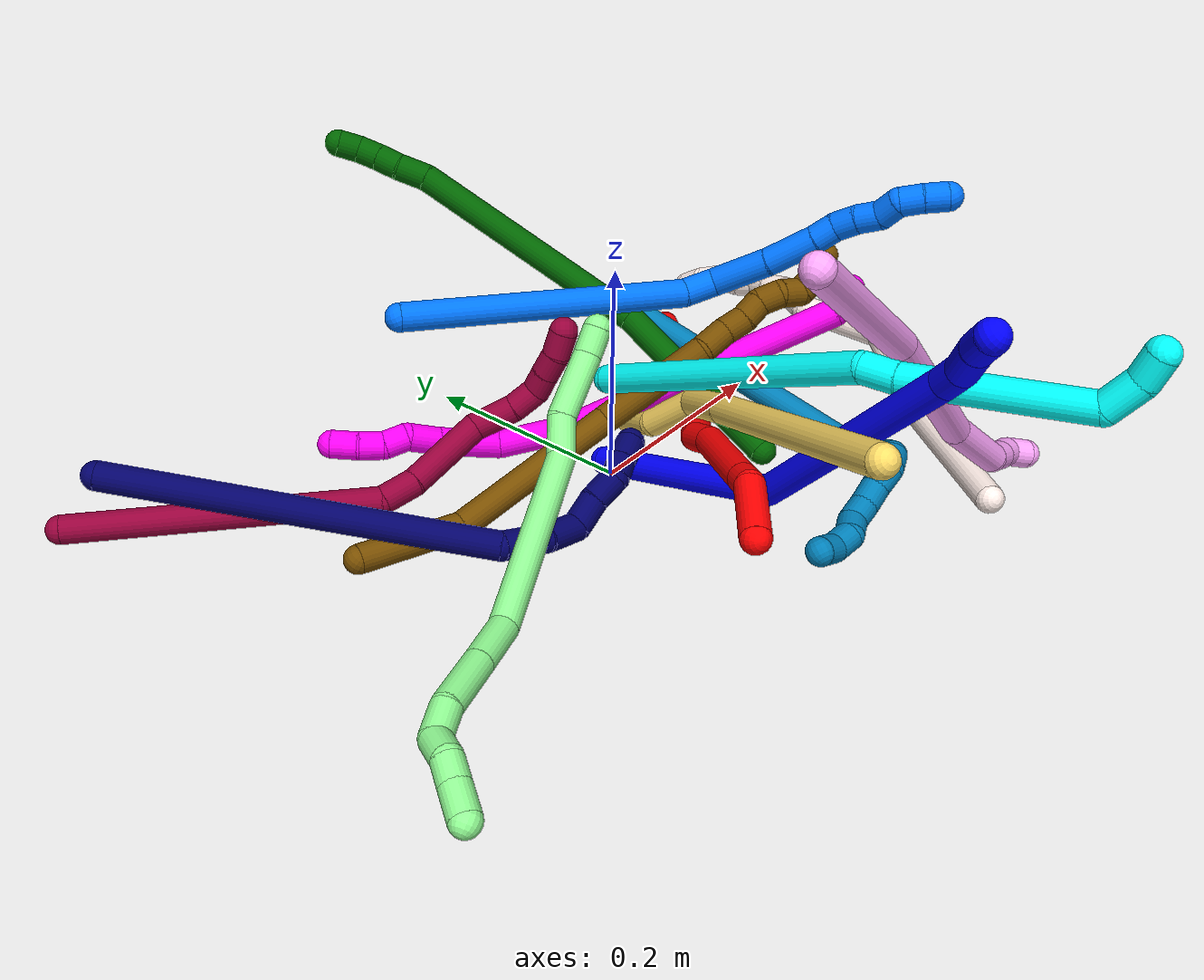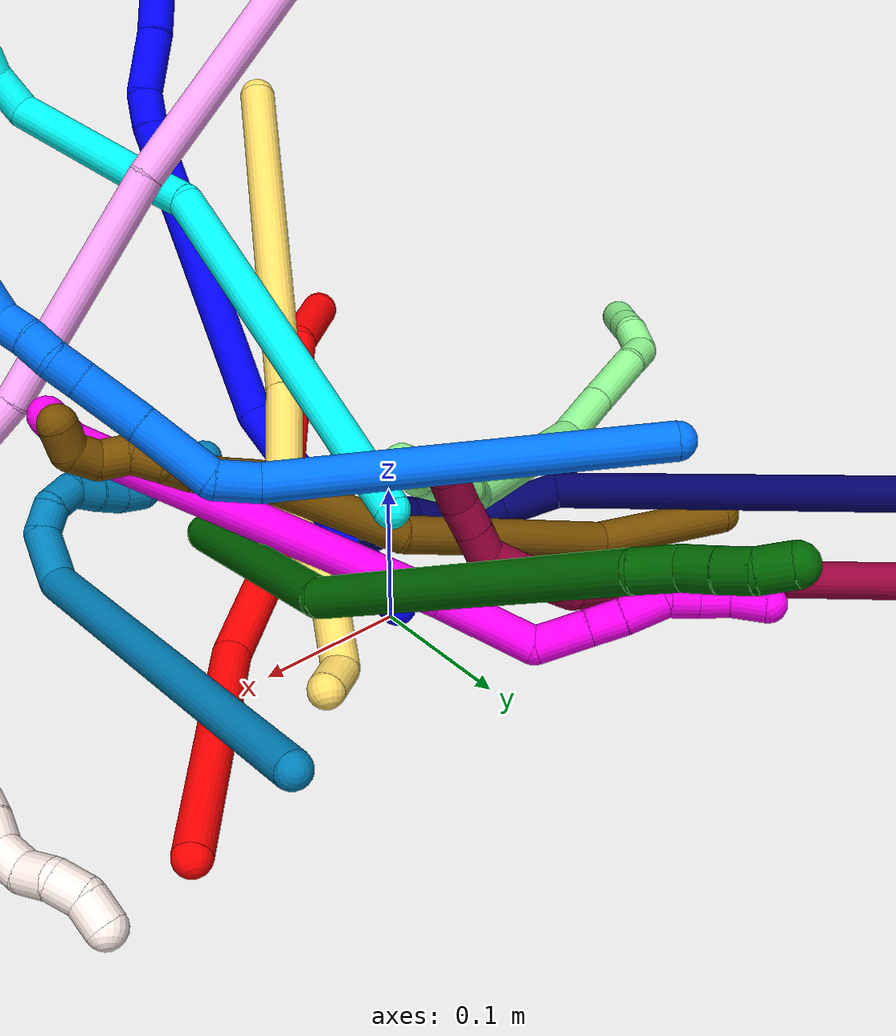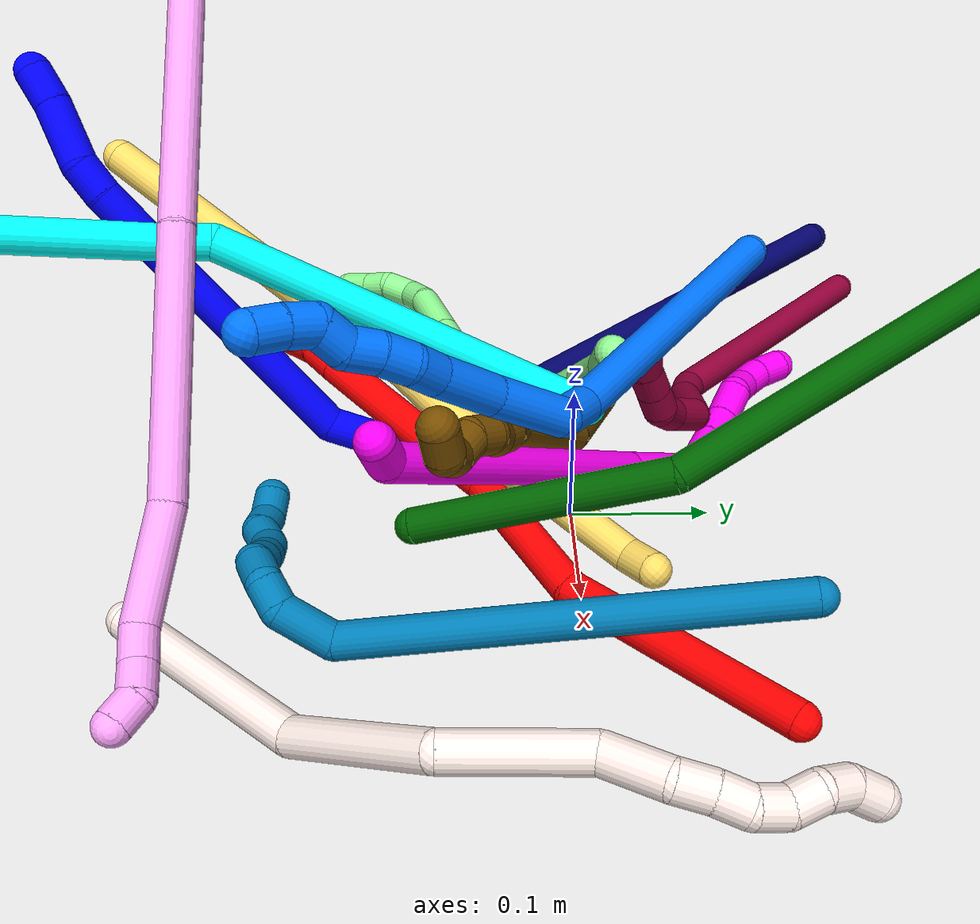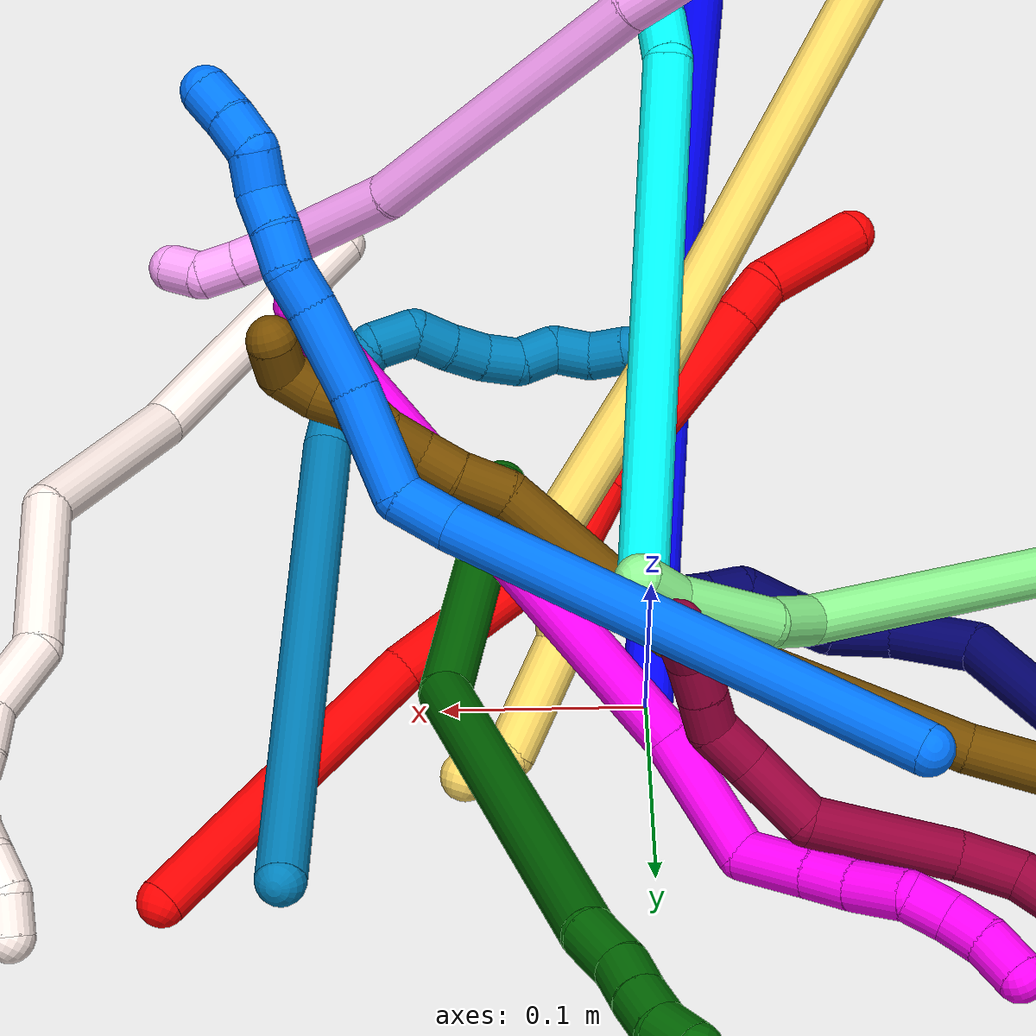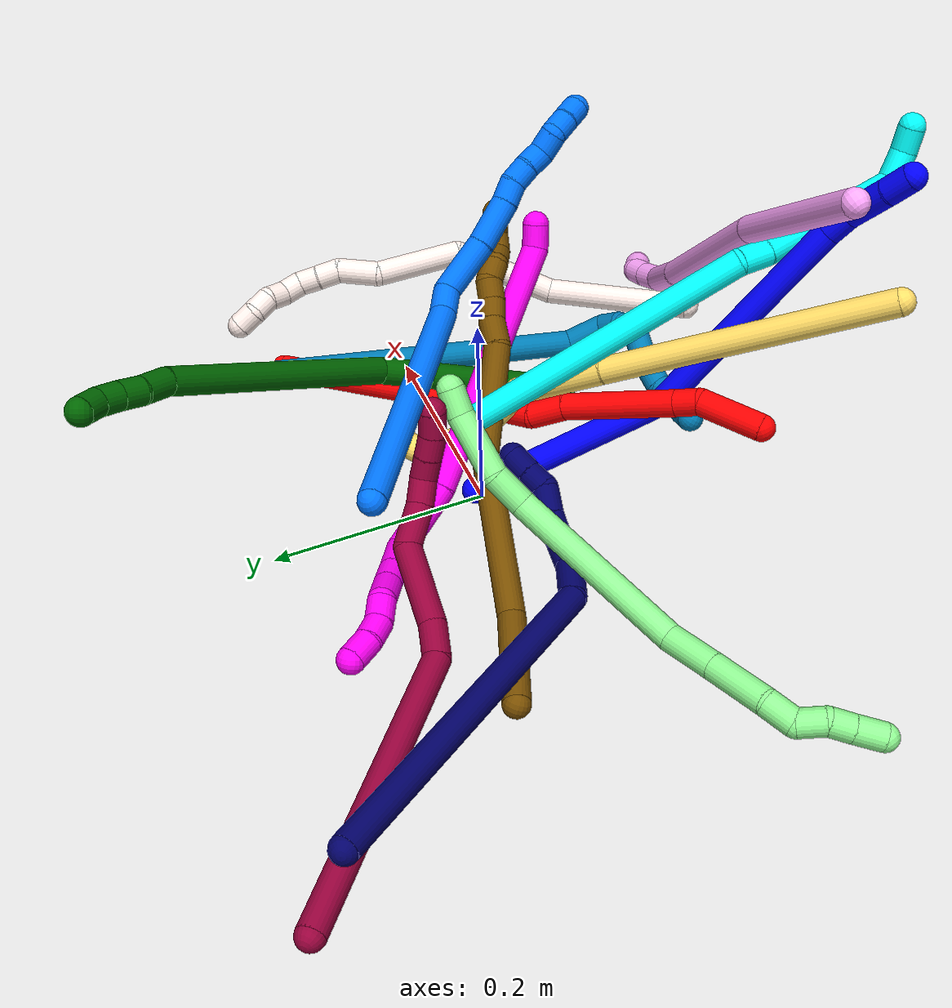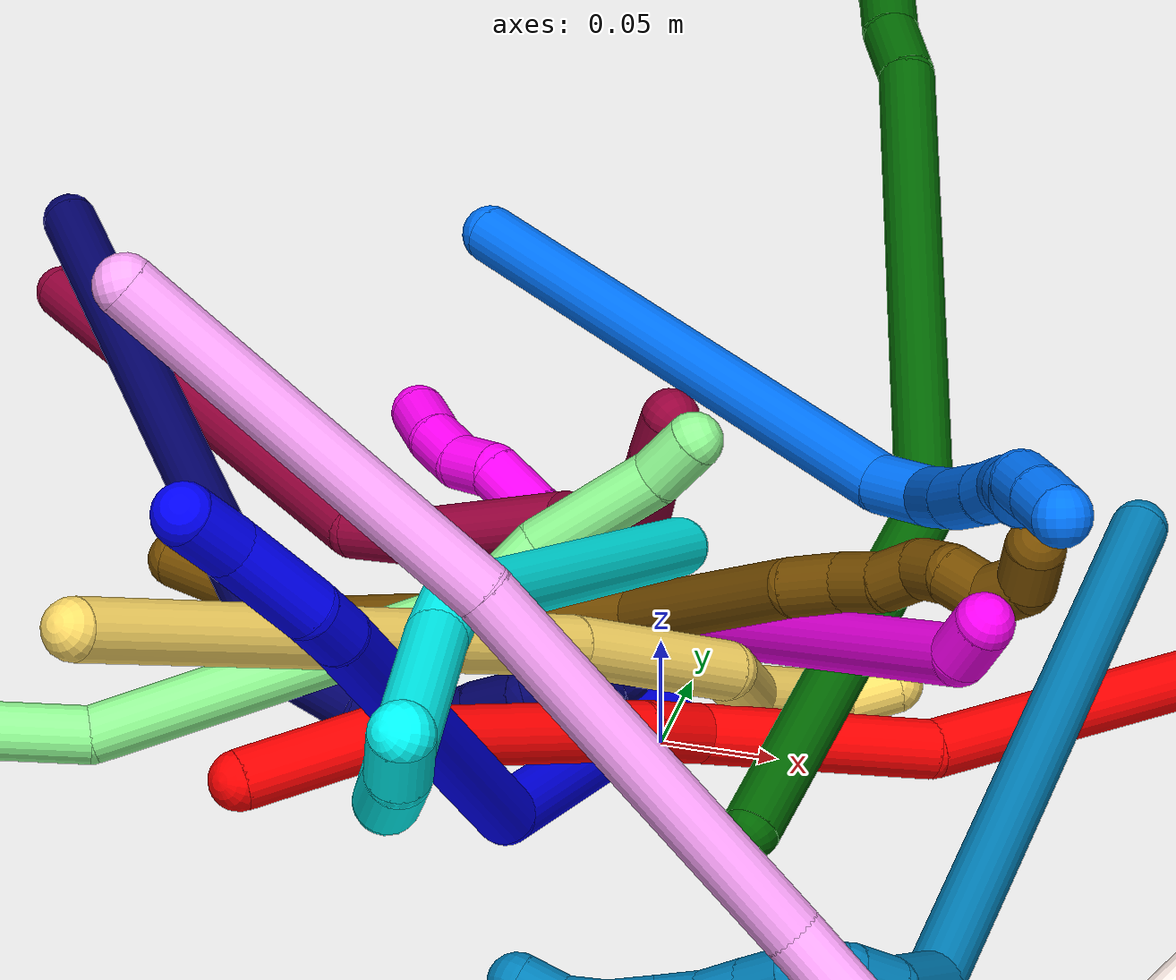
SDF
<sdf version="1.7">
 <world name="default">
  <plugin name="TubeGeneratorPlugin" filename="libtube_generator_plugin.so"/>
  <model name="photoneo_s_sensor">
   <static>1</static>
   <pose>0 0 2 1.57079 1.57079 3.14159</pose>
   <link name="link">
    <inertial><mass>0.1</mass></inertial>
    <sensor name="sensor" type="depth">
     <update_rate>30</update_rate>
     <camera>
      <horizontal_fov>1.22</horizontal_fov>
      <image><width>1920</width><height>1200</height><format>B8G8R8</format></image>
      <clip><near>0.1</near><far>4</far></clip>
      <depth_camera><output>points</output></depth_camera>
     </camera>
     <plugin name="camera_plugin" filename="libgazebo_ros_depth_camera.so">
      <baseline>0.2</baseline>
      <alwaysOn>1</alwaysOn>
      <updateRate>0.0</updateRate>
      <cameraName>camera_ir</cameraName>
      <imageTopicName>/camera/color/image_raw</imageTopicName>
      <cameraInfoTopicName>/camera/color/camera_info</cameraInfoTopicName>
      <depthImageTopicName>/camera/depth/image_raw</depthImageTopicName>
      <depthImageCameraInfoTopicName>/camera/depth/camera_info</depthImageCameraInfoTopicName>
      <pointCloudTopicName>/camera/depth/points</pointCloudTopicName>
      <frameName>fr_optical</frameName>
      <pointCloudCutoff>0.1</pointCloudCutoff>
      <pointCloudCutoffMax>2.0</pointCloudCutoffMax>
      <distortionK1>0</distortionK1>
      <distortionK2>0</distortionK2>
      <distortionK3>0</distortionK3>
      <distortionT1>0</distortionT1>
      <distortionT2>0</distortionT2>
      <CxPrime>0</CxPrime>
      <Cx>0</Cx>
      <Cy>0</Cy>
      <focalLength>0</focalLength>
      <hackBaseline>0</hackBaseline>
     </plugin>
    </sensor>
   </link>
  </model>
  <gravity>0 0 -9.8</gravity>
  <magnetic_field>6e-06 2.3e-05 -4.2e-05</magnetic_field>
  <atmosphere type="adiabatic"/>
  <physics name="default_physics" default="0" type="ode">
   <max_step_size>0.003</max_step_size>
   <real_time_factor>1</real_time_factor>
   <real_time_update_rate>1000</real_time_update_rate>
   <max_contacts>10000</max_contacts>
   <ode>
    <solver>
     <type>quick</type>
     <iters>100</iters>
     <sor>1.3</sor>
     <use_dynamic_moi_rescaling>0</use_dynamic_moi_rescaling>
    </solver>
    <constraints>
     <contact_max_correcting_vel>0</contact_max_correcting_vel>
     <contact_surface_layer>0.001</contact_surface_layer>
     <cfm>0</cfm>
     <erp>0.2</erp>
    </constraints>
   </ode>
  </physics>
  <scene><ambient>0.4 0.4 0.4 1</ambient><background>0.7 0.7 0.7 1</background><shadows>0</shadows></scene>
  <audio><device>default</device></audio>
  <spherical_coordinates>
   <surface_model>EARTH_WGS84</surface_model>
   <latitude_deg>0</latitude_deg>
   <longitude_deg>0</longitude_deg>
   <elevation>0</elevation>
   <heading_deg>0</heading_deg>
  </spherical_coordinates>
  <model name="bin">
   <static>1</static>
   <link name="bottom">
    <collision name="collision-bottom">
     <pose>0 0 -0.01 0 -0 0</pose>
     <geometry><box><size>0.8 0.6 0.02</size></box></geometry>
     <surface>
      <friction><ode><mu>100</mu><mu2>100</mu2></ode></friction>
      <contact><collide_bitmask>65535</collide_bitmask></contact>
     </surface>
    </collision>
   </link>
   <link name="west_wall">
    <collision name="collision-west_wall">
     <pose>-0.41 0 0.1 0 -0 0</pose>
     <geometry><box><size>0.02 0.6 0.2</size></box></geometry>
     <surface>
      <friction><ode><mu>100</mu><mu2>100</mu2></ode></friction>
      <contact><collide_bitmask>65535</collide_bitmask></contact>
     </surface>
    </collision>
   </link>
   <link name="east_wall">
    <collision name="collision-east_wall">
     <pose>0.41 0 0.1 0 -0 0</pose>
     <geometry><box><size>0.02 0.6 0.2</size></box></geometry>
     <surface>
      <friction><ode><mu>100</mu><mu2>100</mu2></ode></friction>
      <contact><collide_bitmask>65535</collide_bitmask></contact>
     </surface>
    </collision>
   </link>
   <link name="south_wall">
    <collision name="collision-south_wall">
     <pose>0 -0.31 0.1 0 -0 0</pose>
     <geometry><box><size>0.8 0.02 0.2</size></box></geometry>
     <surface>
      <friction><ode><mu>100</mu><mu2>100</mu2></ode></friction>
      <contact><collide_bitmask>65535</collide_bitmask></contact>
     </surface>
    </collision>
   </link>
   <link name="north_wall">
    <collision name="collision-north_wall">
     <pose>0 0.31 0.1 0 -0 0</pose>
     <geometry><box><size>0.8 0.02 0.2</size></box></geometry>
     <surface>
      <friction><ode><mu>100</mu><mu2>100</mu2></ode></friction>
      <contact><collide_bitmask>65535</collide_bitmask></contact>
     </surface>
    </collision>
   </link>
  </model>
  <model name="1">
   <static>0</static>
   <link name="1">
    <collision name="collision-cylinder-e_1_1_4">
     <pose>0.006793 -0.052004 0.077959 0.588279 0.072358 0.021928</pose>
     <geometry><cylinder><radius>0.0125</radius><length>0.187915</length></cylinder></geometry>
     <surface>
      <friction><ode><mu>1.16</mu><mu2>1.16</mu2><slip1>0</slip1><slip2>0</slip2></ode></friction>
      <contact><ode><kp>1e+06</kp><kd>1</kd><max_vel>0</max_vel><min_depth>0.001</min_depth></ode></contact>
     </surface>
    </collision>
    <visual name="visual-cylinder-e_1_1_4">
     <pose>0.006793 -0.052004 0.077959 0.588279 0.072358 0.021928</pose>
     <geometry><cylinder><radius>0.0125</radius><length>0.187915</length></cylinder></geometry>
     <material><ambient>0 0 1 1</ambient></material>
    </visual>
    <collision name="collision-cylinder-e_2_4_5">
     <pose>-0.005313 -0.114356 0.262565 0.096741 -0.174581 -0.008473</pose>
     <geometry><cylinder><radius>0.0125</radius><length>0.217604</length></cylinder></geometry>
     <surface>
      <friction><ode><mu>1.16</mu><mu2>1.16</mu2><slip1>0</slip1><slip2>0</slip2></ode></friction>
      <contact><ode><kp>1e+06</kp><kd>1</kd><max_vel>0</max_vel><min_depth>0.001</min_depth></ode></contact>
     </surface>
    </collision>
    <visual name="visual-cylinder-e_2_4_5">
     <pose>-0.005313 -0.114356 0.262565 0.096741 -0.174581 -0.008473</pose>
     <geometry><cylinder><radius>0.0125</radius><length>0.217604</length></cylinder></geometry>
     <material><ambient>0 0 1 1</ambient></material>
    </visual>
    <collision name="collision-cylinder-e_3_5_6">
     <pose>-0.028391 -0.126108 0.380521 0.123359 -0.35153 -0.021935</pose>
     <geometry><cylinder><radius>0.0125</radius><length>0.024276</length></cylinder></geometry>
     <surface>
      <friction><ode><mu>1.16</mu><mu2>1.16</mu2><slip1>0</slip1><slip2>0</slip2></ode></friction>
      <contact><ode><kp>1e+06</kp><kd>1</kd><max_vel>0</max_vel><min_depth>0.001</min_depth></ode></contact>
     </surface>
    </collision>
    <visual name="visual-cylinder-e_3_5_6">
     <pose>-0.028391 -0.126108 0.380521 0.123359 -0.35153 -0.021935</pose>
     <geometry><cylinder><radius>0.0125</radius><length>0.024276</length></cylinder></geometry>
     <material><ambient>0 0 1 1</ambient></material>
    </visual>
    <collision name="collision-cylinder-e_4_6_7">
     <pose>-0.046533 -0.129997 0.408827 0.14528 -0.68249 -0.051674</pose>
     <geometry><cylinder><radius>0.0125</radius><length>0.044274</length></cylinder></geometry>
     <surface>
      <friction><ode><mu>1.16</mu><mu2>1.16</mu2><slip1>0</slip1><slip2>0</slip2></ode></friction>
      <contact><ode><kp>1e+06</kp><kd>1</kd><max_vel>0</max_vel><min_depth>0.001</min_depth></ode></contact>
     </surface>
    </collision>
    <visual name="visual-cylinder-e_4_6_7">
     <pose>-0.046533 -0.129997 0.408827 0.14528 -0.68249 -0.051674</pose>
     <geometry><cylinder><radius>0.0125</radius><length>0.044274</length></cylinder></geometry>
     <material><ambient>0 0 1 1</ambient></material>
    </visual>
    <collision name="collision-cylinder-e_5_7_2">
     <pose>-0.067414 -0.134625 0.436579 0.196512 -0.562894 -0.056984</pose>
     <geometry><cylinder><radius>0.0125</radius><length>0.02593</length></cylinder></geometry>
     <surface>
      <friction><ode><mu>1.16</mu><mu2>1.16</mu2><slip1>0</slip1><slip2>0</slip2></ode></friction>
      <contact><ode><kp>1e+06</kp><kd>1</kd><max_vel>0</max_vel><min_depth>0.001</min_depth></ode></contact>
     </surface>
    </collision>
    <visual name="visual-cylinder-e_5_7_2">
     <pose>-0.067414 -0.134625 0.436579 0.196512 -0.562894 -0.056984</pose>
     <geometry><cylinder><radius>0.0125</radius><length>0.02593</length></cylinder></geometry>
     <material><ambient>0 0 1 1</ambient></material>
    </visual>
    <collision name="collision-sphere-2">
     <pose>-0.074333 -0.136766 0.447332 0 -0 0</pose>
     <geometry><sphere><radius>0.0125</radius></sphere></geometry>
     <surface>
      <friction><ode><mu>1.16</mu><mu2>1.16</mu2><slip1>0</slip1><slip2>0</slip2></ode></friction>
      <contact><ode><kp>1e+06</kp><kd>1</kd><max_vel>0</max_vel><min_depth>0.001</min_depth></ode></contact>
     </surface>
    </collision>
    <visual name="visual-sphere-2">
     <pose>-0.074333 -0.136766 0.447332 0 -0 0</pose>
     <geometry><sphere><radius>0.0125</radius></sphere></geometry>
     <material><ambient>0 0 1 1</ambient></material>
    </visual>
    <collision name="collision-sphere-7">
     <pose>-0.060495 -0.132484 0.425825 0 -0 0</pose>
     <geometry><sphere><radius>0.0125</radius></sphere></geometry>
     <surface>
      <friction><ode><mu>1.16</mu><mu2>1.16</mu2><slip1>0</slip1><slip2>0</slip2></ode></friction>
      <contact><ode><kp>1e+06</kp><kd>1</kd><max_vel>0</max_vel><min_depth>0.001</min_depth></ode></contact>
     </surface>
    </collision>
    <visual name="visual-sphere-7">
     <pose>-0.060495 -0.132484 0.425825 0 -0 0</pose>
     <geometry><sphere><radius>0.0125</radius></sphere></geometry>
     <material><ambient>0 0 1 1</ambient></material>
    </visual>
    <collision name="collision-sphere-6">
     <pose>-0.03257 -0.12751 0.39183 0 -0 0</pose>
     <geometry><sphere><radius>0.0125</radius></sphere></geometry>
     <surface>
      <friction><ode><mu>1.16</mu><mu2>1.16</mu2><slip1>0</slip1><slip2>0</slip2></ode></friction>
      <contact><ode><kp>1e+06</kp><kd>1</kd><max_vel>0</max_vel><min_depth>0.001</min_depth></ode></contact>
     </surface>
    </collision>
    <visual name="visual-sphere-6">
     <pose>-0.03257 -0.12751 0.39183 0 -0 0</pose>
     <geometry><sphere><radius>0.0125</radius></sphere></geometry>
     <material><ambient>0 0 1 1</ambient></material>
    </visual>
    <collision name="collision-sphere-5">
     <pose>-0.024211 -0.124706 0.369212 0 -0 0</pose>
     <geometry><sphere><radius>0.0125</radius></sphere></geometry>
     <surface>
      <friction><ode><mu>1.16</mu><mu2>1.16</mu2><slip1>0</slip1><slip2>0</slip2></ode></friction>
      <contact><ode><kp>1e+06</kp><kd>1</kd><max_vel>0</max_vel><min_depth>0.001</min_depth></ode></contact>
     </surface>
    </collision>
    <visual name="visual-sphere-5">
     <pose>-0.024211 -0.124706 0.369212 0 -0 0</pose>
     <geometry><sphere><radius>0.0125</radius></sphere></geometry>
     <material><ambient>0 0 1 1</ambient></material>
    </visual>
    <collision name="collision-sphere-1">
     <geometry><sphere><radius>0.0125</radius></sphere></geometry>
     <surface>
      <friction><ode><mu>1.16</mu><mu2>1.16</mu2><slip1>0</slip1><slip2>0</slip2></ode></friction>
      <contact><ode><kp>1e+06</kp><kd>1</kd><max_vel>0</max_vel><min_depth>0.001</min_depth></ode></contact>
     </surface>
    </collision>
    <visual name="visual-sphere-1">
     <geometry><sphere><radius>0.0125</radius></sphere></geometry>
     <material><ambient>0 0 1 1</ambient></material>
    </visual>
    <collision name="collision-sphere-4">
     <pose>0.013585 -0.104007 0.155917 0 -0 0</pose>
     <geometry><sphere><radius>0.0125</radius></sphere></geometry>
     <surface>
      <friction><ode><mu>1.16</mu><mu2>1.16</mu2><slip1>0</slip1><slip2>0</slip2></ode></friction>
      <contact><ode><kp>1e+06</kp><kd>1</kd><max_vel>0</max_vel><min_depth>0.001</min_depth></ode></contact>
     </surface>
    </collision>
    <visual name="visual-sphere-4">
     <pose>0.013585 -0.104007 0.155917 0 -0 0</pose>
     <geometry><sphere><radius>0.0125</radius></sphere></geometry>
     <material><ambient>0 0 1 1</ambient></material>
    </visual>
    <inertial>
     <pose>-0.008754 -0.093929 0.220887 0 -0 0</pose>
     <mass>0.5</mass>
     <inertia>
      <ixx>0.001422</ixx>
      <ixy>0</ixy>
      <ixz>0</ixz>
      <iyy>0.001337</iyy>
      <iyz>0</iyz>
      <izz>0.000547</izz>
     </inertia>
    </inertial>
   </link>
   <pose>-0.000317 0.006662 0.011498 0.622474 0.361313 -0.297361</pose>
  </model>
  <model name="2">
   <static>0</static>
   <link name="2">
    <collision name="collision-cylinder-e_1_1_4">
     <pose>-0.020688 -0.032253 0.075958 0.40155 -0.245634 -0.050233</pose>
     <geometry><cylinder><radius>0.0125</radius><length>0.170152</length></cylinder></geometry>
     <surface>
      <friction><ode><mu>1.16</mu><mu2>1.16</mu2><slip1>0</slip1><slip2>0</slip2></ode></friction>
      <contact><ode><kp>1e+06</kp><kd>1</kd><max_vel>0</max_vel><min_depth>0.001</min_depth></ode></contact>
     </surface>
    </collision>
    <visual name="visual-cylinder-e_1_1_4">
     <pose>-0.020688 -0.032253 0.075958 0.40155 -0.245634 -0.050233</pose>
     <geometry><cylinder><radius>0.0125</radius><length>0.170152</length></cylinder></geometry>
     <material><ambient>1 0 0 1</ambient></material>
    </visual>
    <collision name="collision-cylinder-e_2_4_5">
     <pose>-0.067906 -0.075131 0.196372 0.234591 -0.525896 -0.063417</pose>
     <geometry><cylinder><radius>0.0125</radius><length>0.105698</length></cylinder></geometry>
     <surface>
      <friction><ode><mu>1.16</mu><mu2>1.16</mu2><slip1>0</slip1><slip2>0</slip2></ode></friction>
      <contact><ode><kp>1e+06</kp><kd>1</kd><max_vel>0</max_vel><min_depth>0.001</min_depth></ode></contact>
     </surface>
    </collision>
    <visual name="visual-cylinder-e_2_4_5">
     <pose>-0.067906 -0.075131 0.196372 0.234591 -0.525896 -0.063417</pose>
     <geometry><cylinder><radius>0.0125</radius><length>0.105698</length></cylinder></geometry>
     <material><ambient>1 0 0 1</ambient></material>
    </visual>
    <collision name="collision-cylinder-e_3_5_6">
     <pose>-0.096726 -0.085565 0.257675 -0.011339 -0.135116 0.000767</pose>
     <geometry><cylinder><radius>0.0125</radius><length>0.034007</length></cylinder></geometry>
     <surface>
      <friction><ode><mu>1.16</mu><mu2>1.16</mu2><slip1>0</slip1><slip2>0</slip2></ode></friction>
      <contact><ode><kp>1e+06</kp><kd>1</kd><max_vel>0</max_vel><min_depth>0.001</min_depth></ode></contact>
     </surface>
    </collision>
    <visual name="visual-cylinder-e_3_5_6">
     <pose>-0.096726 -0.085565 0.257675 -0.011339 -0.135116 0.000767</pose>
     <geometry><cylinder><radius>0.0125</radius><length>0.034007</length></cylinder></geometry>
     <material><ambient>1 0 0 1</ambient></material>
    </visual>
    <collision name="collision-cylinder-e_4_6_7">
     <pose>-0.113373 -0.093115 0.326177 0.148765 -0.268245 -0.02011</pose>
     <geometry><cylinder><radius>0.0125</radius><length>0.108336</length></cylinder></geometry>
     <surface>
      <friction><ode><mu>1.16</mu><mu2>1.16</mu2><slip1>0</slip1><slip2>0</slip2></ode></friction>
      <contact><ode><kp>1e+06</kp><kd>1</kd><max_vel>0</max_vel><min_depth>0.001</min_depth></ode></contact>
     </surface>
    </collision>
    <visual name="visual-cylinder-e_4_6_7">
     <pose>-0.113373 -0.093115 0.326177 0.148765 -0.268245 -0.02011</pose>
     <geometry><cylinder><radius>0.0125</radius><length>0.108336</length></cylinder></geometry>
     <material><ambient>1 0 0 1</ambient></material>
    </visual>
    <collision name="collision-cylinder-e_5_7_8">
     <pose>-0.130945 -0.101973 0.388449 0.104773 -0.292519 -0.015448</pose>
     <geometry><cylinder><radius>0.0125</radius><length>0.0223</length></cylinder></geometry>
     <surface>
      <friction><ode><mu>1.16</mu><mu2>1.16</mu2><slip1>0</slip1><slip2>0</slip2></ode></friction>
      <contact><ode><kp>1e+06</kp><kd>1</kd><max_vel>0</max_vel><min_depth>0.001</min_depth></ode></contact>
     </surface>
    </collision>
    <visual name="visual-cylinder-e_5_7_8">
     <pose>-0.130945 -0.101973 0.388449 0.104773 -0.292519 -0.015448</pose>
     <geometry><cylinder><radius>0.0125</radius><length>0.0223</length></cylinder></geometry>
     <material><ambient>1 0 0 1</ambient></material>
    </visual>
    <collision name="collision-cylinder-e_6_8_2">
     <pose>-0.144453 -0.119003 0.422003 0.60654 -0.353247 -0.111587</pose>
     <geometry><cylinder><radius>0.0125</radius><length>0.059507</length></cylinder></geometry>
     <surface>
      <friction><ode><mu>1.16</mu><mu2>1.16</mu2><slip1>0</slip1><slip2>0</slip2></ode></friction>
      <contact><ode><kp>1e+06</kp><kd>1</kd><max_vel>0</max_vel><min_depth>0.001</min_depth></ode></contact>
     </surface>
    </collision>
    <visual name="visual-cylinder-e_6_8_2">
     <pose>-0.144453 -0.119003 0.422003 0.60654 -0.353247 -0.111587</pose>
     <geometry><cylinder><radius>0.0125</radius><length>0.059507</length></cylinder></geometry>
     <material><ambient>1 0 0 1</ambient></material>
    </visual>
    <collision name="collision-sphere-2">
     <pose>-0.154746 -0.134916 0.44494 0 -0 0</pose>
     <geometry><sphere><radius>0.0125</radius></sphere></geometry>
     <surface>
      <friction><ode><mu>1.16</mu><mu2>1.16</mu2><slip1>0</slip1><slip2>0</slip2></ode></friction>
      <contact><ode><kp>1e+06</kp><kd>1</kd><max_vel>0</max_vel><min_depth>0.001</min_depth></ode></contact>
     </surface>
    </collision>
    <visual name="visual-sphere-2">
     <pose>-0.154746 -0.134916 0.44494 0 -0 0</pose>
     <geometry><sphere><radius>0.0125</radius></sphere></geometry>
     <material><ambient>1 0 0 1</ambient></material>
    </visual>
    <collision name="collision-sphere-4">
     <pose>-0.041376 -0.064507 0.151916 0 -0 0</pose>
     <geometry><sphere><radius>0.0125</radius></sphere></geometry>
     <surface>
      <friction><ode><mu>1.16</mu><mu2>1.16</mu2><slip1>0</slip1><slip2>0</slip2></ode></friction>
      <contact><ode><kp>1e+06</kp><kd>1</kd><max_vel>0</max_vel><min_depth>0.001</min_depth></ode></contact>
     </surface>
    </collision>
    <visual name="visual-sphere-4">
     <pose>-0.041376 -0.064507 0.151916 0 -0 0</pose>
     <geometry><sphere><radius>0.0125</radius></sphere></geometry>
     <material><ambient>1 0 0 1</ambient></material>
    </visual>
    <collision name="collision-sphere-1">
     <geometry><sphere><radius>0.0125</radius></sphere></geometry>
     <surface>
      <friction><ode><mu>1.16</mu><mu2>1.16</mu2><slip1>0</slip1><slip2>0</slip2></ode></friction>
      <contact><ode><kp>1e+06</kp><kd>1</kd><max_vel>0</max_vel><min_depth>0.001</min_depth></ode></contact>
     </surface>
    </collision>
    <visual name="visual-sphere-1">
     <geometry><sphere><radius>0.0125</radius></sphere></geometry>
     <material><ambient>1 0 0 1</ambient></material>
    </visual>
    <collision name="collision-sphere-8">
     <pose>-0.13416 -0.10309 0.399066 0 -0 0</pose>
     <geometry><sphere><radius>0.0125</radius></sphere></geometry>
     <surface>
      <friction><ode><mu>1.16</mu><mu2>1.16</mu2><slip1>0</slip1><slip2>0</slip2></ode></friction>
      <contact><ode><kp>1e+06</kp><kd>1</kd><max_vel>0</max_vel><min_depth>0.001</min_depth></ode></contact>
     </surface>
    </collision>
    <visual name="visual-sphere-8">
     <pose>-0.13416 -0.10309 0.399066 0 -0 0</pose>
     <geometry><sphere><radius>0.0125</radius></sphere></geometry>
     <material><ambient>1 0 0 1</ambient></material>
    </visual>
    <collision name="collision-sphere-5">
     <pose>-0.094435 -0.085756 0.240828 0 -0 0</pose>
     <geometry><sphere><radius>0.0125</radius></sphere></geometry>
     <surface>
      <friction><ode><mu>1.16</mu><mu2>1.16</mu2><slip1>0</slip1><slip2>0</slip2></ode></friction>
      <contact><ode><kp>1e+06</kp><kd>1</kd><max_vel>0</max_vel><min_depth>0.001</min_depth></ode></contact>
     </surface>
    </collision>
    <visual name="visual-sphere-5">
     <pose>-0.094435 -0.085756 0.240828 0 -0 0</pose>
     <geometry><sphere><radius>0.0125</radius></sphere></geometry>
     <material><ambient>1 0 0 1</ambient></material>
    </visual>
    <collision name="collision-sphere-6">
     <pose>-0.099016 -0.085374 0.274523 0 -0 0</pose>
     <geometry><sphere><radius>0.0125</radius></sphere></geometry>
     <surface>
      <friction><ode><mu>1.16</mu><mu2>1.16</mu2><slip1>0</slip1><slip2>0</slip2></ode></friction>
      <contact><ode><kp>1e+06</kp><kd>1</kd><max_vel>0</max_vel><min_depth>0.001</min_depth></ode></contact>
     </surface>
    </collision>
    <visual name="visual-sphere-6">
     <pose>-0.099016 -0.085374 0.274523 0 -0 0</pose>
     <geometry><sphere><radius>0.0125</radius></sphere></geometry>
     <material><ambient>1 0 0 1</ambient></material>
    </visual>
    <collision name="collision-sphere-7">
     <pose>-0.12773 -0.100857 0.377831 0 -0 0</pose>
     <geometry><sphere><radius>0.0125</radius></sphere></geometry>
     <surface>
      <friction><ode><mu>1.16</mu><mu2>1.16</mu2><slip1>0</slip1><slip2>0</slip2></ode></friction>
      <contact><ode><kp>1e+06</kp><kd>1</kd><max_vel>0</max_vel><min_depth>0.001</min_depth></ode></contact>
     </surface>
    </collision>
    <visual name="visual-sphere-7">
     <pose>-0.12773 -0.100857 0.377831 0 -0 0</pose>
     <geometry><sphere><radius>0.0125</radius></sphere></geometry>
     <material><ambient>1 0 0 1</ambient></material>
    </visual>
    <inertial>
     <pose>-0.075571 -0.071565 0.223109 0 -0 0</pose>
     <mass>0.5</mass>
     <inertia>
      <ixx>0.000581</ixx>
      <ixy>0</ixy>
      <ixz>0</ixz>
      <iyy>0.000577</iyy>
      <iyz>0</iyz>
      <izz>0.00043</izz>
     </inertia>
    </inertial>
   </link>
   <pose>0.234558 0.114986 0.011495 1.15539 0.212922 -0.507524</pose>
  </model>
  <model name="3">
   <static>0</static>
   <link name="3">
    <collision name="collision-cylinder-e_1_1_4">
     <pose>0.026061 0.042974 0.128202 -0.323432 0.190405 -0.031154</pose>
     <geometry><cylinder><radius>0.0125</radius><length>0.275403</length></cylinder></geometry>
     <surface>
      <friction><ode><mu>1.16</mu><mu2>1.16</mu2><slip1>0</slip1><slip2>0</slip2></ode></friction>
      <contact><ode><kp>1e+06</kp><kd>1</kd><max_vel>0</max_vel><min_depth>0.001</min_depth></ode></contact>
     </surface>
    </collision>
    <visual name="visual-cylinder-e_1_1_4">
     <pose>0.026061 0.042974 0.128202 -0.323432 0.190405 -0.031154</pose>
     <geometry><cylinder><radius>0.0125</radius><length>0.275403</length></cylinder></geometry>
     <material><ambient>0.003922 1 0.996078 1</ambient></material>
    </visual>
    <collision name="collision-cylinder-e_2_4_5">
     <pose>0.060298 0.091113 0.266778 -0.461949 0.614437 -0.148947</pose>
     <geometry><cylinder><radius>0.0125</radius><length>0.028366</length></cylinder></geometry>
     <surface>
      <friction><ode><mu>1.16</mu><mu2>1.16</mu2><slip1>0</slip1><slip2>0</slip2></ode></friction>
      <contact><ode><kp>1e+06</kp><kd>1</kd><max_vel>0</max_vel><min_depth>0.001</min_depth></ode></contact>
     </surface>
    </collision>
    <visual name="visual-cylinder-e_2_4_5">
     <pose>0.060298 0.091113 0.266778 -0.461949 0.614437 -0.148947</pose>
     <geometry><cylinder><radius>0.0125</radius><length>0.028366</length></cylinder></geometry>
     <material><ambient>0.003922 1 0.996078 1</ambient></material>
    </visual>
    <collision name="collision-cylinder-e_3_5_6">
     <pose>0.1027 0.130136 0.329233 -0.576461 0.503576 -0.152246</pose>
     <geometry><cylinder><radius>0.0125</radius><length>0.141847</length></cylinder></geometry>
     <surface>
      <friction><ode><mu>1.16</mu><mu2>1.16</mu2><slip1>0</slip1><slip2>0</slip2></ode></friction>
      <contact><ode><kp>1e+06</kp><kd>1</kd><max_vel>0</max_vel><min_depth>0.001</min_depth></ode></contact>
     </surface>
    </collision>
    <visual name="visual-cylinder-e_3_5_6">
     <pose>0.1027 0.130136 0.329233 -0.576461 0.503576 -0.152246</pose>
     <geometry><cylinder><radius>0.0125</radius><length>0.141847</length></cylinder></geometry>
     <material><ambient>0.003922 1 0.996078 1</ambient></material>
    </visual>
    <collision name="collision-cylinder-e_4_6_7">
     <pose>0.133023 0.174613 0.391987 -0.782764 -0.253568 0.105108</pose>
     <geometry><cylinder><radius>0.0125</radius><length>0.031105</length></cylinder></geometry>
     <surface>
      <friction><ode><mu>1.16</mu><mu2>1.16</mu2><slip1>0</slip1><slip2>0</slip2></ode></friction>
      <contact><ode><kp>1e+06</kp><kd>1</kd><max_vel>0</max_vel><min_depth>0.001</min_depth></ode></contact>
     </surface>
    </collision>
    <visual name="visual-cylinder-e_4_6_7">
     <pose>0.133023 0.174613 0.391987 -0.782764 -0.253568 0.105108</pose>
     <geometry><cylinder><radius>0.0125</radius><length>0.031105</length></cylinder></geometry>
     <material><ambient>0.003922 1 0.996078 1</ambient></material>
    </visual>
    <collision name="collision-cylinder-e_5_7_2">
     <pose>0.122534 0.191143 0.410219 -0.663917 -0.601619 0.213067</pose>
     <geometry><cylinder><radius>0.0125</radius><length>0.023279</length></cylinder></geometry>
     <surface>
      <friction><ode><mu>1.16</mu><mu2>1.16</mu2><slip1>0</slip1><slip2>0</slip2></ode></friction>
      <contact><ode><kp>1e+06</kp><kd>1</kd><max_vel>0</max_vel><min_depth>0.001</min_depth></ode></contact>
     </surface>
    </collision>
    <visual name="visual-cylinder-e_5_7_2">
     <pose>0.122534 0.191143 0.410219 -0.663917 -0.601619 0.213067</pose>
     <geometry><cylinder><radius>0.0125</radius><length>0.023279</length></cylinder></geometry>
     <material><ambient>0.003922 1 0.996078 1</ambient></material>
    </visual>
    <collision name="collision-sphere-2">
     <pose>0.115946 0.197056 0.417776 0 -0 0</pose>
     <geometry><sphere><radius>0.0125</radius></sphere></geometry>
     <surface>
      <friction><ode><mu>1.16</mu><mu2>1.16</mu2><slip1>0</slip1><slip2>0</slip2></ode></friction>
      <contact><ode><kp>1e+06</kp><kd>1</kd><max_vel>0</max_vel><min_depth>0.001</min_depth></ode></contact>
     </surface>
    </collision>
    <visual name="visual-sphere-2">
     <pose>0.115946 0.197056 0.417776 0 -0 0</pose>
     <geometry><sphere><radius>0.0125</radius></sphere></geometry>
     <material><ambient>0.003922 1 0.996078 1</ambient></material>
    </visual>
    <collision name="collision-sphere-7">
     <pose>0.129121 0.18523 0.402661 0 -0 0</pose>
     <geometry><sphere><radius>0.0125</radius></sphere></geometry>
     <surface>
      <friction><ode><mu>1.16</mu><mu2>1.16</mu2><slip1>0</slip1><slip2>0</slip2></ode></friction>
      <contact><ode><kp>1e+06</kp><kd>1</kd><max_vel>0</max_vel><min_depth>0.001</min_depth></ode></contact>
     </surface>
    </collision>
    <visual name="visual-sphere-7">
     <pose>0.129121 0.18523 0.402661 0 -0 0</pose>
     <geometry><sphere><radius>0.0125</radius></sphere></geometry>
     <material><ambient>0.003922 1 0.996078 1</ambient></material>
    </visual>
    <collision name="collision-sphere-6">
     <pose>0.136925 0.163995 0.381314 0 -0 0</pose>
     <geometry><sphere><radius>0.0125</radius></sphere></geometry>
     <surface>
      <friction><ode><mu>1.16</mu><mu2>1.16</mu2><slip1>0</slip1><slip2>0</slip2></ode></friction>
      <contact><ode><kp>1e+06</kp><kd>1</kd><max_vel>0</max_vel><min_depth>0.001</min_depth></ode></contact>
     </surface>
    </collision>
    <visual name="visual-sphere-6">
     <pose>0.136925 0.163995 0.381314 0 -0 0</pose>
     <geometry><sphere><radius>0.0125</radius></sphere></geometry>
     <material><ambient>0.003922 1 0.996078 1</ambient></material>
    </visual>
    <collision name="collision-sphere-5">
     <pose>0.068475 0.096278 0.277153 0 -0 0</pose>
     <geometry><sphere><radius>0.0125</radius></sphere></geometry>
     <surface>
      <friction><ode><mu>1.16</mu><mu2>1.16</mu2><slip1>0</slip1><slip2>0</slip2></ode></friction>
      <contact><ode><kp>1e+06</kp><kd>1</kd><max_vel>0</max_vel><min_depth>0.001</min_depth></ode></contact>
     </surface>
    </collision>
    <visual name="visual-sphere-5">
     <pose>0.068475 0.096278 0.277153 0 -0 0</pose>
     <geometry><sphere><radius>0.0125</radius></sphere></geometry>
     <material><ambient>0.003922 1 0.996078 1</ambient></material>
    </visual>
    <collision name="collision-sphere-1">
     <geometry><sphere><radius>0.0125</radius></sphere></geometry>
     <surface>
      <friction><ode><mu>1.16</mu><mu2>1.16</mu2><slip1>0</slip1><slip2>0</slip2></ode></friction>
      <contact><ode><kp>1e+06</kp><kd>1</kd><max_vel>0</max_vel><min_depth>0.001</min_depth></ode></contact>
     </surface>
    </collision>
    <visual name="visual-sphere-1">
     <geometry><sphere><radius>0.0125</radius></sphere></geometry>
     <material><ambient>0.003922 1 0.996078 1</ambient></material>
    </visual>
    <collision name="collision-sphere-4">
     <pose>0.052122 0.085947 0.256404 0 -0 0</pose>
     <geometry><sphere><radius>0.0125</radius></sphere></geometry>
     <surface>
      <friction><ode><mu>1.16</mu><mu2>1.16</mu2><slip1>0</slip1><slip2>0</slip2></ode></friction>
      <contact><ode><kp>1e+06</kp><kd>1</kd><max_vel>0</max_vel><min_depth>0.001</min_depth></ode></contact>
     </surface>
    </collision>
    <visual name="visual-sphere-4">
     <pose>0.052122 0.085947 0.256404 0 -0 0</pose>
     <geometry><sphere><radius>0.0125</radius></sphere></geometry>
     <material><ambient>0.003922 1 0.996078 1</ambient></material>
    </visual>
    <inertial>
     <pose>0.060891 0.08552 0.222635 0 -0 0</pose>
     <mass>0.5</mass>
     <inertia>
      <ixx>0.001861</ixx>
      <ixy>0</ixy>
      <ixz>0</ixz>
      <iyy>0.001811</iyy>
      <iyz>0</iyz>
      <izz>-0.001083</izz>
     </inertia>
    </inertial>
   </link>
   <pose>0.005 0.009006 0.092036 0.509426 0.93547 -1.45562</pose>
  </model>
  <model name="4">
   <static>0</static>
   <link name="4">
    <collision name="collision-cylinder-e_1_1_4">
     <pose>0.016926 -0.075879 0.042289 1.06235 0.192434 0.113282</pose>
     <geometry><cylinder><radius>0.0125</radius><length>0.177002</length></cylinder></geometry>
     <surface>
      <friction><ode><mu>1.16</mu><mu2>1.16</mu2><slip1>0</slip1><slip2>0</slip2></ode></friction>
      <contact><ode><kp>1e+06</kp><kd>1</kd><max_vel>0</max_vel><min_depth>0.001</min_depth></ode></contact>
     </surface>
    </collision>
    <visual name="visual-cylinder-e_1_1_4">
     <pose>0.016926 -0.075879 0.042289 1.06235 0.192434 0.113282</pose>
     <geometry><cylinder><radius>0.0125</radius><length>0.177002</length></cylinder></geometry>
     <material><ambient>1 0.65098 0.996078 1</ambient></material>
    </visual>
    <collision name="collision-cylinder-e_2_4_5">
     <pose>0.052027 -0.233662 0.116388 1.20035 0.203978 0.139859</pose>
     <geometry><cylinder><radius>0.0125</radius><length>0.179449</length></cylinder></geometry>
     <surface>
      <friction><ode><mu>1.16</mu><mu2>1.16</mu2><slip1>0</slip1><slip2>0</slip2></ode></friction>
      <contact><ode><kp>1e+06</kp><kd>1</kd><max_vel>0</max_vel><min_depth>0.001</min_depth></ode></contact>
     </surface>
    </collision>
    <visual name="visual-cylinder-e_2_4_5">
     <pose>0.052027 -0.233662 0.116388 1.20035 0.203978 0.139859</pose>
     <geometry><cylinder><radius>0.0125</radius><length>0.179449</length></cylinder></geometry>
     <material><ambient>1 0.65098 0.996078 1</ambient></material>
    </visual>
    <collision name="collision-cylinder-e_3_5_6">
     <pose>0.071057 -0.350828 0.164104 1.14706 0.022101 0.014276</pose>
     <geometry><cylinder><radius>0.0125</radius><length>0.077385</length></cylinder></geometry>
     <surface>
      <friction><ode><mu>1.16</mu><mu2>1.16</mu2><slip1>0</slip1><slip2>0</slip2></ode></friction>
      <contact><ode><kp>1e+06</kp><kd>1</kd><max_vel>0</max_vel><min_depth>0.001</min_depth></ode></contact>
     </surface>
    </collision>
    <visual name="visual-cylinder-e_3_5_6">
     <pose>0.071057 -0.350828 0.164104 1.14706 0.022101 0.014276</pose>
     <geometry><cylinder><radius>0.0125</radius><length>0.077385</length></cylinder></geometry>
     <material><ambient>1 0.65098 0.996078 1</ambient></material>
    </visual>
    <collision name="collision-cylinder-e_4_6_7">
     <pose>0.074253 -0.394537 0.188771 0.767175 0.190027 0.076885</pose>
     <geometry><cylinder><radius>0.0125</radius><length>0.024788</length></cylinder></geometry>
     <surface>
      <friction><ode><mu>1.16</mu><mu2>1.16</mu2><slip1>0</slip1><slip2>0</slip2></ode></friction>
      <contact><ode><kp>1e+06</kp><kd>1</kd><max_vel>0</max_vel><min_depth>0.001</min_depth></ode></contact>
     </surface>
    </collision>
    <visual name="visual-cylinder-e_4_6_7">
     <pose>0.074253 -0.394537 0.188771 0.767175 0.190027 0.076885</pose>
     <geometry><cylinder><radius>0.0125</radius><length>0.024788</length></cylinder></geometry>
     <material><ambient>1 0.65098 0.996078 1</ambient></material>
    </visual>
    <collision name="collision-cylinder-e_5_7_8">
     <pose>0.07831 -0.409656 0.205454 0.699842 0.164203 0.060041</pose>
     <geometry><cylinder><radius>0.0125</radius><length>0.020996</length></cylinder></geometry>
     <surface>
      <friction><ode><mu>1.16</mu><mu2>1.16</mu2><slip1>0</slip1><slip2>0</slip2></ode></friction>
      <contact><ode><kp>1e+06</kp><kd>1</kd><max_vel>0</max_vel><min_depth>0.001</min_depth></ode></contact>
     </surface>
    </collision>
    <visual name="visual-cylinder-e_5_7_8">
     <pose>0.07831 -0.409656 0.205454 0.699842 0.164203 0.060041</pose>
     <geometry><cylinder><radius>0.0125</radius><length>0.020996</length></cylinder></geometry>
     <material><ambient>1 0.65098 0.996078 1</ambient></material>
    </visual>
    <collision name="collision-cylinder-e_6_8_2">
     <pose>0.075491 -0.423548 0.218954 0.913162 -0.461252 -0.229656</pose>
     <geometry><cylinder><radius>0.0125</radius><length>0.02038</length></cylinder></geometry>
     <surface>
      <friction><ode><mu>1.16</mu><mu2>1.16</mu2><slip1>0</slip1><slip2>0</slip2></ode></friction>
      <contact><ode><kp>1e+06</kp><kd>1</kd><max_vel>0</max_vel><min_depth>0.001</min_depth></ode></contact>
     </surface>
    </collision>
    <visual name="visual-cylinder-e_6_8_2">
     <pose>0.075491 -0.423548 0.218954 0.913162 -0.461252 -0.229656</pose>
     <geometry><cylinder><radius>0.0125</radius><length>0.02038</length></cylinder></geometry>
     <material><ambient>1 0.65098 0.996078 1</ambient></material>
    </visual>
    <collision name="collision-sphere-2">
     <pose>0.070955 -0.430771 0.224532 0 -0 0</pose>
     <geometry><sphere><radius>0.0125</radius></sphere></geometry>
     <surface>
      <friction><ode><mu>1.16</mu><mu2>1.16</mu2><slip1>0</slip1><slip2>0</slip2></ode></friction>
      <contact><ode><kp>1e+06</kp><kd>1</kd><max_vel>0</max_vel><min_depth>0.001</min_depth></ode></contact>
     </surface>
    </collision>
    <visual name="visual-sphere-2">
     <pose>0.070955 -0.430771 0.224532 0 -0 0</pose>
     <geometry><sphere><radius>0.0125</radius></sphere></geometry>
     <material><ambient>1 0.65098 0.996078 1</ambient></material>
    </visual>
    <collision name="collision-sphere-4">
     <pose>0.033851 -0.151757 0.084578 0 -0 0</pose>
     <geometry><sphere><radius>0.0125</radius></sphere></geometry>
     <surface>
      <friction><ode><mu>1.16</mu><mu2>1.16</mu2><slip1>0</slip1><slip2>0</slip2></ode></friction>
      <contact><ode><kp>1e+06</kp><kd>1</kd><max_vel>0</max_vel><min_depth>0.001</min_depth></ode></contact>
     </surface>
    </collision>
    <visual name="visual-sphere-4">
     <pose>0.033851 -0.151757 0.084578 0 -0 0</pose>
     <geometry><sphere><radius>0.0125</radius></sphere></geometry>
     <material><ambient>1 0.65098 0.996078 1</ambient></material>
    </visual>
    <collision name="collision-sphere-1">
     <geometry><sphere><radius>0.0125</radius></sphere></geometry>
     <surface>
      <friction><ode><mu>1.16</mu><mu2>1.16</mu2><slip1>0</slip1><slip2>0</slip2></ode></friction>
      <contact><ode><kp>1e+06</kp><kd>1</kd><max_vel>0</max_vel><min_depth>0.001</min_depth></ode></contact>
     </surface>
    </collision>
    <visual name="visual-sphere-1">
     <geometry><sphere><radius>0.0125</radius></sphere></geometry>
     <material><ambient>1 0.65098 0.996078 1</ambient></material>
    </visual>
    <collision name="collision-sphere-8">
     <pose>0.080026 -0.416326 0.213376 0 -0 0</pose>
     <geometry><sphere><radius>0.0125</radius></sphere></geometry>
     <surface>
      <friction><ode><mu>1.16</mu><mu2>1.16</mu2><slip1>0</slip1><slip2>0</slip2></ode></friction>
      <contact><ode><kp>1e+06</kp><kd>1</kd><max_vel>0</max_vel><min_depth>0.001</min_depth></ode></contact>
     </surface>
    </collision>
    <visual name="visual-sphere-8">
     <pose>0.080026 -0.416326 0.213376 0 -0 0</pose>
     <geometry><sphere><radius>0.0125</radius></sphere></geometry>
     <material><ambient>1 0.65098 0.996078 1</ambient></material>
    </visual>
    <collision name="collision-sphere-5">
     <pose>0.070202 -0.315566 0.148198 0 -0 0</pose>
     <geometry><sphere><radius>0.0125</radius></sphere></geometry>
     <surface>
      <friction><ode><mu>1.16</mu><mu2>1.16</mu2><slip1>0</slip1><slip2>0</slip2></ode></friction>
      <contact><ode><kp>1e+06</kp><kd>1</kd><max_vel>0</max_vel><min_depth>0.001</min_depth></ode></contact>
     </surface>
    </collision>
    <visual name="visual-sphere-5">
     <pose>0.070202 -0.315566 0.148198 0 -0 0</pose>
     <geometry><sphere><radius>0.0125</radius></sphere></geometry>
     <material><ambient>1 0.65098 0.996078 1</ambient></material>
    </visual>
    <collision name="collision-sphere-6">
     <pose>0.071912 -0.38609 0.180009 0 -0 0</pose>
     <geometry><sphere><radius>0.0125</radius></sphere></geometry>
     <surface>
      <friction><ode><mu>1.16</mu><mu2>1.16</mu2><slip1>0</slip1><slip2>0</slip2></ode></friction>
      <contact><ode><kp>1e+06</kp><kd>1</kd><max_vel>0</max_vel><min_depth>0.001</min_depth></ode></contact>
     </surface>
    </collision>
    <visual name="visual-sphere-6">
     <pose>0.071912 -0.38609 0.180009 0 -0 0</pose>
     <geometry><sphere><radius>0.0125</radius></sphere></geometry>
     <material><ambient>1 0.65098 0.996078 1</ambient></material>
    </visual>
    <collision name="collision-sphere-7">
     <pose>0.076594 -0.402985 0.197532 0 -0 0</pose>
     <geometry><sphere><radius>0.0125</radius></sphere></geometry>
     <surface>
      <friction><ode><mu>1.16</mu><mu2>1.16</mu2><slip1>0</slip1><slip2>0</slip2></ode></friction>
      <contact><ode><kp>1e+06</kp><kd>1</kd><max_vel>0</max_vel><min_depth>0.001</min_depth></ode></contact>
     </surface>
    </collision>
    <visual name="visual-sphere-7">
     <pose>0.076594 -0.402985 0.197532 0 -0 0</pose>
     <geometry><sphere><radius>0.0125</radius></sphere></geometry>
     <material><ambient>1 0.65098 0.996078 1</ambient></material>
    </visual>
    <inertial>
     <pose>0.045708 -0.219045 0.109051 0 -0 0</pose>
     <mass>0.5</mass>
     <inertia>
      <ixx>0.001103</ixx>
      <ixy>0</ixy>
      <ixz>0</ixz>
      <iyy>0.00053</iyy>
      <iyz>0</iyz>
      <izz>0.000718</izz>
     </inertia>
    </inertial>
   </link>
   <pose>-0.134239 -0.262182 0.339053 1.1818 0.306578 1.60151</pose>
  </model>
  <model name="5">
   <static>0</static>
   <link name="5">
    <collision name="collision-cylinder-e_1_1_4">
     <pose>0.02283 0.027241 -0.129383 -2.93408 0.170984 -1.37723</pose>
     <geometry><cylinder><radius>0.0125</radius><length>0.268352</length></cylinder></geometry>
     <surface>
      <friction><ode><mu>1.16</mu><mu2>1.16</mu2><slip1>0</slip1><slip2>0</slip2></ode></friction>
      <contact><ode><kp>1e+06</kp><kd>1</kd><max_vel>0</max_vel><min_depth>0.001</min_depth></ode></contact>
     </surface>
    </collision>
    <visual name="visual-cylinder-e_1_1_4">
     <pose>0.02283 0.027241 -0.129383 -2.93408 0.170984 -1.37723</pose>
     <geometry><cylinder><radius>0.0125</radius><length>0.268352</length></cylinder></geometry>
     <material><ambient>1 0.858824 0.4 1</ambient></material>
    </visual>
    <collision name="collision-cylinder-e_2_4_5">
     <pose>0.056241 0.059932 -0.301524 -3.01481 0.240695 -2.17489</pose>
     <geometry><cylinder><radius>0.0125</radius><length>0.088768</length></cylinder></geometry>
     <surface>
      <friction><ode><mu>1.16</mu><mu2>1.16</mu2><slip1>0</slip1><slip2>0</slip2></ode></friction>
      <contact><ode><kp>1e+06</kp><kd>1</kd><max_vel>0</max_vel><min_depth>0.001</min_depth></ode></contact>
     </surface>
    </collision>
    <visual name="visual-cylinder-e_2_4_5">
     <pose>0.056241 0.059932 -0.301524 -3.01481 0.240695 -2.17489</pose>
     <geometry><cylinder><radius>0.0125</radius><length>0.088768</length></cylinder></geometry>
     <material><ambient>1 0.858824 0.4 1</ambient></material>
    </visual>
    <collision name="collision-cylinder-e_3_5_6">
     <pose>0.057726 0.062479 -0.370264 3.03031 -0.334793 -2.50477</pose>
     <geometry><cylinder><radius>0.0125</radius><length>0.055359</length></cylinder></geometry>
     <surface>
      <friction><ode><mu>1.16</mu><mu2>1.16</mu2><slip1>0</slip1><slip2>0</slip2></ode></friction>
      <contact><ode><kp>1e+06</kp><kd>1</kd><max_vel>0</max_vel><min_depth>0.001</min_depth></ode></contact>
     </surface>
    </collision>
    <visual name="visual-cylinder-e_3_5_6">
     <pose>0.057726 0.062479 -0.370264 3.03031 -0.334793 -2.50477</pose>
     <geometry><cylinder><radius>0.0125</radius><length>0.055359</length></cylinder></geometry>
     <material><ambient>1 0.858824 0.4 1</ambient></material>
    </visual>
    <collision name="collision-cylinder-e_4_6_7">
     <pose>0.051949 0.064564 -0.426376 -2.97751 0.108187 -1.16466</pose>
     <geometry><cylinder><radius>0.0125</radius><length>0.061442</length></cylinder></geometry>
     <surface>
      <friction><ode><mu>1.16</mu><mu2>1.16</mu2><slip1>0</slip1><slip2>0</slip2></ode></friction>
      <contact><ode><kp>1e+06</kp><kd>1</kd><max_vel>0</max_vel><min_depth>0.001</min_depth></ode></contact>
     </surface>
    </collision>
    <visual name="visual-cylinder-e_4_6_7">
     <pose>0.051949 0.064564 -0.426376 -2.97751 0.108187 -1.16466</pose>
     <geometry><cylinder><radius>0.0125</radius><length>0.061442</length></cylinder></geometry>
     <material><ambient>1 0.858824 0.4 1</ambient></material>
    </visual>
    <collision name="collision-cylinder-e_5_7_2">
     <pose>0.062988 0.076709 -0.4642 -2.39238 0.633788 -1.39038</pose>
     <geometry><cylinder><radius>0.0125</radius><length>0.026079</length></cylinder></geometry>
     <surface>
      <friction><ode><mu>1.16</mu><mu2>1.16</mu2><slip1>0</slip1><slip2>0</slip2></ode></friction>
      <contact><ode><kp>1e+06</kp><kd>1</kd><max_vel>0</max_vel><min_depth>0.001</min_depth></ode></contact>
     </surface>
    </collision>
    <visual name="visual-cylinder-e_5_7_2">
     <pose>0.062988 0.076709 -0.4642 -2.39238 0.633788 -1.39038</pose>
     <geometry><cylinder><radius>0.0125</radius><length>0.026079</length></cylinder></geometry>
     <material><ambient>1 0.858824 0.4 1</ambient></material>
    </visual>
    <collision name="collision-sphere-2">
     <pose>0.07071 0.083865 -0.471894 0 -0 0</pose>
     <geometry><sphere><radius>0.0125</radius></sphere></geometry>
     <surface>
      <friction><ode><mu>1.16</mu><mu2>1.16</mu2><slip1>0</slip1><slip2>0</slip2></ode></friction>
      <contact><ode><kp>1e+06</kp><kd>1</kd><max_vel>0</max_vel><min_depth>0.001</min_depth></ode></contact>
     </surface>
    </collision>
    <visual name="visual-sphere-2">
     <pose>0.07071 0.083865 -0.471894 0 -0 0</pose>
     <geometry><sphere><radius>0.0125</radius></sphere></geometry>
     <material><ambient>1 0.858824 0.4 1</ambient></material>
    </visual>
    <collision name="collision-sphere-7">
     <pose>0.055266 0.069553 -0.456507 0 -0 0</pose>
     <geometry><sphere><radius>0.0125</radius></sphere></geometry>
     <surface>
      <friction><ode><mu>1.16</mu><mu2>1.16</mu2><slip1>0</slip1><slip2>0</slip2></ode></friction>
      <contact><ode><kp>1e+06</kp><kd>1</kd><max_vel>0</max_vel><min_depth>0.001</min_depth></ode></contact>
     </surface>
    </collision>
    <visual name="visual-sphere-7">
     <pose>0.055266 0.069553 -0.456507 0 -0 0</pose>
     <geometry><sphere><radius>0.0125</radius></sphere></geometry>
     <material><ambient>1 0.858824 0.4 1</ambient></material>
    </visual>
    <collision name="collision-sphere-6">
     <pose>0.048631 0.059575 -0.396244 0 -0 0</pose>
     <geometry><sphere><radius>0.0125</radius></sphere></geometry>
     <surface>
      <friction><ode><mu>1.16</mu><mu2>1.16</mu2><slip1>0</slip1><slip2>0</slip2></ode></friction>
      <contact><ode><kp>1e+06</kp><kd>1</kd><max_vel>0</max_vel><min_depth>0.001</min_depth></ode></contact>
     </surface>
    </collision>
    <visual name="visual-sphere-6">
     <pose>0.048631 0.059575 -0.396244 0 -0 0</pose>
     <geometry><sphere><radius>0.0125</radius></sphere></geometry>
     <material><ambient>1 0.858824 0.4 1</ambient></material>
    </visual>
    <collision name="collision-sphere-5">
     <pose>0.066821 0.065382 -0.344283 0 -0 0</pose>
     <geometry><sphere><radius>0.0125</radius></sphere></geometry>
     <surface>
      <friction><ode><mu>1.16</mu><mu2>1.16</mu2><slip1>0</slip1><slip2>0</slip2></ode></friction>
      <contact><ode><kp>1e+06</kp><kd>1</kd><max_vel>0</max_vel><min_depth>0.001</min_depth></ode></contact>
     </surface>
    </collision>
    <visual name="visual-sphere-5">
     <pose>0.066821 0.065382 -0.344283 0 -0 0</pose>
     <geometry><sphere><radius>0.0125</radius></sphere></geometry>
     <material><ambient>1 0.858824 0.4 1</ambient></material>
    </visual>
    <collision name="collision-sphere-1">
     <geometry><sphere><radius>0.0125</radius></sphere></geometry>
     <surface>
      <friction><ode><mu>1.16</mu><mu2>1.16</mu2><slip1>0</slip1><slip2>0</slip2></ode></friction>
      <contact><ode><kp>1e+06</kp><kd>1</kd><max_vel>0</max_vel><min_depth>0.001</min_depth></ode></contact>
     </surface>
    </collision>
    <visual name="visual-sphere-1">
     <geometry><sphere><radius>0.0125</radius></sphere></geometry>
     <material><ambient>1 0.858824 0.4 1</ambient></material>
    </visual>
    <collision name="collision-sphere-4">
     <pose>0.045661 0.054482 -0.258765 0 -0 0</pose>
     <geometry><sphere><radius>0.0125</radius></sphere></geometry>
     <surface>
      <friction><ode><mu>1.16</mu><mu2>1.16</mu2><slip1>0</slip1><slip2>0</slip2></ode></friction>
      <contact><ode><kp>1e+06</kp><kd>1</kd><max_vel>0</max_vel><min_depth>0.001</min_depth></ode></contact>
     </surface>
    </collision>
    <visual name="visual-sphere-4">
     <pose>0.045661 0.054482 -0.258765 0 -0 0</pose>
     <geometry><sphere><radius>0.0125</radius></sphere></geometry>
     <material><ambient>1 0.858824 0.4 1</ambient></material>
    </visual>
    <inertial>
     <pose>0.038298 0.044113 -0.240573 0 -0 0</pose>
     <mass>0.5</mass>
     <inertia>
      <ixx>-0.001373</ixx>
      <ixy>0</ixy>
      <ixz>0</ixz>
      <iyy>-0.001848</iyy>
      <iyz>0</iyz>
      <izz>-0.000666</izz>
     </inertia>
    </inertial>
   </link>
   <pose>-0.137902 -0.32354 0.225339 0.930146 -0.053369 -0.359459</pose>
  </model>
  <model name="6">
   <static>0</static>
   <link name="6">
    <collision name="collision-cylinder-e_1_1_4">
     <pose>-0.010882 0.016856 0.088524 -0.188155 -0.120179 0.011353</pose>
     <geometry><cylinder><radius>0.0125</radius><length>0.181538</length></cylinder></geometry>
     <surface>
      <friction><ode><mu>1.16</mu><mu2>1.16</mu2><slip1>0</slip1><slip2>0</slip2></ode></friction>
      <contact><ode><kp>1e+06</kp><kd>1</kd><max_vel>0</max_vel><min_depth>0.001</min_depth></ode></contact>
     </surface>
    </collision>
    <visual name="visual-cylinder-e_1_1_4">
     <pose>-0.010882 0.016856 0.088524 -0.188155 -0.120179 0.011353</pose>
     <geometry><cylinder><radius>0.0125</radius><length>0.181538</length></cylinder></geometry>
     <material><ambient>0 0.392157 0.003922 1</ambient></material>
    </visual>
    <collision name="collision-cylinder-e_2_4_5">
     <pose>-0.028236 0.101797 0.269392 -0.635327 -0.056342 0.018529</pose>
     <geometry><cylinder><radius>0.0125</radius><length>0.229825</length></cylinder></geometry>
     <surface>
      <friction><ode><mu>1.16</mu><mu2>1.16</mu2><slip1>0</slip1><slip2>0</slip2></ode></friction>
      <contact><ode><kp>1e+06</kp><kd>1</kd><max_vel>0</max_vel><min_depth>0.001</min_depth></ode></contact>
     </surface>
    </collision>
    <visual name="visual-cylinder-e_2_4_5">
     <pose>-0.028236 0.101797 0.269392 -0.635327 -0.056342 0.018529</pose>
     <geometry><cylinder><radius>0.0125</radius><length>0.229825</length></cylinder></geometry>
     <material><ambient>0 0.392157 0.003922 1</ambient></material>
    </visual>
    <collision name="collision-cylinder-e_3_5_6">
     <pose>-0.032664 0.179473 0.371119 -0.79634 0.151068 -0.063644</pose>
     <geometry><cylinder><radius>0.0125</radius><length>0.027144</length></cylinder></geometry>
     <surface>
      <friction><ode><mu>1.16</mu><mu2>1.16</mu2><slip1>0</slip1><slip2>0</slip2></ode></friction>
      <contact><ode><kp>1e+06</kp><kd>1</kd><max_vel>0</max_vel><min_depth>0.001</min_depth></ode></contact>
     </surface>
    </collision>
    <visual name="visual-cylinder-e_3_5_6">
     <pose>-0.032664 0.179473 0.371119 -0.79634 0.151068 -0.063644</pose>
     <geometry><cylinder><radius>0.0125</radius><length>0.027144</length></cylinder></geometry>
     <material><ambient>0 0.392157 0.003922 1</ambient></material>
    </visual>
    <collision name="collision-cylinder-e_4_6_7">
     <pose>-0.029548 0.19506 0.389095 -0.609246 0.10213 -0.032136</pose>
     <geometry><cylinder><radius>0.0125</radius><length>0.021068</length></cylinder></geometry>
     <surface>
      <friction><ode><mu>1.16</mu><mu2>1.16</mu2><slip1>0</slip1><slip2>0</slip2></ode></friction>
      <contact><ode><kp>1e+06</kp><kd>1</kd><max_vel>0</max_vel><min_depth>0.001</min_depth></ode></contact>
     </surface>
    </collision>
    <visual name="visual-cylinder-e_4_6_7">
     <pose>-0.029548 0.19506 0.389095 -0.609246 0.10213 -0.032136</pose>
     <geometry><cylinder><radius>0.0125</radius><length>0.021068</length></cylinder></geometry>
     <material><ambient>0 0.392157 0.003922 1</ambient></material>
    </visual>
    <collision name="collision-cylinder-e_5_7_8">
     <pose>-0.027061 0.207402 0.405489 -0.682932 0.139622 -0.04969</pose>
     <geometry><cylinder><radius>0.0125</radius><length>0.020307</length></cylinder></geometry>
     <surface>
      <friction><ode><mu>1.16</mu><mu2>1.16</mu2><slip1>0</slip1><slip2>0</slip2></ode></friction>
      <contact><ode><kp>1e+06</kp><kd>1</kd><max_vel>0</max_vel><min_depth>0.001</min_depth></ode></contact>
     </surface>
    </collision>
    <visual name="visual-cylinder-e_5_7_8">
     <pose>-0.027061 0.207402 0.405489 -0.682932 0.139622 -0.04969</pose>
     <geometry><cylinder><radius>0.0125</radius><length>0.020307</length></cylinder></geometry>
     <material><ambient>0 0.392157 0.003922 1</ambient></material>
    </visual>
    <collision name="collision-cylinder-e_6_8_2">
     <pose>-0.02366 0.221887 0.418854 -0.971019 0.198946 -0.105221</pose>
     <geometry><cylinder><radius>0.0125</radius><length>0.020118</length></cylinder></geometry>
     <surface>
      <friction><ode><mu>1.16</mu><mu2>1.16</mu2><slip1>0</slip1><slip2>0</slip2></ode></friction>
      <contact><ode><kp>1e+06</kp><kd>1</kd><max_vel>0</max_vel><min_depth>0.001</min_depth></ode></contact>
     </surface>
    </collision>
    <visual name="visual-cylinder-e_6_8_2">
     <pose>-0.02366 0.221887 0.418854 -0.971019 0.198946 -0.105221</pose>
     <geometry><cylinder><radius>0.0125</radius><length>0.020118</length></cylinder></geometry>
     <material><ambient>0 0.392157 0.003922 1</ambient></material>
    </visual>
    <collision name="collision-sphere-2">
     <pose>-0.021672 0.230027 0.42442 0 -0 0</pose>
     <geometry><sphere><radius>0.0125</radius></sphere></geometry>
     <surface>
      <friction><ode><mu>1.16</mu><mu2>1.16</mu2><slip1>0</slip1><slip2>0</slip2></ode></friction>
      <contact><ode><kp>1e+06</kp><kd>1</kd><max_vel>0</max_vel><min_depth>0.001</min_depth></ode></contact>
     </surface>
    </collision>
    <visual name="visual-sphere-2">
     <pose>-0.021672 0.230027 0.42442 0 -0 0</pose>
     <geometry><sphere><radius>0.0125</radius></sphere></geometry>
     <material><ambient>0 0.392157 0.003922 1</ambient></material>
    </visual>
    <collision name="collision-sphere-4">
     <pose>-0.021765 0.033711 0.177048 0 -0 0</pose>
     <geometry><sphere><radius>0.0125</radius></sphere></geometry>
     <surface>
      <friction><ode><mu>1.16</mu><mu2>1.16</mu2><slip1>0</slip1><slip2>0</slip2></ode></friction>
      <contact><ode><kp>1e+06</kp><kd>1</kd><max_vel>0</max_vel><min_depth>0.001</min_depth></ode></contact>
     </surface>
    </collision>
    <visual name="visual-sphere-4">
     <pose>-0.021765 0.033711 0.177048 0 -0 0</pose>
     <geometry><sphere><radius>0.0125</radius></sphere></geometry>
     <material><ambient>0 0.392157 0.003922 1</ambient></material>
    </visual>
    <collision name="collision-sphere-1">
     <geometry><sphere><radius>0.0125</radius></sphere></geometry>
     <surface>
      <friction><ode><mu>1.16</mu><mu2>1.16</mu2><slip1>0</slip1><slip2>0</slip2></ode></friction>
      <contact><ode><kp>1e+06</kp><kd>1</kd><max_vel>0</max_vel><min_depth>0.001</min_depth></ode></contact>
     </surface>
    </collision>
    <visual name="visual-sphere-1">
     <geometry><sphere><radius>0.0125</radius></sphere></geometry>
     <material><ambient>0 0.392157 0.003922 1</ambient></material>
    </visual>
    <collision name="collision-sphere-8">
     <pose>-0.025648 0.213747 0.413288 0 -0 0</pose>
     <geometry><sphere><radius>0.0125</radius></sphere></geometry>
     <surface>
      <friction><ode><mu>1.16</mu><mu2>1.16</mu2><slip1>0</slip1><slip2>0</slip2></ode></friction>
      <contact><ode><kp>1e+06</kp><kd>1</kd><max_vel>0</max_vel><min_depth>0.001</min_depth></ode></contact>
     </surface>
    </collision>
    <visual name="visual-sphere-8">
     <pose>-0.025648 0.213747 0.413288 0 -0 0</pose>
     <geometry><sphere><radius>0.0125</radius></sphere></geometry>
     <material><ambient>0 0.392157 0.003922 1</ambient></material>
    </visual>
    <collision name="collision-sphere-5">
     <pose>-0.034707 0.169882 0.361736 0 -0 0</pose>
     <geometry><sphere><radius>0.0125</radius></sphere></geometry>
     <surface>
      <friction><ode><mu>1.16</mu><mu2>1.16</mu2><slip1>0</slip1><slip2>0</slip2></ode></friction>
      <contact><ode><kp>1e+06</kp><kd>1</kd><max_vel>0</max_vel><min_depth>0.001</min_depth></ode></contact>
     </surface>
    </collision>
    <visual name="visual-sphere-5">
     <pose>-0.034707 0.169882 0.361736 0 -0 0</pose>
     <geometry><sphere><radius>0.0125</radius></sphere></geometry>
     <material><ambient>0 0.392157 0.003922 1</ambient></material>
    </visual>
    <collision name="collision-sphere-6">
     <pose>-0.030622 0.189064 0.380502 0 -0 0</pose>
     <geometry><sphere><radius>0.0125</radius></sphere></geometry>
     <surface>
      <friction><ode><mu>1.16</mu><mu2>1.16</mu2><slip1>0</slip1><slip2>0</slip2></ode></friction>
      <contact><ode><kp>1e+06</kp><kd>1</kd><max_vel>0</max_vel><min_depth>0.001</min_depth></ode></contact>
     </surface>
    </collision>
    <visual name="visual-sphere-6">
     <pose>-0.030622 0.189064 0.380502 0 -0 0</pose>
     <geometry><sphere><radius>0.0125</radius></sphere></geometry>
     <material><ambient>0 0.392157 0.003922 1</ambient></material>
    </visual>
    <collision name="collision-sphere-7">
     <pose>-0.028474 0.201057 0.397689 0 -0 0</pose>
     <geometry><sphere><radius>0.0125</radius></sphere></geometry>
     <surface>
      <friction><ode><mu>1.16</mu><mu2>1.16</mu2><slip1>0</slip1><slip2>0</slip2></ode></friction>
      <contact><ode><kp>1e+06</kp><kd>1</kd><max_vel>0</max_vel><min_depth>0.001</min_depth></ode></contact>
     </surface>
    </collision>
    <visual name="visual-sphere-7">
     <pose>-0.028474 0.201057 0.397689 0 -0 0</pose>
     <geometry><sphere><radius>0.0125</radius></sphere></geometry>
     <material><ambient>0 0.392157 0.003922 1</ambient></material>
    </visual>
    <inertial>
     <pose>-0.021999 0.088224 0.22583 0 -0 0</pose>
     <mass>0.5</mass>
     <inertia>
      <ixx>0.00155</ixx>
      <ixy>0</ixy>
      <ixz>0</ixz>
      <iyy>0.001366</iyy>
      <iyz>0</iyz>
      <izz>-0.000553</izz>
     </inertia>
    </inertial>
   </link>
   <pose>0.067971 -0.111677 0.037867 1.33206 1.02612 2.64938</pose>
  </model>
  <model name="7">
   <static>0</static>
   <link name="7">
    <collision name="collision-cylinder-e_1_1_4">
     <pose>0.045998 -0.07493 -0.1396 2.64898 0.282554 1.02964</pose>
     <geometry><cylinder><radius>0.0125</radius><length>0.329962</length></cylinder></geometry>
     <surface>
      <friction><ode><mu>1.16</mu><mu2>1.16</mu2><slip1>0</slip1><slip2>0</slip2></ode></friction>
      <contact><ode><kp>1e+06</kp><kd>1</kd><max_vel>0</max_vel><min_depth>0.001</min_depth></ode></contact>
     </surface>
    </collision>
    <visual name="visual-cylinder-e_1_1_4">
     <pose>0.045998 -0.07493 -0.1396 2.64898 0.282554 1.02964</pose>
     <geometry><cylinder><radius>0.0125</radius><length>0.329962</length></cylinder></geometry>
     <material><ambient>0.003922 0 0.403922 1</ambient></material>
    </visual>
    <collision name="collision-cylinder-e_2_4_5">
     <pose>0.100212 -0.147637 -0.298729 -3.02824 0.39595 -2.5903</pose>
     <geometry><cylinder><radius>0.0125</radius><length>0.042604</length></cylinder></geometry>
     <surface>
      <friction><ode><mu>1.16</mu><mu2>1.16</mu2><slip1>0</slip1><slip2>0</slip2></ode></friction>
      <contact><ode><kp>1e+06</kp><kd>1</kd><max_vel>0</max_vel><min_depth>0.001</min_depth></ode></contact>
     </surface>
    </collision>
    <visual name="visual-cylinder-e_2_4_5">
     <pose>0.100212 -0.147637 -0.298729 -3.02824 0.39595 -2.5903</pose>
     <geometry><cylinder><radius>0.0125</radius><length>0.042604</length></cylinder></geometry>
     <material><ambient>0.003922 0 0.403922 1</ambient></material>
    </visual>
    <collision name="collision-cylinder-e_3_5_6">
     <pose>0.115374 -0.140673 -0.331936 -2.80797 0.447338 -1.8672</pose>
     <geometry><cylinder><radius>0.0125</radius><length>0.032116</length></cylinder></geometry>
     <surface>
      <friction><ode><mu>1.16</mu><mu2>1.16</mu2><slip1>0</slip1><slip2>0</slip2></ode></friction>
      <contact><ode><kp>1e+06</kp><kd>1</kd><max_vel>0</max_vel><min_depth>0.001</min_depth></ode></contact>
     </surface>
    </collision>
    <visual name="visual-cylinder-e_3_5_6">
     <pose>0.115374 -0.140673 -0.331936 -2.80797 0.447338 -1.8672</pose>
     <geometry><cylinder><radius>0.0125</radius><length>0.032116</length></cylinder></geometry>
     <material><ambient>0.003922 0 0.403922 1</ambient></material>
    </visual>
    <collision name="collision-cylinder-e_4_6_7">
     <pose>0.134811 -0.132087 -0.349988 -2.42034 1.13457 -2.07273</pose>
     <geometry><cylinder><radius>0.0125</radius><length>0.027562</length></cylinder></geometry>
     <surface>
      <friction><ode><mu>1.16</mu><mu2>1.16</mu2><slip1>0</slip1><slip2>0</slip2></ode></friction>
      <contact><ode><kp>1e+06</kp><kd>1</kd><max_vel>0</max_vel><min_depth>0.001</min_depth></ode></contact>
     </surface>
    </collision>
    <visual name="visual-cylinder-e_4_6_7">
     <pose>0.134811 -0.132087 -0.349988 -2.42034 1.13457 -2.07273</pose>
     <geometry><cylinder><radius>0.0125</radius><length>0.027562</length></cylinder></geometry>
     <material><ambient>0.003922 0 0.403922 1</ambient></material>
    </visual>
    <collision name="collision-cylinder-e_5_7_8">
     <pose>0.158105 -0.126242 -0.360172 -2.81011 1.05361 -2.58152</pose>
     <geometry><cylinder><radius>0.0125</radius><length>0.024857</length></cylinder></geometry>
     <surface>
      <friction><ode><mu>1.16</mu><mu2>1.16</mu2><slip1>0</slip1><slip2>0</slip2></ode></friction>
      <contact><ode><kp>1e+06</kp><kd>1</kd><max_vel>0</max_vel><min_depth>0.001</min_depth></ode></contact>
     </surface>
    </collision>
    <visual name="visual-cylinder-e_5_7_8">
     <pose>0.158105 -0.126242 -0.360172 -2.81011 1.05361 -2.58152</pose>
     <geometry><cylinder><radius>0.0125</radius><length>0.024857</length></cylinder></geometry>
     <material><ambient>0.003922 0 0.403922 1</ambient></material>
    </visual>
    <collision name="collision-cylinder-e_6_8_9">
     <pose>0.17516 -0.117279 -0.369776 -2.06961 0.667655 -1.05693</pose>
     <geometry><cylinder><radius>0.0125</radius><length>0.020195</length></cylinder></geometry>
     <surface>
      <friction><ode><mu>1.16</mu><mu2>1.16</mu2><slip1>0</slip1><slip2>0</slip2></ode></friction>
      <contact><ode><kp>1e+06</kp><kd>1</kd><max_vel>0</max_vel><min_depth>0.001</min_depth></ode></contact>
     </surface>
    </collision>
    <visual name="visual-cylinder-e_6_8_9">
     <pose>0.17516 -0.117279 -0.369776 -2.06961 0.667655 -1.05693</pose>
     <geometry><cylinder><radius>0.0125</radius><length>0.020195</length></cylinder></geometry>
     <material><ambient>0.003922 0 0.403922 1</ambient></material>
    </visual>
    <collision name="collision-cylinder-e_7_9_2">
     <pose>0.188668 -0.103071 -0.378439 -2.16261 0.693522 -1.19205</pose>
     <geometry><cylinder><radius>0.0125</radius><length>0.022704</length></cylinder></geometry>
     <surface>
      <friction><ode><mu>1.16</mu><mu2>1.16</mu2><slip1>0</slip1><slip2>0</slip2></ode></friction>
      <contact><ode><kp>1e+06</kp><kd>1</kd><max_vel>0</max_vel><min_depth>0.001</min_depth></ode></contact>
     </surface>
    </collision>
    <visual name="visual-cylinder-e_7_9_2">
     <pose>0.188668 -0.103071 -0.378439 -2.16261 0.693522 -1.19205</pose>
     <geometry><cylinder><radius>0.0125</radius><length>0.022704</length></cylinder></geometry>
     <material><ambient>0.003922 0 0.403922 1</ambient></material>
    </visual>
    <collision name="collision-sphere-2">
     <pose>0.195925 -0.095826 -0.383309 0 -0 0</pose>
     <geometry><sphere><radius>0.0125</radius></sphere></geometry>
     <surface>
      <friction><ode><mu>1.16</mu><mu2>1.16</mu2><slip1>0</slip1><slip2>0</slip2></ode></friction>
      <contact><ode><kp>1e+06</kp><kd>1</kd><max_vel>0</max_vel><min_depth>0.001</min_depth></ode></contact>
     </surface>
    </collision>
    <visual name="visual-sphere-2">
     <pose>0.195925 -0.095826 -0.383309 0 -0 0</pose>
     <geometry><sphere><radius>0.0125</radius></sphere></geometry>
     <material><ambient>0.003922 0 0.403922 1</ambient></material>
    </visual>
    <collision name="collision-sphere-9">
     <pose>0.181412 -0.110316 -0.373569 0 -0 0</pose>
     <geometry><sphere><radius>0.0125</radius></sphere></geometry>
     <surface>
      <friction><ode><mu>1.16</mu><mu2>1.16</mu2><slip1>0</slip1><slip2>0</slip2></ode></friction>
      <contact><ode><kp>1e+06</kp><kd>1</kd><max_vel>0</max_vel><min_depth>0.001</min_depth></ode></contact>
     </surface>
    </collision>
    <visual name="visual-sphere-9">
     <pose>0.181412 -0.110316 -0.373569 0 -0 0</pose>
     <geometry><sphere><radius>0.0125</radius></sphere></geometry>
     <material><ambient>0.003922 0 0.403922 1</ambient></material>
    </visual>
    <collision name="collision-sphere-4">
     <pose>0.091996 -0.14986 -0.279201 0 -0 0</pose>
     <geometry><sphere><radius>0.0125</radius></sphere></geometry>
     <surface>
      <friction><ode><mu>1.16</mu><mu2>1.16</mu2><slip1>0</slip1><slip2>0</slip2></ode></friction>
      <contact><ode><kp>1e+06</kp><kd>1</kd><max_vel>0</max_vel><min_depth>0.001</min_depth></ode></contact>
     </surface>
    </collision>
    <visual name="visual-sphere-4">
     <pose>0.091996 -0.14986 -0.279201 0 -0 0</pose>
     <geometry><sphere><radius>0.0125</radius></sphere></geometry>
     <material><ambient>0.003922 0 0.403922 1</ambient></material>
    </visual>
    <collision name="collision-sphere-1">
     <geometry><sphere><radius>0.0125</radius></sphere></geometry>
     <surface>
      <friction><ode><mu>1.16</mu><mu2>1.16</mu2><slip1>0</slip1><slip2>0</slip2></ode></friction>
      <contact><ode><kp>1e+06</kp><kd>1</kd><max_vel>0</max_vel><min_depth>0.001</min_depth></ode></contact>
     </surface>
    </collision>
    <visual name="visual-sphere-1">
     <geometry><sphere><radius>0.0125</radius></sphere></geometry>
     <material><ambient>0.003922 0 0.403922 1</ambient></material>
    </visual>
    <collision name="collision-sphere-8">
     <pose>0.168908 -0.124242 -0.365982 0 -0 0</pose>
     <geometry><sphere><radius>0.0125</radius></sphere></geometry>
     <surface>
      <friction><ode><mu>1.16</mu><mu2>1.16</mu2><slip1>0</slip1><slip2>0</slip2></ode></friction>
      <contact><ode><kp>1e+06</kp><kd>1</kd><max_vel>0</max_vel><min_depth>0.001</min_depth></ode></contact>
     </surface>
    </collision>
    <visual name="visual-sphere-8">
     <pose>0.168908 -0.124242 -0.365982 0 -0 0</pose>
     <geometry><sphere><radius>0.0125</radius></sphere></geometry>
     <material><ambient>0.003922 0 0.403922 1</ambient></material>
    </visual>
    <collision name="collision-sphere-5">
     <pose>0.108428 -0.145414 -0.318256 0 -0 0</pose>
     <geometry><sphere><radius>0.0125</radius></sphere></geometry>
     <surface>
      <friction><ode><mu>1.16</mu><mu2>1.16</mu2><slip1>0</slip1><slip2>0</slip2></ode></friction>
      <contact><ode><kp>1e+06</kp><kd>1</kd><max_vel>0</max_vel><min_depth>0.001</min_depth></ode></contact>
     </surface>
    </collision>
    <visual name="visual-sphere-5">
     <pose>0.108428 -0.145414 -0.318256 0 -0 0</pose>
     <geometry><sphere><radius>0.0125</radius></sphere></geometry>
     <material><ambient>0.003922 0 0.403922 1</ambient></material>
    </visual>
    <collision name="collision-sphere-6">
     <pose>0.12232 -0.135932 -0.345615 0 -0 0</pose>
     <geometry><sphere><radius>0.0125</radius></sphere></geometry>
     <surface>
      <friction><ode><mu>1.16</mu><mu2>1.16</mu2><slip1>0</slip1><slip2>0</slip2></ode></friction>
      <contact><ode><kp>1e+06</kp><kd>1</kd><max_vel>0</max_vel><min_depth>0.001</min_depth></ode></contact>
     </surface>
    </collision>
    <visual name="visual-sphere-6">
     <pose>0.12232 -0.135932 -0.345615 0 -0 0</pose>
     <geometry><sphere><radius>0.0125</radius></sphere></geometry>
     <material><ambient>0.003922 0 0.403922 1</ambient></material>
    </visual>
    <collision name="collision-sphere-7">
     <pose>0.147302 -0.128242 -0.354361 0 -0 0</pose>
     <geometry><sphere><radius>0.0125</radius></sphere></geometry>
     <surface>
      <friction><ode><mu>1.16</mu><mu2>1.16</mu2><slip1>0</slip1><slip2>0</slip2></ode></friction>
      <contact><ode><kp>1e+06</kp><kd>1</kd><max_vel>0</max_vel><min_depth>0.001</min_depth></ode></contact>
     </surface>
    </collision>
    <visual name="visual-sphere-7">
     <pose>0.147302 -0.128242 -0.354361 0 -0 0</pose>
     <geometry><sphere><radius>0.0125</radius></sphere></geometry>
     <material><ambient>0.003922 0 0.403922 1</ambient></material>
    </visual>
    <inertial>
     <pose>0.077238 -0.094038 -0.208219 0 -0 0</pose>
     <mass>0.5</mass>
     <inertia>
      <ixx>0.003958</ixx>
      <ixy>0</ixy>
      <ixz>0</ixz>
      <iyy>0.001445</iyy>
      <iyz>0</iyz>
      <izz>0.00048</izz>
     </inertia>
    </inertial>
   </link>
   <pose>-0.351417 0.249763 0.072847 -0.222383 -1.00512 -0.264132</pose>
  </model>
  <model name="8">
   <static>0</static>
   <link name="8">
    <collision name="collision-cylinder-e_1_1_4">
     <pose>0.011249 -0.006527 -0.132151 3.09225 0.084817 2.08805</pose>
     <geometry><cylinder><radius>0.0125</radius><length>0.265579</length></cylinder></geometry>
     <surface>
      <friction><ode><mu>1.16</mu><mu2>1.16</mu2><slip1>0</slip1><slip2>0</slip2></ode></friction>
      <contact><ode><kp>1e+06</kp><kd>1</kd><max_vel>0</max_vel><min_depth>0.001</min_depth></ode></contact>
     </surface>
    </collision>
    <visual name="visual-cylinder-e_1_1_4">
     <pose>0.011249 -0.006527 -0.132151 3.09225 0.084817 2.08805</pose>
     <geometry><cylinder><radius>0.0125</radius><length>0.265579</length></cylinder></geometry>
     <material><ambient>0.584314 0 0.227451 1</ambient></material>
    </visual>
    <collision name="collision-cylinder-e_2_4_5">
     <pose>0.031262 -0.014311 -0.277819 3.04883 0.573243 2.82921</pose>
     <geometry><cylinder><radius>0.0125</radius><length>0.032316</length></cylinder></geometry>
     <surface>
      <friction><ode><mu>1.16</mu><mu2>1.16</mu2><slip1>0</slip1><slip2>0</slip2></ode></friction>
      <contact><ode><kp>1e+06</kp><kd>1</kd><max_vel>0</max_vel><min_depth>0.001</min_depth></ode></contact>
     </surface>
    </collision>
    <visual name="visual-cylinder-e_2_4_5">
     <pose>0.031262 -0.014311 -0.277819 3.04883 0.573243 2.82921</pose>
     <geometry><cylinder><radius>0.0125</radius><length>0.032316</length></cylinder></geometry>
     <material><ambient>0.584314 0 0.227451 1</ambient></material>
    </visual>
    <collision name="collision-cylinder-e_3_5_6">
     <pose>0.066503 -0.020593 -0.317623 2.95271 0.780024 2.68864</pose>
     <geometry><cylinder><radius>0.0125</radius><length>0.075295</length></cylinder></geometry>
     <surface>
      <friction><ode><mu>1.16</mu><mu2>1.16</mu2><slip1>0</slip1><slip2>0</slip2></ode></friction>
      <contact><ode><kp>1e+06</kp><kd>1</kd><max_vel>0</max_vel><min_depth>0.001</min_depth></ode></contact>
     </surface>
    </collision>
    <visual name="visual-cylinder-e_3_5_6">
     <pose>0.066503 -0.020593 -0.317623 2.95271 0.780024 2.68864</pose>
     <geometry><cylinder><radius>0.0125</radius><length>0.075295</length></cylinder></geometry>
     <material><ambient>0.584314 0 0.227451 1</ambient></material>
    </visual>
    <collision name="collision-cylinder-e_4_6_7">
     <pose>0.097458 -0.033784 -0.360764 2.69043 0.234704 0.949131</pose>
     <geometry><cylinder><radius>0.0125</radius><length>0.038511</length></cylinder></geometry>
     <surface>
      <friction><ode><mu>1.16</mu><mu2>1.16</mu2><slip1>0</slip1><slip2>0</slip2></ode></friction>
      <contact><ode><kp>1e+06</kp><kd>1</kd><max_vel>0</max_vel><min_depth>0.001</min_depth></ode></contact>
     </surface>
    </collision>
    <visual name="visual-cylinder-e_4_6_7">
     <pose>0.097458 -0.033784 -0.360764 2.69043 0.234704 0.949131</pose>
     <geometry><cylinder><radius>0.0125</radius><length>0.038511</length></cylinder></geometry>
     <material><ambient>0.584314 0 0.227451 1</ambient></material>
    </visual>
    <collision name="collision-cylinder-e_5_7_8">
     <pose>0.106691 -0.048358 -0.387076 2.5461 0.39438 1.15423</pose>
     <geometry><cylinder><radius>0.0125</radius><length>0.024751</length></cylinder></geometry>
     <surface>
      <friction><ode><mu>1.16</mu><mu2>1.16</mu2><slip1>0</slip1><slip2>0</slip2></ode></friction>
      <contact><ode><kp>1e+06</kp><kd>1</kd><max_vel>0</max_vel><min_depth>0.001</min_depth></ode></contact>
     </surface>
    </collision>
    <visual name="visual-cylinder-e_5_7_8">
     <pose>0.106691 -0.048358 -0.387076 2.5461 0.39438 1.15423</pose>
     <geometry><cylinder><radius>0.0125</radius><length>0.024751</length></cylinder></geometry>
     <material><ambient>0.584314 0 0.227451 1</ambient></material>
    </visual>
    <collision name="collision-cylinder-e_6_8_9">
     <pose>0.113957 -0.06402 -0.400063 1.93501 0.248313 0.358384</pose>
     <geometry><cylinder><radius>0.0125</radius><length>0.020432</length></cylinder></geometry>
     <surface>
      <friction><ode><mu>1.16</mu><mu2>1.16</mu2><slip1>0</slip1><slip2>0</slip2></ode></friction>
      <contact><ode><kp>1e+06</kp><kd>1</kd><max_vel>0</max_vel><min_depth>0.001</min_depth></ode></contact>
     </surface>
    </collision>
    <visual name="visual-cylinder-e_6_8_9">
     <pose>0.113957 -0.06402 -0.400063 1.93501 0.248313 0.358384</pose>
     <geometry><cylinder><radius>0.0125</radius><length>0.020432</length></cylinder></geometry>
     <material><ambient>0.584314 0 0.227451 1</ambient></material>
    </visual>
    <collision name="collision-cylinder-e_7_9_10">
     <pose>0.11905 -0.082542 -0.407501 1.97004 0.251304 0.376283</pose>
     <geometry><cylinder><radius>0.0125</radius><length>0.020774</length></cylinder></geometry>
     <surface>
      <friction><ode><mu>1.16</mu><mu2>1.16</mu2><slip1>0</slip1><slip2>0</slip2></ode></friction>
      <contact><ode><kp>1e+06</kp><kd>1</kd><max_vel>0</max_vel><min_depth>0.001</min_depth></ode></contact>
     </surface>
    </collision>
    <visual name="visual-cylinder-e_7_9_10">
     <pose>0.11905 -0.082542 -0.407501 1.97004 0.251304 0.376283</pose>
     <geometry><cylinder><radius>0.0125</radius><length>0.020774</length></cylinder></geometry>
     <material><ambient>0.584314 0 0.227451 1</ambient></material>
    </visual>
    <collision name="collision-cylinder-e_8_10_2">
     <pose>0.126386 -0.10159 -0.413979 1.82755 0.439434 0.563636</pose>
     <geometry><cylinder><radius>0.0125</radius><length>0.022343</length></cylinder></geometry>
     <surface>
      <friction><ode><mu>1.16</mu><mu2>1.16</mu2><slip1>0</slip1><slip2>0</slip2></ode></friction>
      <contact><ode><kp>1e+06</kp><kd>1</kd><max_vel>0</max_vel><min_depth>0.001</min_depth></ode></contact>
     </surface>
    </collision>
    <visual name="visual-cylinder-e_8_10_2">
     <pose>0.126386 -0.10159 -0.413979 1.82755 0.439434 0.563636</pose>
     <geometry><cylinder><radius>0.0125</radius><length>0.022343</length></cylinder></geometry>
     <material><ambient>0.584314 0 0.227451 1</ambient></material>
    </visual>
    <collision name="collision-sphere-2">
     <pose>0.131139 -0.111369 -0.416546 0 -0 0</pose>
     <geometry><sphere><radius>0.0125</radius></sphere></geometry>
     <surface>
      <friction><ode><mu>1.16</mu><mu2>1.16</mu2><slip1>0</slip1><slip2>0</slip2></ode></friction>
      <contact><ode><kp>1e+06</kp><kd>1</kd><max_vel>0</max_vel><min_depth>0.001</min_depth></ode></contact>
     </surface>
    </collision>
    <visual name="visual-sphere-2">
     <pose>0.131139 -0.111369 -0.416546 0 -0 0</pose>
     <geometry><sphere><radius>0.0125</radius></sphere></geometry>
     <material><ambient>0.584314 0 0.227451 1</ambient></material>
    </visual>
    <collision name="collision-sphere-10">
     <pose>0.121633 -0.091811 -0.411412 0 -0 0</pose>
     <geometry><sphere><radius>0.0125</radius></sphere></geometry>
     <surface>
      <friction><ode><mu>1.16</mu><mu2>1.16</mu2><slip1>0</slip1><slip2>0</slip2></ode></friction>
      <contact><ode><kp>1e+06</kp><kd>1</kd><max_vel>0</max_vel><min_depth>0.001</min_depth></ode></contact>
     </surface>
    </collision>
    <visual name="visual-sphere-10">
     <pose>0.121633 -0.091811 -0.411412 0 -0 0</pose>
     <geometry><sphere><radius>0.0125</radius></sphere></geometry>
     <material><ambient>0.584314 0 0.227451 1</ambient></material>
    </visual>
    <collision name="collision-sphere-9">
     <pose>0.116467 -0.073273 -0.40359 0 -0 0</pose>
     <geometry><sphere><radius>0.0125</radius></sphere></geometry>
     <surface>
      <friction><ode><mu>1.16</mu><mu2>1.16</mu2><slip1>0</slip1><slip2>0</slip2></ode></friction>
      <contact><ode><kp>1e+06</kp><kd>1</kd><max_vel>0</max_vel><min_depth>0.001</min_depth></ode></contact>
     </surface>
    </collision>
    <visual name="visual-sphere-9">
     <pose>0.116467 -0.073273 -0.40359 0 -0 0</pose>
     <geometry><sphere><radius>0.0125</radius></sphere></geometry>
     <material><ambient>0.584314 0 0.227451 1</ambient></material>
    </visual>
    <collision name="collision-sphere-4">
     <pose>0.022499 -0.013053 -0.264302 0 -0 0</pose>
     <geometry><sphere><radius>0.0125</radius></sphere></geometry>
     <surface>
      <friction><ode><mu>1.16</mu><mu2>1.16</mu2><slip1>0</slip1><slip2>0</slip2></ode></friction>
      <contact><ode><kp>1e+06</kp><kd>1</kd><max_vel>0</max_vel><min_depth>0.001</min_depth></ode></contact>
     </surface>
    </collision>
    <visual name="visual-sphere-4">
     <pose>0.022499 -0.013053 -0.264302 0 -0 0</pose>
     <geometry><sphere><radius>0.0125</radius></sphere></geometry>
     <material><ambient>0.584314 0 0.227451 1</ambient></material>
    </visual>
    <collision name="collision-sphere-1">
     <geometry><sphere><radius>0.0125</radius></sphere></geometry>
     <surface>
      <friction><ode><mu>1.16</mu><mu2>1.16</mu2><slip1>0</slip1><slip2>0</slip2></ode></friction>
      <contact><ode><kp>1e+06</kp><kd>1</kd><max_vel>0</max_vel><min_depth>0.001</min_depth></ode></contact>
     </surface>
    </collision>
    <visual name="visual-sphere-1">
     <geometry><sphere><radius>0.0125</radius></sphere></geometry>
     <material><ambient>0.584314 0 0.227451 1</ambient></material>
    </visual>
    <collision name="collision-sphere-8">
     <pose>0.111446 -0.054767 -0.396535 0 -0 0</pose>
     <geometry><sphere><radius>0.0125</radius></sphere></geometry>
     <surface>
      <friction><ode><mu>1.16</mu><mu2>1.16</mu2><slip1>0</slip1><slip2>0</slip2></ode></friction>
      <contact><ode><kp>1e+06</kp><kd>1</kd><max_vel>0</max_vel><min_depth>0.001</min_depth></ode></contact>
     </surface>
    </collision>
    <visual name="visual-sphere-8">
     <pose>0.111446 -0.054767 -0.396535 0 -0 0</pose>
     <geometry><sphere><radius>0.0125</radius></sphere></geometry>
     <material><ambient>0.584314 0 0.227451 1</ambient></material>
    </visual>
    <collision name="collision-sphere-5">
     <pose>0.040025 -0.015568 -0.291336 0 -0 0</pose>
     <geometry><sphere><radius>0.0125</radius></sphere></geometry>
     <surface>
      <friction><ode><mu>1.16</mu><mu2>1.16</mu2><slip1>0</slip1><slip2>0</slip2></ode></friction>
      <contact><ode><kp>1e+06</kp><kd>1</kd><max_vel>0</max_vel><min_depth>0.001</min_depth></ode></contact>
     </surface>
    </collision>
    <visual name="visual-sphere-5">
     <pose>0.040025 -0.015568 -0.291336 0 -0 0</pose>
     <geometry><sphere><radius>0.0125</radius></sphere></geometry>
     <material><ambient>0.584314 0 0.227451 1</ambient></material>
    </visual>
    <collision name="collision-sphere-6">
     <pose>0.09298 -0.025618 -0.34391 0 -0 0</pose>
     <geometry><sphere><radius>0.0125</radius></sphere></geometry>
     <surface>
      <friction><ode><mu>1.16</mu><mu2>1.16</mu2><slip1>0</slip1><slip2>0</slip2></ode></friction>
      <contact><ode><kp>1e+06</kp><kd>1</kd><max_vel>0</max_vel><min_depth>0.001</min_depth></ode></contact>
     </surface>
    </collision>
    <visual name="visual-sphere-6">
     <pose>0.09298 -0.025618 -0.34391 0 -0 0</pose>
     <geometry><sphere><radius>0.0125</radius></sphere></geometry>
     <material><ambient>0.584314 0 0.227451 1</ambient></material>
    </visual>
    <collision name="collision-sphere-7">
     <pose>0.101936 -0.041949 -0.377617 0 -0 0</pose>
     <geometry><sphere><radius>0.0125</radius></sphere></geometry>
     <surface>
      <friction><ode><mu>1.16</mu><mu2>1.16</mu2><slip1>0</slip1><slip2>0</slip2></ode></friction>
      <contact><ode><kp>1e+06</kp><kd>1</kd><max_vel>0</max_vel><min_depth>0.001</min_depth></ode></contact>
     </surface>
    </collision>
    <visual name="visual-sphere-7">
     <pose>0.101936 -0.041949 -0.377617 0 -0 0</pose>
     <geometry><sphere><radius>0.0125</radius></sphere></geometry>
     <material><ambient>0.584314 0 0.227451 1</ambient></material>
    </visual>
    <inertial>
     <pose>0.046049 -0.023074 -0.234705 0 -0 0</pose>
     <mass>0.5</mass>
     <inertia>
      <ixx>0.000599</ixx>
      <ixy>0</ixy>
      <ixz>0</ixz>
      <iyy>0.002192</iyy>
      <iyz>0</iyz>
      <izz>-0.000108</izz>
     </inertia>
    </inertial>
   </link>
   <pose>-0.371384 0.287418 0.012396 -1.49566 -0.337386 0.760102</pose>
  </model>
  <model name="9">
   <static>0</static>
   <link name="9">
    <collision name="collision-cylinder-e_1_1_4">
     <pose>-0.040137 -0.058733 0.130535 0.422805 -0.273382 -0.059021</pose>
     <geometry><cylinder><radius>0.0125</radius><length>0.297321</length></cylinder></geometry>
     <surface>
      <friction><ode><mu>1.16</mu><mu2>1.16</mu2><slip1>0</slip1><slip2>0</slip2></ode></friction>
      <contact><ode><kp>1e+06</kp><kd>1</kd><max_vel>0</max_vel><min_depth>0.001</min_depth></ode></contact>
     </surface>
    </collision>
    <visual name="visual-cylinder-e_1_1_4">
     <pose>-0.040137 -0.058733 0.130535 0.422805 -0.273382 -0.059021</pose>
     <geometry><cylinder><radius>0.0125</radius><length>0.297321</length></cylinder></geometry>
     <material><ambient>0 0.490196 0.709804 1</ambient></material>
    </visual>
    <collision name="collision-cylinder-e_2_4_5">
     <pose>-0.08226 -0.134387 0.270588 1.05842 -0.101947 -0.059658</pose>
     <geometry><cylinder><radius>0.0125</radius><length>0.039031</length></cylinder></geometry>
     <surface>
      <friction><ode><mu>1.16</mu><mu2>1.16</mu2><slip1>0</slip1><slip2>0</slip2></ode></friction>
      <contact><ode><kp>1e+06</kp><kd>1</kd><max_vel>0</max_vel><min_depth>0.001</min_depth></ode></contact>
     </surface>
    </collision>
    <visual name="visual-cylinder-e_2_4_5">
     <pose>-0.08226 -0.134387 0.270588 1.05842 -0.101947 -0.059658</pose>
     <geometry><cylinder><radius>0.0125</radius><length>0.039031</length></cylinder></geometry>
     <material><ambient>0 0.490196 0.709804 1</ambient></material>
    </visual>
    <collision name="collision-cylinder-e_3_5_6">
     <pose>-0.079591 -0.160134 0.282954 1.25865 0.46517 0.341563</pose>
     <geometry><cylinder><radius>0.0125</radius><length>0.020753</length></cylinder></geometry>
     <surface>
      <friction><ode><mu>1.16</mu><mu2>1.16</mu2><slip1>0</slip1><slip2>0</slip2></ode></friction>
      <contact><ode><kp>1e+06</kp><kd>1</kd><max_vel>0</max_vel><min_depth>0.001</min_depth></ode></contact>
     </surface>
    </collision>
    <visual name="visual-cylinder-e_3_5_6">
     <pose>-0.079591 -0.160134 0.282954 1.25865 0.46517 0.341563</pose>
     <geometry><cylinder><radius>0.0125</radius><length>0.020753</length></cylinder></geometry>
     <material><ambient>0 0.490196 0.709804 1</ambient></material>
    </visual>
    <collision name="collision-cylinder-e_4_6_7">
     <pose>-0.066523 -0.174004 0.291645 0.712147 0.828406 0.324157</pose>
     <geometry><cylinder><radius>0.0125</radius><length>0.022837</length></cylinder></geometry>
     <surface>
      <friction><ode><mu>1.16</mu><mu2>1.16</mu2><slip1>0</slip1><slip2>0</slip2></ode></friction>
      <contact><ode><kp>1e+06</kp><kd>1</kd><max_vel>0</max_vel><min_depth>0.001</min_depth></ode></contact>
     </surface>
    </collision>
    <visual name="visual-cylinder-e_4_6_7">
     <pose>-0.066523 -0.174004 0.291645 0.712147 0.828406 0.324157</pose>
     <geometry><cylinder><radius>0.0125</radius><length>0.022837</length></cylinder></geometry>
     <material><ambient>0 0.490196 0.709804 1</ambient></material>
    </visual>
    <collision name="collision-cylinder-e_5_7_8">
     <pose>-0.049355 -0.176738 0.301777 -0.494029 1.06303 -0.294378</pose>
     <geometry><cylinder><radius>0.0125</radius><length>0.020037</length></cylinder></geometry>
     <surface>
      <friction><ode><mu>1.16</mu><mu2>1.16</mu2><slip1>0</slip1><slip2>0</slip2></ode></friction>
      <contact><ode><kp>1e+06</kp><kd>1</kd><max_vel>0</max_vel><min_depth>0.001</min_depth></ode></contact>
     </surface>
    </collision>
    <visual name="visual-cylinder-e_5_7_8">
     <pose>-0.049355 -0.176738 0.301777 -0.494029 1.06303 -0.294378</pose>
     <geometry><cylinder><radius>0.0125</radius><length>0.020037</length></cylinder></geometry>
     <material><ambient>0 0.490196 0.709804 1</ambient></material>
    </visual>
    <collision name="collision-cylinder-e_6_8_9">
     <pose>-0.032074 -0.17296 0.311101 -0.283785 1.01933 -0.159348</pose>
     <geometry><cylinder><radius>0.0125</radius><length>0.02002</length></cylinder></geometry>
     <surface>
      <friction><ode><mu>1.16</mu><mu2>1.16</mu2><slip1>0</slip1><slip2>0</slip2></ode></friction>
      <contact><ode><kp>1e+06</kp><kd>1</kd><max_vel>0</max_vel><min_depth>0.001</min_depth></ode></contact>
     </surface>
    </collision>
    <visual name="visual-cylinder-e_6_8_9">
     <pose>-0.032074 -0.17296 0.311101 -0.283785 1.01933 -0.159348</pose>
     <geometry><cylinder><radius>0.0125</radius><length>0.02002</length></cylinder></geometry>
     <material><ambient>0 0.490196 0.709804 1</ambient></material>
    </visual>
    <collision name="collision-cylinder-e_7_9_10">
     <pose>-0.014501 -0.171874 0.320381 0.089811 1.13052 0.05699</pose>
     <geometry><cylinder><radius>0.0125</radius><length>0.020001</length></cylinder></geometry>
     <surface>
      <friction><ode><mu>1.16</mu><mu2>1.16</mu2><slip1>0</slip1><slip2>0</slip2></ode></friction>
      <contact><ode><kp>1e+06</kp><kd>1</kd><max_vel>0</max_vel><min_depth>0.001</min_depth></ode></contact>
     </surface>
    </collision>
    <visual name="visual-cylinder-e_7_9_10">
     <pose>-0.014501 -0.171874 0.320381 0.089811 1.13052 0.05699</pose>
     <geometry><cylinder><radius>0.0125</radius><length>0.020001</length></cylinder></geometry>
     <material><ambient>0 0.490196 0.709804 1</ambient></material>
    </visual>
    <collision name="collision-cylinder-e_8_10_11">
     <pose>0.001535 -0.176706 0.330225 0.67149 0.773879 0.282493</pose>
     <geometry><cylinder><radius>0.0125</radius><length>0.020001</length></cylinder></geometry>
     <surface>
      <friction><ode><mu>1.16</mu><mu2>1.16</mu2><slip1>0</slip1><slip2>0</slip2></ode></friction>
      <contact><ode><kp>1e+06</kp><kd>1</kd><max_vel>0</max_vel><min_depth>0.001</min_depth></ode></contact>
     </surface>
    </collision>
    <visual name="visual-cylinder-e_8_10_11">
     <pose>0.001535 -0.176706 0.330225 0.67149 0.773879 0.282493</pose>
     <geometry><cylinder><radius>0.0125</radius><length>0.020001</length></cylinder></geometry>
     <material><ambient>0 0.490196 0.709804 1</ambient></material>
    </visual>
    <collision name="collision-cylinder-e_9_11_12">
     <pose>0.018261 -0.181652 0.338051 0.219439 1.34065 0.174228</pose>
     <geometry><cylinder><radius>0.0125</radius><length>0.02</length></cylinder></geometry>
     <surface>
      <friction><ode><mu>1.16</mu><mu2>1.16</mu2><slip1>0</slip1><slip2>0</slip2></ode></friction>
      <contact><ode><kp>1e+06</kp><kd>1</kd><max_vel>0</max_vel><min_depth>0.001</min_depth></ode></contact>
     </surface>
    </collision>
    <visual name="visual-cylinder-e_9_11_12">
     <pose>0.018261 -0.181652 0.338051 0.219439 1.34065 0.174228</pose>
     <geometry><cylinder><radius>0.0125</radius><length>0.02</length></cylinder></geometry>
     <material><ambient>0 0.490196 0.709804 1</ambient></material>
    </visual>
    <collision name="collision-cylinder-e_10_12_2">
     <pose>0.036838 -0.186819 0.340125 1.6035 1.08457 1.1137</pose>
     <geometry><cylinder><radius>0.0125</radius><length>0.02</length></cylinder></geometry>
     <surface>
      <friction><ode><mu>1.16</mu><mu2>1.16</mu2><slip1>0</slip1><slip2>0</slip2></ode></friction>
      <contact><ode><kp>1e+06</kp><kd>1</kd><max_vel>0</max_vel><min_depth>0.001</min_depth></ode></contact>
     </surface>
    </collision>
    <visual name="visual-cylinder-e_10_12_2">
     <pose>0.036838 -0.186819 0.340125 1.6035 1.08457 1.1137</pose>
     <geometry><cylinder><radius>0.0125</radius><length>0.02</length></cylinder></geometry>
     <material><ambient>0 0.490196 0.709804 1</ambient></material>
    </visual>
    <collision name="collision-sphere-2">
     <pose>0.045679 -0.19149 0.339972 0 -0 0</pose>
     <geometry><sphere><radius>0.0125</radius></sphere></geometry>
     <surface>
      <friction><ode><mu>1.16</mu><mu2>1.16</mu2><slip1>0</slip1><slip2>0</slip2></ode></friction>
      <contact><ode><kp>1e+06</kp><kd>1</kd><max_vel>0</max_vel><min_depth>0.001</min_depth></ode></contact>
     </surface>
    </collision>
    <visual name="visual-sphere-2">
     <pose>0.045679 -0.19149 0.339972 0 -0 0</pose>
     <geometry><sphere><radius>0.0125</radius></sphere></geometry>
     <material><ambient>0 0.490196 0.709804 1</ambient></material>
    </visual>
    <collision name="collision-sphere-12">
     <pose>0.027997 -0.182149 0.340277 0 -0 0</pose>
     <geometry><sphere><radius>0.0125</radius></sphere></geometry>
     <surface>
      <friction><ode><mu>1.16</mu><mu2>1.16</mu2><slip1>0</slip1><slip2>0</slip2></ode></friction>
      <contact><ode><kp>1e+06</kp><kd>1</kd><max_vel>0</max_vel><min_depth>0.001</min_depth></ode></contact>
     </surface>
    </collision>
    <visual name="visual-sphere-12">
     <pose>0.027997 -0.182149 0.340277 0 -0 0</pose>
     <geometry><sphere><radius>0.0125</radius></sphere></geometry>
     <material><ambient>0 0.490196 0.709804 1</ambient></material>
    </visual>
    <collision name="collision-sphere-11">
     <pose>0.008524 -0.181156 0.335824 0 -0 0</pose>
     <geometry><sphere><radius>0.0125</radius></sphere></geometry>
     <surface>
      <friction><ode><mu>1.16</mu><mu2>1.16</mu2><slip1>0</slip1><slip2>0</slip2></ode></friction>
      <contact><ode><kp>1e+06</kp><kd>1</kd><max_vel>0</max_vel><min_depth>0.001</min_depth></ode></contact>
     </surface>
    </collision>
    <visual name="visual-sphere-11">
     <pose>0.008524 -0.181156 0.335824 0 -0 0</pose>
     <geometry><sphere><radius>0.0125</radius></sphere></geometry>
     <material><ambient>0 0.490196 0.709804 1</ambient></material>
    </visual>
    <collision name="collision-sphere-10">
     <pose>-0.005455 -0.172256 0.324625 0 -0 0</pose>
     <geometry><sphere><radius>0.0125</radius></sphere></geometry>
     <surface>
      <friction><ode><mu>1.16</mu><mu2>1.16</mu2><slip1>0</slip1><slip2>0</slip2></ode></friction>
      <contact><ode><kp>1e+06</kp><kd>1</kd><max_vel>0</max_vel><min_depth>0.001</min_depth></ode></contact>
     </surface>
    </collision>
    <visual name="visual-sphere-10">
     <pose>-0.005455 -0.172256 0.324625 0 -0 0</pose>
     <geometry><sphere><radius>0.0125</radius></sphere></geometry>
     <material><ambient>0 0.490196 0.709804 1</ambient></material>
    </visual>
    <collision name="collision-sphere-9">
     <pose>-0.023548 -0.171492 0.316136 0 -0 0</pose>
     <geometry><sphere><radius>0.0125</radius></sphere></geometry>
     <surface>
      <friction><ode><mu>1.16</mu><mu2>1.16</mu2><slip1>0</slip1><slip2>0</slip2></ode></friction>
      <contact><ode><kp>1e+06</kp><kd>1</kd><max_vel>0</max_vel><min_depth>0.001</min_depth></ode></contact>
     </surface>
    </collision>
    <visual name="visual-sphere-9">
     <pose>-0.023548 -0.171492 0.316136 0 -0 0</pose>
     <geometry><sphere><radius>0.0125</radius></sphere></geometry>
     <material><ambient>0 0.490196 0.709804 1</ambient></material>
    </visual>
    <collision name="collision-sphere-4">
     <pose>-0.080274 -0.117466 0.26107 0 -0 0</pose>
     <geometry><sphere><radius>0.0125</radius></sphere></geometry>
     <surface>
      <friction><ode><mu>1.16</mu><mu2>1.16</mu2><slip1>0</slip1><slip2>0</slip2></ode></friction>
      <contact><ode><kp>1e+06</kp><kd>1</kd><max_vel>0</max_vel><min_depth>0.001</min_depth></ode></contact>
     </surface>
    </collision>
    <visual name="visual-sphere-4">
     <pose>-0.080274 -0.117466 0.26107 0 -0 0</pose>
     <geometry><sphere><radius>0.0125</radius></sphere></geometry>
     <material><ambient>0 0.490196 0.709804 1</ambient></material>
    </visual>
    <collision name="collision-sphere-1">
     <geometry><sphere><radius>0.0125</radius></sphere></geometry>
     <surface>
      <friction><ode><mu>1.16</mu><mu2>1.16</mu2><slip1>0</slip1><slip2>0</slip2></ode></friction>
      <contact><ode><kp>1e+06</kp><kd>1</kd><max_vel>0</max_vel><min_depth>0.001</min_depth></ode></contact>
     </surface>
    </collision>
    <visual name="visual-sphere-1">
     <geometry><sphere><radius>0.0125</radius></sphere></geometry>
     <material><ambient>0 0.490196 0.709804 1</ambient></material>
    </visual>
    <collision name="collision-sphere-8">
     <pose>-0.0406 -0.174429 0.306066 0 -0 0</pose>
     <geometry><sphere><radius>0.0125</radius></sphere></geometry>
     <surface>
      <friction><ode><mu>1.16</mu><mu2>1.16</mu2><slip1>0</slip1><slip2>0</slip2></ode></friction>
      <contact><ode><kp>1e+06</kp><kd>1</kd><max_vel>0</max_vel><min_depth>0.001</min_depth></ode></contact>
     </surface>
    </collision>
    <visual name="visual-sphere-8">
     <pose>-0.0406 -0.174429 0.306066 0 -0 0</pose>
     <geometry><sphere><radius>0.0125</radius></sphere></geometry>
     <material><ambient>0 0.490196 0.709804 1</ambient></material>
    </visual>
    <collision name="collision-sphere-5">
     <pose>-0.084246 -0.151308 0.280106 0 -0 0</pose>
     <geometry><sphere><radius>0.0125</radius></sphere></geometry>
     <surface>
      <friction><ode><mu>1.16</mu><mu2>1.16</mu2><slip1>0</slip1><slip2>0</slip2></ode></friction>
      <contact><ode><kp>1e+06</kp><kd>1</kd><max_vel>0</max_vel><min_depth>0.001</min_depth></ode></contact>
     </surface>
    </collision>
    <visual name="visual-sphere-5">
     <pose>-0.084246 -0.151308 0.280106 0 -0 0</pose>
     <geometry><sphere><radius>0.0125</radius></sphere></geometry>
     <material><ambient>0 0.490196 0.709804 1</ambient></material>
    </visual>
    <collision name="collision-sphere-6">
     <pose>-0.074937 -0.168959 0.285802 0 -0 0</pose>
     <geometry><sphere><radius>0.0125</radius></sphere></geometry>
     <surface>
      <friction><ode><mu>1.16</mu><mu2>1.16</mu2><slip1>0</slip1><slip2>0</slip2></ode></friction>
      <contact><ode><kp>1e+06</kp><kd>1</kd><max_vel>0</max_vel><min_depth>0.001</min_depth></ode></contact>
     </surface>
    </collision>
    <visual name="visual-sphere-6">
     <pose>-0.074937 -0.168959 0.285802 0 -0 0</pose>
     <geometry><sphere><radius>0.0125</radius></sphere></geometry>
     <material><ambient>0 0.490196 0.709804 1</ambient></material>
    </visual>
    <collision name="collision-sphere-7">
     <pose>-0.058109 -0.179048 0.297488 0 -0 0</pose>
     <geometry><sphere><radius>0.0125</radius></sphere></geometry>
     <surface>
      <friction><ode><mu>1.16</mu><mu2>1.16</mu2><slip1>0</slip1><slip2>0</slip2></ode></friction>
      <contact><ode><kp>1e+06</kp><kd>1</kd><max_vel>0</max_vel><min_depth>0.001</min_depth></ode></contact>
     </surface>
    </collision>
    <visual name="visual-sphere-7">
     <pose>-0.058109 -0.179048 0.297488 0 -0 0</pose>
     <geometry><sphere><radius>0.0125</radius></sphere></geometry>
     <material><ambient>0 0.490196 0.709804 1</ambient></material>
    </visual>
    <inertial>
     <pose>-0.038207 -0.1027 0.201511 0 -0 0</pose>
     <mass>0.5</mass>
     <inertia>
      <ixx>0.002009</ixx>
      <ixy>0</ixy>
      <ixz>0</ixz>
      <iyy>0.001894</iyy>
      <iyz>0</iyz>
      <izz>0.001491</izz>
     </inertia>
    </inertial>
   </link>
   <pose>0.176719 0.133812 0.056411 -2.17178 0.071047 2.78255</pose>
  </model>
  <model name="10">
   <static>0</static>
   <link name="10">
    <collision name="collision-cylinder-e_1_1_4">
     <pose>-0.000932 -0.000779 -0.011517 3.07404 -0.080567 -1.7462</pose>
     <geometry><cylinder><radius>0.0125</radius><length>0.023162</length></cylinder></geometry>
     <surface>
      <friction><ode><mu>1.16</mu><mu2>1.16</mu2><slip1>0</slip1><slip2>0</slip2></ode></friction>
      <contact><ode><kp>1e+06</kp><kd>1</kd><max_vel>0</max_vel><min_depth>0.001</min_depth></ode></contact>
     </surface>
    </collision>
    <visual name="visual-cylinder-e_1_1_4">
     <pose>-0.000932 -0.000779 -0.011517 3.07404 -0.080567 -1.7462</pose>
     <geometry><cylinder><radius>0.0125</radius><length>0.023162</length></cylinder></geometry>
     <material><ambient>1 0 0.964706 1</ambient></material>
    </visual>
    <collision name="collision-cylinder-e_2_4_5">
     <pose>-0.055462 0.051279 -0.125479 -2.66541 -0.435243 1.47786</pose>
     <geometry><cylinder><radius>0.0125</radius><length>0.25424</length></cylinder></geometry>
     <surface>
      <friction><ode><mu>1.16</mu><mu2>1.16</mu2><slip1>0</slip1><slip2>0</slip2></ode></friction>
      <contact><ode><kp>1e+06</kp><kd>1</kd><max_vel>0</max_vel><min_depth>0.001</min_depth></ode></contact>
     </surface>
    </collision>
    <visual name="visual-cylinder-e_2_4_5">
     <pose>-0.055462 0.051279 -0.125479 -2.66541 -0.435243 1.47786</pose>
     <geometry><cylinder><radius>0.0125</radius><length>0.25424</length></cylinder></geometry>
     <material><ambient>1 0 0.964706 1</ambient></material>
    </visual>
    <collision name="collision-cylinder-e_3_5_6">
     <pose>-0.120168 0.124183 -0.252072 -2.44824 -0.340062 0.887287</pose>
     <geometry><cylinder><radius>0.0125</radius><length>0.066611</length></cylinder></geometry>
     <surface>
      <friction><ode><mu>1.16</mu><mu2>1.16</mu2><slip1>0</slip1><slip2>0</slip2></ode></friction>
      <contact><ode><kp>1e+06</kp><kd>1</kd><max_vel>0</max_vel><min_depth>0.001</min_depth></ode></contact>
     </surface>
    </collision>
    <visual name="visual-cylinder-e_3_5_6">
     <pose>-0.120168 0.124183 -0.252072 -2.44824 -0.340062 0.887287</pose>
     <geometry><cylinder><radius>0.0125</radius><length>0.066611</length></cylinder></geometry>
     <material><ambient>1 0 0.964706 1</ambient></material>
    </visual>
    <collision name="collision-cylinder-e_4_6_7">
     <pose>-0.147316 0.151929 -0.28042 -2.07126 -1.0713 1.5719</pose>
     <geometry><cylinder><radius>0.0125</radius><length>0.036543</length></cylinder></geometry>
     <surface>
      <friction><ode><mu>1.16</mu><mu2>1.16</mu2><slip1>0</slip1><slip2>0</slip2></ode></friction>
      <contact><ode><kp>1e+06</kp><kd>1</kd><max_vel>0</max_vel><min_depth>0.001</min_depth></ode></contact>
     </surface>
    </collision>
    <visual name="visual-cylinder-e_4_6_7">
     <pose>-0.147316 0.151929 -0.28042 -2.07126 -1.0713 1.5719</pose>
     <geometry><cylinder><radius>0.0125</radius><length>0.036543</length></cylinder></geometry>
     <material><ambient>1 0 0.964706 1</ambient></material>
    </visual>
    <collision name="collision-cylinder-e_5_7_8">
     <pose>-0.173517 0.164795 -0.287185 -2.03014 -1.0531 1.50475</pose>
     <geometry><cylinder><radius>0.0125</radius><length>0.023388</length></cylinder></geometry>
     <surface>
      <friction><ode><mu>1.16</mu><mu2>1.16</mu2><slip1>0</slip1><slip2>0</slip2></ode></friction>
      <contact><ode><kp>1e+06</kp><kd>1</kd><max_vel>0</max_vel><min_depth>0.001</min_depth></ode></contact>
     </surface>
    </collision>
    <visual name="visual-cylinder-e_5_7_8">
     <pose>-0.173517 0.164795 -0.287185 -2.03014 -1.0531 1.50475</pose>
     <geometry><cylinder><radius>0.0125</radius><length>0.023388</length></cylinder></geometry>
     <material><ambient>1 0 0.964706 1</ambient></material>
    </visual>
    <collision name="collision-cylinder-e_6_8_9">
     <pose>-0.19673 0.176001 -0.291679 -1.88073 -1.11984 1.41934</pose>
     <geometry><cylinder><radius>0.0125</radius><length>0.029002</length></cylinder></geometry>
     <surface>
      <friction><ode><mu>1.16</mu><mu2>1.16</mu2><slip1>0</slip1><slip2>0</slip2></ode></friction>
      <contact><ode><kp>1e+06</kp><kd>1</kd><max_vel>0</max_vel><min_depth>0.001</min_depth></ode></contact>
     </surface>
    </collision>
    <visual name="visual-cylinder-e_6_8_9">
     <pose>-0.19673 0.176001 -0.291679 -1.88073 -1.11984 1.41934</pose>
     <geometry><cylinder><radius>0.0125</radius><length>0.029002</length></cylinder></geometry>
     <material><ambient>1 0 0.964706 1</ambient></material>
    </visual>
    <collision name="collision-cylinder-e_7_9_10">
     <pose>-0.217601 0.184924 -0.300316 -2.73309 -0.818949 2.25099</pose>
     <geometry><cylinder><radius>0.0125</radius><length>0.02141</length></cylinder></geometry>
     <surface>
      <friction><ode><mu>1.16</mu><mu2>1.16</mu2><slip1>0</slip1><slip2>0</slip2></ode></friction>
      <contact><ode><kp>1e+06</kp><kd>1</kd><max_vel>0</max_vel><min_depth>0.001</min_depth></ode></contact>
     </surface>
    </collision>
    <visual name="visual-cylinder-e_7_9_10">
     <pose>-0.217601 0.184924 -0.300316 -2.73309 -0.818949 2.25099</pose>
     <geometry><cylinder><radius>0.0125</radius><length>0.02141</length></cylinder></geometry>
     <material><ambient>1 0 0.964706 1</ambient></material>
    </visual>
    <collision name="collision-cylinder-e_8_10_11">
     <pose>-0.233114 0.194004 -0.31168 -2.21664 -0.782849 1.383</pose>
     <geometry><cylinder><radius>0.0125</radius><length>0.021818</length></cylinder></geometry>
     <surface>
      <friction><ode><mu>1.16</mu><mu2>1.16</mu2><slip1>0</slip1><slip2>0</slip2></ode></friction>
      <contact><ode><kp>1e+06</kp><kd>1</kd><max_vel>0</max_vel><min_depth>0.001</min_depth></ode></contact>
     </surface>
    </collision>
    <visual name="visual-cylinder-e_8_10_11">
     <pose>-0.233114 0.194004 -0.31168 -2.21664 -0.782849 1.383</pose>
     <geometry><cylinder><radius>0.0125</radius><length>0.021818</length></cylinder></geometry>
     <material><ambient>1 0 0.964706 1</ambient></material>
    </visual>
    <collision name="collision-cylinder-e_9_11_2">
     <pose>-0.247189 0.208678 -0.32172 -2.13567 -0.56515 0.971207</pose>
     <geometry><cylinder><radius>0.0125</radius><length>0.023826</length></cylinder></geometry>
     <surface>
      <friction><ode><mu>1.16</mu><mu2>1.16</mu2><slip1>0</slip1><slip2>0</slip2></ode></friction>
      <contact><ode><kp>1e+06</kp><kd>1</kd><max_vel>0</max_vel><min_depth>0.001</min_depth></ode></contact>
     </surface>
    </collision>
    <visual name="visual-cylinder-e_9_11_2">
     <pose>-0.247189 0.208678 -0.32172 -2.13567 -0.56515 0.971207</pose>
     <geometry><cylinder><radius>0.0125</radius><length>0.023826</length></cylinder></geometry>
     <material><ambient>1 0 0.964706 1</ambient></material>
    </visual>
    <collision name="collision-sphere-2">
     <pose>-0.253569 0.217176 -0.327106 0 -0 0</pose>
     <geometry><sphere><radius>0.0125</radius></sphere></geometry>
     <surface>
      <friction><ode><mu>1.16</mu><mu2>1.16</mu2><slip1>0</slip1><slip2>0</slip2></ode></friction>
      <contact><ode><kp>1e+06</kp><kd>1</kd><max_vel>0</max_vel><min_depth>0.001</min_depth></ode></contact>
     </surface>
    </collision>
    <visual name="visual-sphere-2">
     <pose>-0.253569 0.217176 -0.327106 0 -0 0</pose>
     <geometry><sphere><radius>0.0125</radius></sphere></geometry>
     <material><ambient>1 0 0.964706 1</ambient></material>
    </visual>
    <collision name="collision-sphere-11">
     <pose>-0.240809 0.20018 -0.316335 0 -0 0</pose>
     <geometry><sphere><radius>0.0125</radius></sphere></geometry>
     <surface>
      <friction><ode><mu>1.16</mu><mu2>1.16</mu2><slip1>0</slip1><slip2>0</slip2></ode></friction>
      <contact><ode><kp>1e+06</kp><kd>1</kd><max_vel>0</max_vel><min_depth>0.001</min_depth></ode></contact>
     </surface>
    </collision>
    <visual name="visual-sphere-11">
     <pose>-0.240809 0.20018 -0.316335 0 -0 0</pose>
     <geometry><sphere><radius>0.0125</radius></sphere></geometry>
     <material><ambient>1 0 0.964706 1</ambient></material>
    </visual>
    <collision name="collision-sphere-10">
     <pose>-0.22542 0.187828 -0.307026 0 -0 0</pose>
     <geometry><sphere><radius>0.0125</radius></sphere></geometry>
     <surface>
      <friction><ode><mu>1.16</mu><mu2>1.16</mu2><slip1>0</slip1><slip2>0</slip2></ode></friction>
      <contact><ode><kp>1e+06</kp><kd>1</kd><max_vel>0</max_vel><min_depth>0.001</min_depth></ode></contact>
     </surface>
    </collision>
    <visual name="visual-sphere-10">
     <pose>-0.22542 0.187828 -0.307026 0 -0 0</pose>
     <geometry><sphere><radius>0.0125</radius></sphere></geometry>
     <material><ambient>1 0 0.964706 1</ambient></material>
    </visual>
    <collision name="collision-sphere-9">
     <pose>-0.209782 0.18202 -0.293606 0 -0 0</pose>
     <geometry><sphere><radius>0.0125</radius></sphere></geometry>
     <surface>
      <friction><ode><mu>1.16</mu><mu2>1.16</mu2><slip1>0</slip1><slip2>0</slip2></ode></friction>
      <contact><ode><kp>1e+06</kp><kd>1</kd><max_vel>0</max_vel><min_depth>0.001</min_depth></ode></contact>
     </surface>
    </collision>
    <visual name="visual-sphere-9">
     <pose>-0.209782 0.18202 -0.293606 0 -0 0</pose>
     <geometry><sphere><radius>0.0125</radius></sphere></geometry>
     <material><ambient>1 0 0.964706 1</ambient></material>
    </visual>
    <collision name="collision-sphere-4">
     <pose>-0.001864 -0.001558 -0.023034 0 -0 0</pose>
     <geometry><sphere><radius>0.0125</radius></sphere></geometry>
     <surface>
      <friction><ode><mu>1.16</mu><mu2>1.16</mu2><slip1>0</slip1><slip2>0</slip2></ode></friction>
      <contact><ode><kp>1e+06</kp><kd>1</kd><max_vel>0</max_vel><min_depth>0.001</min_depth></ode></contact>
     </surface>
    </collision>
    <visual name="visual-sphere-4">
     <pose>-0.001864 -0.001558 -0.023034 0 -0 0</pose>
     <geometry><sphere><radius>0.0125</radius></sphere></geometry>
     <material><ambient>1 0 0.964706 1</ambient></material>
    </visual>
    <collision name="collision-sphere-1">
     <geometry><sphere><radius>0.0125</radius></sphere></geometry>
     <surface>
      <friction><ode><mu>1.16</mu><mu2>1.16</mu2><slip1>0</slip1><slip2>0</slip2></ode></friction>
      <contact><ode><kp>1e+06</kp><kd>1</kd><max_vel>0</max_vel><min_depth>0.001</min_depth></ode></contact>
     </surface>
    </collision>
    <visual name="visual-sphere-1">
     <geometry><sphere><radius>0.0125</radius></sphere></geometry>
     <material><ambient>1 0 0.964706 1</ambient></material>
    </visual>
    <collision name="collision-sphere-8">
     <pose>-0.183679 0.169982 -0.289751 0 -0 0</pose>
     <geometry><sphere><radius>0.0125</radius></sphere></geometry>
     <surface>
      <friction><ode><mu>1.16</mu><mu2>1.16</mu2><slip1>0</slip1><slip2>0</slip2></ode></friction>
      <contact><ode><kp>1e+06</kp><kd>1</kd><max_vel>0</max_vel><min_depth>0.001</min_depth></ode></contact>
     </surface>
    </collision>
    <visual name="visual-sphere-8">
     <pose>-0.183679 0.169982 -0.289751 0 -0 0</pose>
     <geometry><sphere><radius>0.0125</radius></sphere></geometry>
     <material><ambient>1 0 0.964706 1</ambient></material>
    </visual>
    <collision name="collision-sphere-5">
     <pose>-0.109059 0.104116 -0.227924 0 -0 0</pose>
     <geometry><sphere><radius>0.0125</radius></sphere></geometry>
     <surface>
      <friction><ode><mu>1.16</mu><mu2>1.16</mu2><slip1>0</slip1><slip2>0</slip2></ode></friction>
      <contact><ode><kp>1e+06</kp><kd>1</kd><max_vel>0</max_vel><min_depth>0.001</min_depth></ode></contact>
     </surface>
    </collision>
    <visual name="visual-sphere-5">
     <pose>-0.109059 0.104116 -0.227924 0 -0 0</pose>
     <geometry><sphere><radius>0.0125</radius></sphere></geometry>
     <material><ambient>1 0 0.964706 1</ambient></material>
    </visual>
    <collision name="collision-sphere-6">
     <pose>-0.131277 0.144251 -0.276221 0 -0 0</pose>
     <geometry><sphere><radius>0.0125</radius></sphere></geometry>
     <surface>
      <friction><ode><mu>1.16</mu><mu2>1.16</mu2><slip1>0</slip1><slip2>0</slip2></ode></friction>
      <contact><ode><kp>1e+06</kp><kd>1</kd><max_vel>0</max_vel><min_depth>0.001</min_depth></ode></contact>
     </surface>
    </collision>
    <visual name="visual-sphere-6">
     <pose>-0.131277 0.144251 -0.276221 0 -0 0</pose>
     <geometry><sphere><radius>0.0125</radius></sphere></geometry>
     <material><ambient>1 0 0.964706 1</ambient></material>
    </visual>
    <collision name="collision-sphere-7">
     <pose>-0.163356 0.159608 -0.28462 0 -0 0</pose>
     <geometry><sphere><radius>0.0125</radius></sphere></geometry>
     <surface>
      <friction><ode><mu>1.16</mu><mu2>1.16</mu2><slip1>0</slip1><slip2>0</slip2></ode></friction>
      <contact><ode><kp>1e+06</kp><kd>1</kd><max_vel>0</max_vel><min_depth>0.001</min_depth></ode></contact>
     </surface>
    </collision>
    <visual name="visual-sphere-7">
     <pose>-0.163356 0.159608 -0.28462 0 -0 0</pose>
     <geometry><sphere><radius>0.0125</radius></sphere></geometry>
     <material><ambient>1 0 0.964706 1</ambient></material>
    </visual>
    <inertial>
     <pose>-0.105817 0.097931 -0.190556 0 -0 0</pose>
     <mass>0.5</mass>
     <inertia>
      <ixx>0.001385</ixx>
      <ixy>0</ixy>
      <ixz>0</ixz>
      <iyy>0.001443</iyy>
      <iyz>0</iyz>
      <izz>-1.9e-05</izz>
     </inertia>
    </inertial>
   </link>
   <pose>0.165406 -0.126864 0.160566 0.297912 0.419204 -0.015773</pose>
  </model>
  <model name="11">
   <static>0</static>
   <link name="11">
    <collision name="collision-cylinder-e_1_1_4">
     <pose>0.020855 0.022875 -0.065596 -2.80605 0.29164 -1.42872</pose>
     <geometry><cylinder><radius>0.0125</radius><length>0.145066</length></cylinder></geometry>
     <surface>
      <friction><ode><mu>1.16</mu><mu2>1.16</mu2><slip1>0</slip1><slip2>0</slip2></ode></friction>
      <contact><ode><kp>1e+06</kp><kd>1</kd><max_vel>0</max_vel><min_depth>0.001</min_depth></ode></contact>
     </surface>
    </collision>
    <visual name="visual-cylinder-e_1_1_4">
     <pose>0.020855 0.022875 -0.065596 -2.80605 0.29164 -1.42872</pose>
     <geometry><cylinder><radius>0.0125</radius><length>0.145066</length></cylinder></geometry>
     <material><ambient>1 0.933333 0.909804 1</ambient></material>
    </visual>
    <collision name="collision-cylinder-e_2_4_5">
     <pose>0.057706 0.082286 -0.165376 -2.32296 0.309427 -0.690239</pose>
     <geometry><cylinder><radius>0.0125</radius><length>0.105058</length></cylinder></geometry>
     <surface>
      <friction><ode><mu>1.16</mu><mu2>1.16</mu2><slip1>0</slip1><slip2>0</slip2></ode></friction>
      <contact><ode><kp>1e+06</kp><kd>1</kd><max_vel>0</max_vel><min_depth>0.001</min_depth></ode></contact>
     </surface>
    </collision>
    <visual name="visual-cylinder-e_2_4_5">
     <pose>0.057706 0.082286 -0.165376 -2.32296 0.309427 -0.690239</pose>
     <geometry><cylinder><radius>0.0125</radius><length>0.105058</length></cylinder></geometry>
     <material><ambient>1 0.933333 0.909804 1</ambient></material>
    </visual>
    <collision name="collision-cylinder-e_3_5_6">
     <pose>0.059817 0.142901 -0.232456 -2.50972 -0.328264 0.937937</pose>
     <geometry><cylinder><radius>0.0125</radius><length>0.086132</length></cylinder></geometry>
     <surface>
      <friction><ode><mu>1.16</mu><mu2>1.16</mu2><slip1>0</slip1><slip2>0</slip2></ode></friction>
      <contact><ode><kp>1e+06</kp><kd>1</kd><max_vel>0</max_vel><min_depth>0.001</min_depth></ode></contact>
     </surface>
    </collision>
    <visual name="visual-cylinder-e_3_5_6">
     <pose>0.059817 0.142901 -0.232456 -2.50972 -0.328264 0.937937</pose>
     <geometry><cylinder><radius>0.0125</radius><length>0.086132</length></cylinder></geometry>
     <material><ambient>1 0.933333 0.909804 1</ambient></material>
    </visual>
    <collision name="collision-cylinder-e_4_6_7">
     <pose>0.04945 0.176376 -0.283218 -2.6574 0.17254 -0.673756</pose>
     <geometry><cylinder><radius>0.0125</radius><length>0.040982</length></cylinder></geometry>
     <surface>
      <friction><ode><mu>1.16</mu><mu2>1.16</mu2><slip1>0</slip1><slip2>0</slip2></ode></friction>
      <contact><ode><kp>1e+06</kp><kd>1</kd><max_vel>0</max_vel><min_depth>0.001</min_depth></ode></contact>
     </surface>
    </collision>
    <visual name="visual-cylinder-e_4_6_7">
     <pose>0.04945 0.176376 -0.283218 -2.6574 0.17254 -0.673756</pose>
     <geometry><cylinder><radius>0.0125</radius><length>0.040982</length></cylinder></geometry>
     <material><ambient>1 0.933333 0.909804 1</ambient></material>
    </visual>
    <collision name="collision-cylinder-e_5_7_8">
     <pose>0.050224 0.189618 -0.311228 -2.7793 -0.247788 1.19425</pose>
     <geometry><cylinder><radius>0.0125</radius><length>0.022378</length></cylinder></geometry>
     <surface>
      <friction><ode><mu>1.16</mu><mu2>1.16</mu2><slip1>0</slip1><slip2>0</slip2></ode></friction>
      <contact><ode><kp>1e+06</kp><kd>1</kd><max_vel>0</max_vel><min_depth>0.001</min_depth></ode></contact>
     </surface>
    </collision>
    <visual name="visual-cylinder-e_5_7_8">
     <pose>0.050224 0.189618 -0.311228 -2.7793 -0.247788 1.19425</pose>
     <geometry><cylinder><radius>0.0125</radius><length>0.022378</length></cylinder></geometry>
     <material><ambient>1 0.933333 0.909804 1</ambient></material>
    </visual>
    <collision name="collision-cylinder-e_6_8_9">
     <pose>0.045825 0.196141 -0.330903 -2.8676 -0.165649 1.08403</pose>
     <geometry><cylinder><radius>0.0125</radius><length>0.020078</length></cylinder></geometry>
     <surface>
      <friction><ode><mu>1.16</mu><mu2>1.16</mu2><slip1>0</slip1><slip2>0</slip2></ode></friction>
      <contact><ode><kp>1e+06</kp><kd>1</kd><max_vel>0</max_vel><min_depth>0.001</min_depth></ode></contact>
     </surface>
    </collision>
    <visual name="visual-cylinder-e_6_8_9">
     <pose>0.045825 0.196141 -0.330903 -2.8676 -0.165649 1.08403</pose>
     <geometry><cylinder><radius>0.0125</radius><length>0.020078</length></cylinder></geometry>
     <material><ambient>1 0.933333 0.909804 1</ambient></material>
    </visual>
    <collision name="collision-cylinder-e_7_9_10">
     <pose>0.038732 0.202828 -0.347837 -2.64535 -0.573509 1.72205</pose>
     <geometry><cylinder><radius>0.0125</radius><length>0.02004</length></cylinder></geometry>
     <surface>
      <friction><ode><mu>1.16</mu><mu2>1.16</mu2><slip1>0</slip1><slip2>0</slip2></ode></friction>
      <contact><ode><kp>1e+06</kp><kd>1</kd><max_vel>0</max_vel><min_depth>0.001</min_depth></ode></contact>
     </surface>
    </collision>
    <visual name="visual-cylinder-e_7_9_10">
     <pose>0.038732 0.202828 -0.347837 -2.64535 -0.573509 1.72205</pose>
     <geometry><cylinder><radius>0.0125</radius><length>0.02004</length></cylinder></geometry>
     <material><ambient>1 0.933333 0.909804 1</ambient></material>
    </visual>
    <collision name="collision-cylinder-e_8_10_11">
     <pose>0.027711 0.214009 -0.35957 -2.11396 -0.587847 0.984565</pose>
     <geometry><cylinder><radius>0.0125</radius><length>0.020139</length></cylinder></geometry>
     <surface>
      <friction><ode><mu>1.16</mu><mu2>1.16</mu2><slip1>0</slip1><slip2>0</slip2></ode></friction>
      <contact><ode><kp>1e+06</kp><kd>1</kd><max_vel>0</max_vel><min_depth>0.001</min_depth></ode></contact>
     </surface>
    </collision>
    <visual name="visual-cylinder-e_8_10_11">
     <pose>0.027711 0.214009 -0.35957 -2.11396 -0.587847 0.984565</pose>
     <geometry><cylinder><radius>0.0125</radius><length>0.020139</length></cylinder></geometry>
     <material><ambient>1 0.933333 0.909804 1</ambient></material>
    </visual>
    <collision name="collision-cylinder-e_9_11_12">
     <pose>0.014668 0.224369 -0.369795 -2.64596 -0.838862 2.10933</pose>
     <geometry><cylinder><radius>0.0125</radius><length>0.020054</length></cylinder></geometry>
     <surface>
      <friction><ode><mu>1.16</mu><mu2>1.16</mu2><slip1>0</slip1><slip2>0</slip2></ode></friction>
      <contact><ode><kp>1e+06</kp><kd>1</kd><max_vel>0</max_vel><min_depth>0.001</min_depth></ode></contact>
     </surface>
    </collision>
    <visual name="visual-cylinder-e_9_11_12">
     <pose>0.014668 0.224369 -0.369795 -2.64596 -0.838862 2.10933</pose>
     <geometry><cylinder><radius>0.0125</radius><length>0.020054</length></cylinder></geometry>
     <material><ambient>1 0.933333 0.909804 1</ambient></material>
    </visual>
    <collision name="collision-cylinder-e_10_12_2">
     <pose>0.001996 0.228039 -0.384252 -3.08523 -0.546214 2.94101</pose>
     <geometry><cylinder><radius>0.0125</radius><length>0.020072</length></cylinder></geometry>
     <surface>
      <friction><ode><mu>1.16</mu><mu2>1.16</mu2><slip1>0</slip1><slip2>0</slip2></ode></friction>
      <contact><ode><kp>1e+06</kp><kd>1</kd><max_vel>0</max_vel><min_depth>0.001</min_depth></ode></contact>
     </surface>
    </collision>
    <visual name="visual-cylinder-e_10_12_2">
     <pose>0.001996 0.228039 -0.384252 -3.08523 -0.546214 2.94101</pose>
     <geometry><cylinder><radius>0.0125</radius><length>0.020072</length></cylinder></geometry>
     <material><ambient>1 0.933333 0.909804 1</ambient></material>
    </visual>
    <collision name="collision-sphere-2">
     <pose>-0.003217 0.228522 -0.392814 0 -0 0</pose>
     <geometry><sphere><radius>0.0125</radius></sphere></geometry>
     <surface>
      <friction><ode><mu>1.16</mu><mu2>1.16</mu2><slip1>0</slip1><slip2>0</slip2></ode></friction>
      <contact><ode><kp>1e+06</kp><kd>1</kd><max_vel>0</max_vel><min_depth>0.001</min_depth></ode></contact>
     </surface>
    </collision>
    <visual name="visual-sphere-2">
     <pose>-0.003217 0.228522 -0.392814 0 -0 0</pose>
     <geometry><sphere><radius>0.0125</radius></sphere></geometry>
     <material><ambient>1 0.933333 0.909804 1</ambient></material>
    </visual>
    <collision name="collision-sphere-12">
     <pose>0.007209 0.227556 -0.37569 0 -0 0</pose>
     <geometry><sphere><radius>0.0125</radius></sphere></geometry>
     <surface>
      <friction><ode><mu>1.16</mu><mu2>1.16</mu2><slip1>0</slip1><slip2>0</slip2></ode></friction>
      <contact><ode><kp>1e+06</kp><kd>1</kd><max_vel>0</max_vel><min_depth>0.001</min_depth></ode></contact>
     </surface>
    </collision>
    <visual name="visual-sphere-12">
     <pose>0.007209 0.227556 -0.37569 0 -0 0</pose>
     <geometry><sphere><radius>0.0125</radius></sphere></geometry>
     <material><ambient>1 0.933333 0.909804 1</ambient></material>
    </visual>
    <collision name="collision-sphere-11">
     <pose>0.022127 0.221182 -0.363901 0 -0 0</pose>
     <geometry><sphere><radius>0.0125</radius></sphere></geometry>
     <surface>
      <friction><ode><mu>1.16</mu><mu2>1.16</mu2><slip1>0</slip1><slip2>0</slip2></ode></friction>
      <contact><ode><kp>1e+06</kp><kd>1</kd><max_vel>0</max_vel><min_depth>0.001</min_depth></ode></contact>
     </surface>
    </collision>
    <visual name="visual-sphere-11">
     <pose>0.022127 0.221182 -0.363901 0 -0 0</pose>
     <geometry><sphere><radius>0.0125</radius></sphere></geometry>
     <material><ambient>1 0.933333 0.909804 1</ambient></material>
    </visual>
    <collision name="collision-sphere-10">
     <pose>0.033296 0.206835 -0.355239 0 -0 0</pose>
     <geometry><sphere><radius>0.0125</radius></sphere></geometry>
     <surface>
      <friction><ode><mu>1.16</mu><mu2>1.16</mu2><slip1>0</slip1><slip2>0</slip2></ode></friction>
      <contact><ode><kp>1e+06</kp><kd>1</kd><max_vel>0</max_vel><min_depth>0.001</min_depth></ode></contact>
     </surface>
    </collision>
    <visual name="visual-sphere-10">
     <pose>0.033296 0.206835 -0.355239 0 -0 0</pose>
     <geometry><sphere><radius>0.0125</radius></sphere></geometry>
     <material><ambient>1 0.933333 0.909804 1</ambient></material>
    </visual>
    <collision name="collision-sphere-9">
     <pose>0.044169 0.19882 -0.340436 0 -0 0</pose>
     <geometry><sphere><radius>0.0125</radius></sphere></geometry>
     <surface>
      <friction><ode><mu>1.16</mu><mu2>1.16</mu2><slip1>0</slip1><slip2>0</slip2></ode></friction>
      <contact><ode><kp>1e+06</kp><kd>1</kd><max_vel>0</max_vel><min_depth>0.001</min_depth></ode></contact>
     </surface>
    </collision>
    <visual name="visual-sphere-9">
     <pose>0.044169 0.19882 -0.340436 0 -0 0</pose>
     <geometry><sphere><radius>0.0125</radius></sphere></geometry>
     <material><ambient>1 0.933333 0.909804 1</ambient></material>
    </visual>
    <collision name="collision-sphere-4">
     <pose>0.04171 0.045751 -0.131192 0 -0 0</pose>
     <geometry><sphere><radius>0.0125</radius></sphere></geometry>
     <surface>
      <friction><ode><mu>1.16</mu><mu2>1.16</mu2><slip1>0</slip1><slip2>0</slip2></ode></friction>
      <contact><ode><kp>1e+06</kp><kd>1</kd><max_vel>0</max_vel><min_depth>0.001</min_depth></ode></contact>
     </surface>
    </collision>
    <visual name="visual-sphere-4">
     <pose>0.04171 0.045751 -0.131192 0 -0 0</pose>
     <geometry><sphere><radius>0.0125</radius></sphere></geometry>
     <material><ambient>1 0.933333 0.909804 1</ambient></material>
    </visual>
    <collision name="collision-sphere-1">
     <geometry><sphere><radius>0.0125</radius></sphere></geometry>
     <surface>
      <friction><ode><mu>1.16</mu><mu2>1.16</mu2><slip1>0</slip1><slip2>0</slip2></ode></friction>
      <contact><ode><kp>1e+06</kp><kd>1</kd><max_vel>0</max_vel><min_depth>0.001</min_depth></ode></contact>
     </surface>
    </collision>
    <visual name="visual-sphere-1">
     <geometry><sphere><radius>0.0125</radius></sphere></geometry>
     <material><ambient>1 0.933333 0.909804 1</ambient></material>
    </visual>
    <collision name="collision-sphere-8">
     <pose>0.04748 0.193462 -0.321371 0 -0 0</pose>
     <geometry><sphere><radius>0.0125</radius></sphere></geometry>
     <surface>
      <friction><ode><mu>1.16</mu><mu2>1.16</mu2><slip1>0</slip1><slip2>0</slip2></ode></friction>
      <contact><ode><kp>1e+06</kp><kd>1</kd><max_vel>0</max_vel><min_depth>0.001</min_depth></ode></contact>
     </surface>
    </collision>
    <visual name="visual-sphere-8">
     <pose>0.04748 0.193462 -0.321371 0 -0 0</pose>
     <geometry><sphere><radius>0.0125</radius></sphere></geometry>
     <material><ambient>1 0.933333 0.909804 1</ambient></material>
    </visual>
    <collision name="collision-sphere-5">
     <pose>0.073701 0.118822 -0.199561 0 -0 0</pose>
     <geometry><sphere><radius>0.0125</radius></sphere></geometry>
     <surface>
      <friction><ode><mu>1.16</mu><mu2>1.16</mu2><slip1>0</slip1><slip2>0</slip2></ode></friction>
      <contact><ode><kp>1e+06</kp><kd>1</kd><max_vel>0</max_vel><min_depth>0.001</min_depth></ode></contact>
     </surface>
    </collision>
    <visual name="visual-sphere-5">
     <pose>0.073701 0.118822 -0.199561 0 -0 0</pose>
     <geometry><sphere><radius>0.0125</radius></sphere></geometry>
     <material><ambient>1 0.933333 0.909804 1</ambient></material>
    </visual>
    <collision name="collision-sphere-6">
     <pose>0.045932 0.16698 -0.265352 0 -0 0</pose>
     <geometry><sphere><radius>0.0125</radius></sphere></geometry>
     <surface>
      <friction><ode><mu>1.16</mu><mu2>1.16</mu2><slip1>0</slip1><slip2>0</slip2></ode></friction>
      <contact><ode><kp>1e+06</kp><kd>1</kd><max_vel>0</max_vel><min_depth>0.001</min_depth></ode></contact>
     </surface>
    </collision>
    <visual name="visual-sphere-6">
     <pose>0.045932 0.16698 -0.265352 0 -0 0</pose>
     <geometry><sphere><radius>0.0125</radius></sphere></geometry>
     <material><ambient>1 0.933333 0.909804 1</ambient></material>
    </visual>
    <collision name="collision-sphere-7">
     <pose>0.052968 0.185773 -0.301085 0 -0 0</pose>
     <geometry><sphere><radius>0.0125</radius></sphere></geometry>
     <surface>
      <friction><ode><mu>1.16</mu><mu2>1.16</mu2><slip1>0</slip1><slip2>0</slip2></ode></friction>
      <contact><ode><kp>1e+06</kp><kd>1</kd><max_vel>0</max_vel><min_depth>0.001</min_depth></ode></contact>
     </surface>
    </collision>
    <visual name="visual-sphere-7">
     <pose>0.052968 0.185773 -0.301085 0 -0 0</pose>
     <geometry><sphere><radius>0.0125</radius></sphere></geometry>
     <material><ambient>1 0.933333 0.909804 1</ambient></material>
    </visual>
    <inertial>
     <pose>0.039958 0.114266 -0.202936 0 -0 0</pose>
     <mass>0.5</mass>
     <inertia>
      <ixx>-0.000116</ixx>
      <ixy>0</ixy>
      <ixz>0</ixz>
      <iyy>-0.000315</iyy>
      <iyz>0</iyz>
      <izz>-0.000305</izz>
     </inertia>
    </inertial>
   </link>
   <pose>0.147939 -0.287785 0.023651 1.03948 -0.331768 -0.357709</pose>
  </model>
  <model name="12">
   <static>0</static>
   <link name="12">
    <collision name="collision-cylinder-e_1_1_4">
     <pose>0.036382 -0.020787 0.01935 0.821199 0.908015 0.418677</pose>
     <geometry><cylinder><radius>0.0125</radius><length>0.092308</length></cylinder></geometry>
     <surface>
      <friction><ode><mu>1.16</mu><mu2>1.16</mu2><slip1>0</slip1><slip2>0</slip2></ode></friction>
      <contact><ode><kp>1e+06</kp><kd>1</kd><max_vel>0</max_vel><min_depth>0.001</min_depth></ode></contact>
     </surface>
    </collision>
    <visual name="visual-cylinder-e_1_1_4">
     <pose>0.036382 -0.020787 0.01935 0.821199 0.908015 0.418677</pose>
     <geometry><cylinder><radius>0.0125</radius><length>0.092308</length></cylinder></geometry>
     <material><ambient>0.466667 0.301961 0 1</ambient></material>
    </visual>
    <collision name="collision-cylinder-e_2_4_5">
     <pose>0.132174 -0.055715 0.087793 0.280448 0.860545 0.129381</pose>
     <geometry><cylinder><radius>0.0125</radius><length>0.156712</length></cylinder></geometry>
     <surface>
      <friction><ode><mu>1.16</mu><mu2>1.16</mu2><slip1>0</slip1><slip2>0</slip2></ode></friction>
      <contact><ode><kp>1e+06</kp><kd>1</kd><max_vel>0</max_vel><min_depth>0.001</min_depth></ode></contact>
     </surface>
    </collision>
    <visual name="visual-cylinder-e_2_4_5">
     <pose>0.132174 -0.055715 0.087793 0.280448 0.860545 0.129381</pose>
     <geometry><cylinder><radius>0.0125</radius><length>0.156712</length></cylinder></geometry>
     <material><ambient>0.466667 0.301961 0 1</ambient></material>
    </visual>
    <collision name="collision-cylinder-e_3_5_6">
     <pose>0.217836 -0.081525 0.180027 0.264164 0.53114 0.072241</pose>
     <geometry><cylinder><radius>0.0125</radius><length>0.103662</length></cylinder></geometry>
     <surface>
      <friction><ode><mu>1.16</mu><mu2>1.16</mu2><slip1>0</slip1><slip2>0</slip2></ode></friction>
      <contact><ode><kp>1e+06</kp><kd>1</kd><max_vel>0</max_vel><min_depth>0.001</min_depth></ode></contact>
     </surface>
    </collision>
    <visual name="visual-cylinder-e_3_5_6">
     <pose>0.217836 -0.081525 0.180027 0.264164 0.53114 0.072241</pose>
     <geometry><cylinder><radius>0.0125</radius><length>0.103662</length></cylinder></geometry>
     <material><ambient>0.466667 0.301961 0 1</ambient></material>
    </visual>
    <collision name="collision-cylinder-e_4_6_7">
     <pose>0.25405 -0.094825 0.231509 0.193075 0.864299 0.089269</pose>
     <geometry><cylinder><radius>0.0125</radius><length>0.026188</length></cylinder></geometry>
     <surface>
      <friction><ode><mu>1.16</mu><mu2>1.16</mu2><slip1>0</slip1><slip2>0</slip2></ode></friction>
      <contact><ode><kp>1e+06</kp><kd>1</kd><max_vel>0</max_vel><min_depth>0.001</min_depth></ode></contact>
     </surface>
    </collision>
    <visual name="visual-cylinder-e_4_6_7">
     <pose>0.25405 -0.094825 0.231509 0.193075 0.864299 0.089269</pose>
     <geometry><cylinder><radius>0.0125</radius><length>0.026188</length></cylinder></geometry>
     <material><ambient>0.466667 0.301961 0 1</ambient></material>
    </visual>
    <collision name="collision-cylinder-e_5_7_8">
     <pose>0.270924 -0.099257 0.247314 0.359129 0.714544 0.135313</pose>
     <geometry><cylinder><radius>0.0125</radius><length>0.021104</length></cylinder></geometry>
     <surface>
      <friction><ode><mu>1.16</mu><mu2>1.16</mu2><slip1>0</slip1><slip2>0</slip2></ode></friction>
      <contact><ode><kp>1e+06</kp><kd>1</kd><max_vel>0</max_vel><min_depth>0.001</min_depth></ode></contact>
     </surface>
    </collision>
    <visual name="visual-cylinder-e_5_7_8">
     <pose>0.270924 -0.099257 0.247314 0.359129 0.714544 0.135313</pose>
     <geometry><cylinder><radius>0.0125</radius><length>0.021104</length></cylinder></geometry>
     <material><ambient>0.466667 0.301961 0 1</ambient></material>
    </visual>
    <collision name="collision-cylinder-e_6_8_9">
     <pose>0.284077 -0.102107 0.262606 0.006219 0.672776 0.002175</pose>
     <geometry><cylinder><radius>0.0125</radius><length>0.020021</length></cylinder></geometry>
     <surface>
      <friction><ode><mu>1.16</mu><mu2>1.16</mu2><slip1>0</slip1><slip2>0</slip2></ode></friction>
      <contact><ode><kp>1e+06</kp><kd>1</kd><max_vel>0</max_vel><min_depth>0.001</min_depth></ode></contact>
     </surface>
    </collision>
    <visual name="visual-cylinder-e_6_8_9">
     <pose>0.284077 -0.102107 0.262606 0.006219 0.672776 0.002175</pose>
     <geometry><cylinder><radius>0.0125</radius><length>0.020021</length></cylinder></geometry>
     <material><ambient>0.466667 0.301961 0 1</ambient></material>
    </visual>
    <collision name="collision-cylinder-e_7_9_10">
     <pose>0.295057 -0.106662 0.278002 0.5371 0.493893 0.138528</pose>
     <geometry><cylinder><radius>0.0125</radius><length>0.020005</length></cylinder></geometry>
     <surface>
      <friction><ode><mu>1.16</mu><mu2>1.16</mu2><slip1>0</slip1><slip2>0</slip2></ode></friction>
      <contact><ode><kp>1e+06</kp><kd>1</kd><max_vel>0</max_vel><min_depth>0.001</min_depth></ode></contact>
     </surface>
    </collision>
    <visual name="visual-cylinder-e_7_9_10">
     <pose>0.295057 -0.106662 0.278002 0.5371 0.493893 0.138528</pose>
     <geometry><cylinder><radius>0.0125</radius><length>0.020005</length></cylinder></geometry>
     <material><ambient>0.466667 0.301961 0 1</ambient></material>
    </visual>
    <collision name="collision-cylinder-e_8_10_11">
     <pose>0.306942 -0.117112 0.289261 1.01497 0.795742 0.45917</pose>
     <geometry><cylinder><radius>0.0125</radius><length>0.02</length></cylinder></geometry>
     <surface>
      <friction><ode><mu>1.16</mu><mu2>1.16</mu2><slip1>0</slip1><slip2>0</slip2></ode></friction>
      <contact><ode><kp>1e+06</kp><kd>1</kd><max_vel>0</max_vel><min_depth>0.001</min_depth></ode></contact>
     </surface>
    </collision>
    <visual name="visual-cylinder-e_8_10_11">
     <pose>0.306942 -0.117112 0.289261 1.01497 0.795742 0.45917</pose>
     <geometry><cylinder><radius>0.0125</radius><length>0.02</length></cylinder></geometry>
     <material><ambient>0.466667 0.301961 0 1</ambient></material>
    </visual>
    <collision name="collision-cylinder-e_9_11_12">
     <pose>0.320272 -0.123503 0.300797 0.056879 0.666988 0.019709</pose>
     <geometry><cylinder><radius>0.0125</radius><length>0.02</length></cylinder></geometry>
     <surface>
      <friction><ode><mu>1.16</mu><mu2>1.16</mu2><slip1>0</slip1><slip2>0</slip2></ode></friction>
      <contact><ode><kp>1e+06</kp><kd>1</kd><max_vel>0</max_vel><min_depth>0.001</min_depth></ode></contact>
     </surface>
    </collision>
    <visual name="visual-cylinder-e_9_11_12">
     <pose>0.320272 -0.123503 0.300797 0.056879 0.666988 0.019709</pose>
     <geometry><cylinder><radius>0.0125</radius><length>0.02</length></cylinder></geometry>
     <material><ambient>0.466667 0.301961 0 1</ambient></material>
    </visual>
    <collision name="collision-cylinder-e_10_12_2">
     <pose>0.326395 -0.120645 0.31808 -0.336791 -0.006384 0.001085</pose>
     <geometry><cylinder><radius>0.0125</radius><length>0.02</length></cylinder></geometry>
     <surface>
      <friction><ode><mu>1.16</mu><mu2>1.16</mu2><slip1>0</slip1><slip2>0</slip2></ode></friction>
      <contact><ode><kp>1e+06</kp><kd>1</kd><max_vel>0</max_vel><min_depth>0.001</min_depth></ode></contact>
     </surface>
    </collision>
    <visual name="visual-cylinder-e_10_12_2">
     <pose>0.326395 -0.120645 0.31808 -0.336791 -0.006384 0.001085</pose>
     <geometry><cylinder><radius>0.0125</radius><length>0.02</length></cylinder></geometry>
     <material><ambient>0.466667 0.301961 0 1</ambient></material>
    </visual>
    <collision name="collision-sphere-2">
     <pose>0.326331 -0.117341 0.327518 0 -0 0</pose>
     <geometry><sphere><radius>0.0125</radius></sphere></geometry>
     <surface>
      <friction><ode><mu>1.16</mu><mu2>1.16</mu2><slip1>0</slip1><slip2>0</slip2></ode></friction>
      <contact><ode><kp>1e+06</kp><kd>1</kd><max_vel>0</max_vel><min_depth>0.001</min_depth></ode></contact>
     </surface>
    </collision>
    <visual name="visual-sphere-2">
     <pose>0.326331 -0.117341 0.327518 0 -0 0</pose>
     <geometry><sphere><radius>0.0125</radius></sphere></geometry>
     <material><ambient>0.466667 0.301961 0 1</ambient></material>
    </visual>
    <collision name="collision-sphere-12">
     <pose>0.326459 -0.12395 0.308642 0 -0 0</pose>
     <geometry><sphere><radius>0.0125</radius></sphere></geometry>
     <surface>
      <friction><ode><mu>1.16</mu><mu2>1.16</mu2><slip1>0</slip1><slip2>0</slip2></ode></friction>
      <contact><ode><kp>1e+06</kp><kd>1</kd><max_vel>0</max_vel><min_depth>0.001</min_depth></ode></contact>
     </surface>
    </collision>
    <visual name="visual-sphere-12">
     <pose>0.326459 -0.12395 0.308642 0 -0 0</pose>
     <geometry><sphere><radius>0.0125</radius></sphere></geometry>
     <material><ambient>0.466667 0.301961 0 1</ambient></material>
    </visual>
    <collision name="collision-sphere-11">
     <pose>0.314086 -0.123057 0.292953 0 -0 0</pose>
     <geometry><sphere><radius>0.0125</radius></sphere></geometry>
     <surface>
      <friction><ode><mu>1.16</mu><mu2>1.16</mu2><slip1>0</slip1><slip2>0</slip2></ode></friction>
      <contact><ode><kp>1e+06</kp><kd>1</kd><max_vel>0</max_vel><min_depth>0.001</min_depth></ode></contact>
     </surface>
    </collision>
    <visual name="visual-sphere-11">
     <pose>0.314086 -0.123057 0.292953 0 -0 0</pose>
     <geometry><sphere><radius>0.0125</radius></sphere></geometry>
     <material><ambient>0.466667 0.301961 0 1</ambient></material>
    </visual>
    <collision name="collision-sphere-10">
     <pose>0.299798 -0.111168 0.285569 0 -0 0</pose>
     <geometry><sphere><radius>0.0125</radius></sphere></geometry>
     <surface>
      <friction><ode><mu>1.16</mu><mu2>1.16</mu2><slip1>0</slip1><slip2>0</slip2></ode></friction>
      <contact><ode><kp>1e+06</kp><kd>1</kd><max_vel>0</max_vel><min_depth>0.001</min_depth></ode></contact>
     </surface>
    </collision>
    <visual name="visual-sphere-10">
     <pose>0.299798 -0.111168 0.285569 0 -0 0</pose>
     <geometry><sphere><radius>0.0125</radius></sphere></geometry>
     <material><ambient>0.466667 0.301961 0 1</ambient></material>
    </visual>
    <collision name="collision-sphere-9">
     <pose>0.290315 -0.102156 0.270435 0 -0 0</pose>
     <geometry><sphere><radius>0.0125</radius></sphere></geometry>
     <surface>
      <friction><ode><mu>1.16</mu><mu2>1.16</mu2><slip1>0</slip1><slip2>0</slip2></ode></friction>
      <contact><ode><kp>1e+06</kp><kd>1</kd><max_vel>0</max_vel><min_depth>0.001</min_depth></ode></contact>
     </surface>
    </collision>
    <visual name="visual-sphere-9">
     <pose>0.290315 -0.102156 0.270435 0 -0 0</pose>
     <geometry><sphere><radius>0.0125</radius></sphere></geometry>
     <material><ambient>0.466667 0.301961 0 1</ambient></material>
    </visual>
    <collision name="collision-sphere-4">
     <pose>0.072765 -0.041574 0.038699 0 -0 0</pose>
     <geometry><sphere><radius>0.0125</radius></sphere></geometry>
     <surface>
      <friction><ode><mu>1.16</mu><mu2>1.16</mu2><slip1>0</slip1><slip2>0</slip2></ode></friction>
      <contact><ode><kp>1e+06</kp><kd>1</kd><max_vel>0</max_vel><min_depth>0.001</min_depth></ode></contact>
     </surface>
    </collision>
    <visual name="visual-sphere-4">
     <pose>0.072765 -0.041574 0.038699 0 -0 0</pose>
     <geometry><sphere><radius>0.0125</radius></sphere></geometry>
     <material><ambient>0.466667 0.301961 0 1</ambient></material>
    </visual>
    <collision name="collision-sphere-1">
     <geometry><sphere><radius>0.0125</radius></sphere></geometry>
     <surface>
      <friction><ode><mu>1.16</mu><mu2>1.16</mu2><slip1>0</slip1><slip2>0</slip2></ode></friction>
      <contact><ode><kp>1e+06</kp><kd>1</kd><max_vel>0</max_vel><min_depth>0.001</min_depth></ode></contact>
     </surface>
    </collision>
    <visual name="visual-sphere-1">
     <geometry><sphere><radius>0.0125</radius></sphere></geometry>
     <material><ambient>0.466667 0.301961 0 1</ambient></material>
    </visual>
    <collision name="collision-sphere-8">
     <pose>0.277839 -0.102058 0.254777 0 -0 0</pose>
     <geometry><sphere><radius>0.0125</radius></sphere></geometry>
     <surface>
      <friction><ode><mu>1.16</mu><mu2>1.16</mu2><slip1>0</slip1><slip2>0</slip2></ode></friction>
      <contact><ode><kp>1e+06</kp><kd>1</kd><max_vel>0</max_vel><min_depth>0.001</min_depth></ode></contact>
     </surface>
    </collision>
    <visual name="visual-sphere-8">
     <pose>0.277839 -0.102058 0.254777 0 -0 0</pose>
     <geometry><sphere><radius>0.0125</radius></sphere></geometry>
     <material><ambient>0.466667 0.301961 0 1</ambient></material>
    </visual>
    <collision name="collision-sphere-5">
     <pose>0.191583 -0.069856 0.136887 0 -0 0</pose>
     <geometry><sphere><radius>0.0125</radius></sphere></geometry>
     <surface>
      <friction><ode><mu>1.16</mu><mu2>1.16</mu2><slip1>0</slip1><slip2>0</slip2></ode></friction>
      <contact><ode><kp>1e+06</kp><kd>1</kd><max_vel>0</max_vel><min_depth>0.001</min_depth></ode></contact>
     </surface>
    </collision>
    <visual name="visual-sphere-5">
     <pose>0.191583 -0.069856 0.136887 0 -0 0</pose>
     <geometry><sphere><radius>0.0125</radius></sphere></geometry>
     <material><ambient>0.466667 0.301961 0 1</ambient></material>
    </visual>
    <collision name="collision-sphere-6">
     <pose>0.24409 -0.093194 0.223167 0 -0 0</pose>
     <geometry><sphere><radius>0.0125</radius></sphere></geometry>
     <surface>
      <friction><ode><mu>1.16</mu><mu2>1.16</mu2><slip1>0</slip1><slip2>0</slip2></ode></friction>
      <contact><ode><kp>1e+06</kp><kd>1</kd><max_vel>0</max_vel><min_depth>0.001</min_depth></ode></contact>
     </surface>
    </collision>
    <visual name="visual-sphere-6">
     <pose>0.24409 -0.093194 0.223167 0 -0 0</pose>
     <geometry><sphere><radius>0.0125</radius></sphere></geometry>
     <material><ambient>0.466667 0.301961 0 1</ambient></material>
    </visual>
    <collision name="collision-sphere-7">
     <pose>0.26401 -0.096456 0.239852 0 -0 0</pose>
     <geometry><sphere><radius>0.0125</radius></sphere></geometry>
     <surface>
      <friction><ode><mu>1.16</mu><mu2>1.16</mu2><slip1>0</slip1><slip2>0</slip2></ode></friction>
      <contact><ode><kp>1e+06</kp><kd>1</kd><max_vel>0</max_vel><min_depth>0.001</min_depth></ode></contact>
     </surface>
    </collision>
    <visual name="visual-sphere-7">
     <pose>0.26401 -0.096456 0.239852 0 -0 0</pose>
     <geometry><sphere><radius>0.0125</radius></sphere></geometry>
     <material><ambient>0.466667 0.301961 0 1</ambient></material>
    </visual>
    <inertial>
     <pose>0.179372 -0.070165 0.148941 0 -0 0</pose>
     <mass>0.5</mass>
     <inertia>
      <ixx>0.00042</ixx>
      <ixy>0</ixy>
      <ixz>0</ixz>
      <iyy>0.000527</iyy>
      <iyz>0</iyz>
      <izz>-0.000218</izz>
     </inertia>
    </inertial>
   </link>
   <pose>-0.240466 0.069543 0.012163 0.551383 0.156416 0.284318</pose>
  </model>
  <model name="13">
   <static>0</static>
   <link name="13">
    <collision name="collision-cylinder-e_1_1_4">
     <pose>0.00312 0.003314 0.011463 -0.281387 0.255742 -0.036415</pose>
     <geometry><cylinder><radius>0.0125</radius><length>0.024667</length></cylinder></geometry>
     <surface>
      <friction><ode><mu>1.16</mu><mu2>1.16</mu2><slip1>0</slip1><slip2>0</slip2></ode></friction>
      <contact><ode><kp>1e+06</kp><kd>1</kd><max_vel>0</max_vel><min_depth>0.001</min_depth></ode></contact>
     </surface>
    </collision>
    <visual name="visual-cylinder-e_1_1_4">
     <pose>0.00312 0.003314 0.011463 -0.281387 0.255742 -0.036415</pose>
     <geometry><cylinder><radius>0.0125</radius><length>0.024667</length></cylinder></geometry>
     <material><ambient>0.564706 0.984314 0.572549 1</ambient></material>
    </visual>
    <collision name="collision-cylinder-e_2_4_5">
     <pose>0.009534 0.009023 0.052513 -0.080816 0.110511 -0.004473</pose>
     <geometry><cylinder><radius>0.0125</radius><length>0.05973</length></cylinder></geometry>
     <surface>
      <friction><ode><mu>1.16</mu><mu2>1.16</mu2><slip1>0</slip1><slip2>0</slip2></ode></friction>
      <contact><ode><kp>1e+06</kp><kd>1</kd><max_vel>0</max_vel><min_depth>0.001</min_depth></ode></contact>
     </surface>
    </collision>
    <visual name="visual-cylinder-e_2_4_5">
     <pose>0.009534 0.009023 0.052513 -0.080816 0.110511 -0.004473</pose>
     <geometry><cylinder><radius>0.0125</radius><length>0.05973</length></cylinder></geometry>
     <material><ambient>0.564706 0.984314 0.572549 1</ambient></material>
    </visual>
    <collision name="collision-cylinder-e_3_5_6">
     <pose>0.009967 0.017007 0.098627 -0.325994 -0.16251 0.026783</pose>
     <geometry><cylinder><radius>0.0125</radius><length>0.03536</length></cylinder></geometry>
     <surface>
      <friction><ode><mu>1.16</mu><mu2>1.16</mu2><slip1>0</slip1><slip2>0</slip2></ode></friction>
      <contact><ode><kp>1e+06</kp><kd>1</kd><max_vel>0</max_vel><min_depth>0.001</min_depth></ode></contact>
     </surface>
    </collision>
    <visual name="visual-cylinder-e_3_5_6">
     <pose>0.009967 0.017007 0.098627 -0.325994 -0.16251 0.026783</pose>
     <geometry><cylinder><radius>0.0125</radius><length>0.03536</length></cylinder></geometry>
     <material><ambient>0.564706 0.984314 0.572549 1</ambient></material>
    </visual>
    <collision name="collision-cylinder-e_4_6_7">
     <pose>-0.010435 0.010454 0.199026 0.143751 -0.204112 -0.014747</pose>
     <geometry><cylinder><radius>0.0125</radius><length>0.173083</length></cylinder></geometry>
     <surface>
      <friction><ode><mu>1.16</mu><mu2>1.16</mu2><slip1>0</slip1><slip2>0</slip2></ode></friction>
      <contact><ode><kp>1e+06</kp><kd>1</kd><max_vel>0</max_vel><min_depth>0.001</min_depth></ode></contact>
     </surface>
    </collision>
    <visual name="visual-cylinder-e_4_6_7">
     <pose>-0.010435 0.010454 0.199026 0.143751 -0.204112 -0.014747</pose>
     <geometry><cylinder><radius>0.0125</radius><length>0.173083</length></cylinder></geometry>
     <material><ambient>0.564706 0.984314 0.572549 1</ambient></material>
    </visual>
    <collision name="collision-cylinder-e_5_7_8">
     <pose>-0.035151 -0.013716 0.303101 0.537041 -0.296101 -0.082031</pose>
     <geometry><cylinder><radius>0.0125</radius><length>0.049167</length></cylinder></geometry>
     <surface>
      <friction><ode><mu>1.16</mu><mu2>1.16</mu2><slip1>0</slip1><slip2>0</slip2></ode></friction>
      <contact><ode><kp>1e+06</kp><kd>1</kd><max_vel>0</max_vel><min_depth>0.001</min_depth></ode></contact>
     </surface>
    </collision>
    <visual name="visual-cylinder-e_5_7_8">
     <pose>-0.035151 -0.013716 0.303101 0.537041 -0.296101 -0.082031</pose>
     <geometry><cylinder><radius>0.0125</radius><length>0.049167</length></cylinder></geometry>
     <material><ambient>0.564706 0.984314 0.572549 1</ambient></material>
    </visual>
    <collision name="collision-cylinder-e_6_8_9">
     <pose>-0.05018 -0.039565 0.346331 0.540555 -0.284594 -0.079344</pose>
     <geometry><cylinder><radius>0.0125</radius><length>0.055963</length></cylinder></geometry>
     <surface>
      <friction><ode><mu>1.16</mu><mu2>1.16</mu2><slip1>0</slip1><slip2>0</slip2></ode></friction>
      <contact><ode><kp>1e+06</kp><kd>1</kd><max_vel>0</max_vel><min_depth>0.001</min_depth></ode></contact>
     </surface>
    </collision>
    <visual name="visual-cylinder-e_6_8_9">
     <pose>-0.05018 -0.039565 0.346331 0.540555 -0.284594 -0.079344</pose>
     <geometry><cylinder><radius>0.0125</radius><length>0.055963</length></cylinder></geometry>
     <material><ambient>0.564706 0.984314 0.572549 1</ambient></material>
    </visual>
    <collision name="collision-cylinder-e_7_9_10">
     <pose>-0.0623 -0.05665 0.382643 0.240944 -0.302093 -0.036847</pose>
     <geometry><cylinder><radius>0.0125</radius><length>0.028658</length></cylinder></geometry>
     <surface>
      <friction><ode><mu>1.16</mu><mu2>1.16</mu2><slip1>0</slip1><slip2>0</slip2></ode></friction>
      <contact><ode><kp>1e+06</kp><kd>1</kd><max_vel>0</max_vel><min_depth>0.001</min_depth></ode></contact>
     </surface>
    </collision>
    <visual name="visual-cylinder-e_7_9_10">
     <pose>-0.0623 -0.05665 0.382643 0.240944 -0.302093 -0.036847</pose>
     <geometry><cylinder><radius>0.0125</radius><length>0.028658</length></cylinder></geometry>
     <material><ambient>0.564706 0.984314 0.572549 1</ambient></material>
    </visual>
    <collision name="collision-cylinder-e_8_10_11">
     <pose>-0.077348 -0.061369 0.402494 0.217981 -1.01327 -0.121301</pose>
     <geometry><cylinder><radius>0.0125</radius><length>0.025421</length></cylinder></geometry>
     <surface>
      <friction><ode><mu>1.16</mu><mu2>1.16</mu2><slip1>0</slip1><slip2>0</slip2></ode></friction>
      <contact><ode><kp>1e+06</kp><kd>1</kd><max_vel>0</max_vel><min_depth>0.001</min_depth></ode></contact>
     </surface>
    </collision>
    <visual name="visual-cylinder-e_8_10_11">
     <pose>-0.077348 -0.061369 0.402494 0.217981 -1.01327 -0.121301</pose>
     <geometry><cylinder><radius>0.0125</radius><length>0.025421</length></cylinder></geometry>
     <material><ambient>0.564706 0.984314 0.572549 1</ambient></material>
    </visual>
    <collision name="collision-cylinder-e_9_11_12">
     <pose>-0.09463 -0.060977 0.417305 -0.220318 -0.655389 0.075167</pose>
     <geometry><cylinder><radius>0.0125</radius><length>0.021316</length></cylinder></geometry>
     <surface>
      <friction><ode><mu>1.16</mu><mu2>1.16</mu2><slip1>0</slip1><slip2>0</slip2></ode></friction>
      <contact><ode><kp>1e+06</kp><kd>1</kd><max_vel>0</max_vel><min_depth>0.001</min_depth></ode></contact>
     </surface>
    </collision>
    <visual name="visual-cylinder-e_9_11_12">
     <pose>-0.09463 -0.060977 0.417305 -0.220318 -0.655389 0.075167</pose>
     <geometry><cylinder><radius>0.0125</radius><length>0.021316</length></cylinder></geometry>
     <material><ambient>0.564706 0.984314 0.572549 1</ambient></material>
    </visual>
    <collision name="collision-cylinder-e_10_12_2">
     <pose>-0.109547 -0.05725 0.435694 -0.18325 -0.684572 0.065454</pose>
     <geometry><cylinder><radius>0.0125</radius><length>0.026634</length></cylinder></geometry>
     <surface>
      <friction><ode><mu>1.16</mu><mu2>1.16</mu2><slip1>0</slip1><slip2>0</slip2></ode></friction>
      <contact><ode><kp>1e+06</kp><kd>1</kd><max_vel>0</max_vel><min_depth>0.001</min_depth></ode></contact>
     </surface>
    </collision>
    <visual name="visual-cylinder-e_10_12_2">
     <pose>-0.109547 -0.05725 0.435694 -0.18325 -0.684572 0.065454</pose>
     <geometry><cylinder><radius>0.0125</radius><length>0.026634</length></cylinder></geometry>
     <material><ambient>0.564706 0.984314 0.572549 1</ambient></material>
    </visual>
    <collision name="collision-sphere-2">
     <pose>-0.117968 -0.05537 0.445838 0 -0 0</pose>
     <geometry><sphere><radius>0.0125</radius></sphere></geometry>
     <surface>
      <friction><ode><mu>1.16</mu><mu2>1.16</mu2><slip1>0</slip1><slip2>0</slip2></ode></friction>
      <contact><ode><kp>1e+06</kp><kd>1</kd><max_vel>0</max_vel><min_depth>0.001</min_depth></ode></contact>
     </surface>
    </collision>
    <visual name="visual-sphere-2">
     <pose>-0.117968 -0.05537 0.445838 0 -0 0</pose>
     <geometry><sphere><radius>0.0125</radius></sphere></geometry>
     <material><ambient>0.564706 0.984314 0.572549 1</ambient></material>
    </visual>
    <collision name="collision-sphere-12">
     <pose>-0.101126 -0.05913 0.425551 0 -0 0</pose>
     <geometry><sphere><radius>0.0125</radius></sphere></geometry>
     <surface>
      <friction><ode><mu>1.16</mu><mu2>1.16</mu2><slip1>0</slip1><slip2>0</slip2></ode></friction>
      <contact><ode><kp>1e+06</kp><kd>1</kd><max_vel>0</max_vel><min_depth>0.001</min_depth></ode></contact>
     </surface>
    </collision>
    <visual name="visual-sphere-12">
     <pose>-0.101126 -0.05913 0.425551 0 -0 0</pose>
     <geometry><sphere><radius>0.0125</radius></sphere></geometry>
     <material><ambient>0.564706 0.984314 0.572549 1</ambient></material>
    </visual>
    <collision name="collision-sphere-11">
     <pose>-0.088134 -0.062823 0.409059 0 -0 0</pose>
     <geometry><sphere><radius>0.0125</radius></sphere></geometry>
     <surface>
      <friction><ode><mu>1.16</mu><mu2>1.16</mu2><slip1>0</slip1><slip2>0</slip2></ode></friction>
      <contact><ode><kp>1e+06</kp><kd>1</kd><max_vel>0</max_vel><min_depth>0.001</min_depth></ode></contact>
     </surface>
    </collision>
    <visual name="visual-sphere-11">
     <pose>-0.088134 -0.062823 0.409059 0 -0 0</pose>
     <geometry><sphere><radius>0.0125</radius></sphere></geometry>
     <material><ambient>0.564706 0.984314 0.572549 1</ambient></material>
    </visual>
    <collision name="collision-sphere-10">
     <pose>-0.066563 -0.059915 0.395928 0 -0 0</pose>
     <geometry><sphere><radius>0.0125</radius></sphere></geometry>
     <surface>
      <friction><ode><mu>1.16</mu><mu2>1.16</mu2><slip1>0</slip1><slip2>0</slip2></ode></friction>
      <contact><ode><kp>1e+06</kp><kd>1</kd><max_vel>0</max_vel><min_depth>0.001</min_depth></ode></contact>
     </surface>
    </collision>
    <visual name="visual-sphere-10">
     <pose>-0.066563 -0.059915 0.395928 0 -0 0</pose>
     <geometry><sphere><radius>0.0125</radius></sphere></geometry>
     <material><ambient>0.564706 0.984314 0.572549 1</ambient></material>
    </visual>
    <collision name="collision-sphere-9">
     <pose>-0.058036 -0.053386 0.369358 0 -0 0</pose>
     <geometry><sphere><radius>0.0125</radius></sphere></geometry>
     <surface>
      <friction><ode><mu>1.16</mu><mu2>1.16</mu2><slip1>0</slip1><slip2>0</slip2></ode></friction>
      <contact><ode><kp>1e+06</kp><kd>1</kd><max_vel>0</max_vel><min_depth>0.001</min_depth></ode></contact>
     </surface>
    </collision>
    <visual name="visual-sphere-9">
     <pose>-0.058036 -0.053386 0.369358 0 -0 0</pose>
     <geometry><sphere><radius>0.0125</radius></sphere></geometry>
     <material><ambient>0.564706 0.984314 0.572549 1</ambient></material>
    </visual>
    <collision name="collision-sphere-4">
     <pose>0.00624 0.006627 0.022927 0 -0 0</pose>
     <geometry><sphere><radius>0.0125</radius></sphere></geometry>
     <surface>
      <friction><ode><mu>1.16</mu><mu2>1.16</mu2><slip1>0</slip1><slip2>0</slip2></ode></friction>
      <contact><ode><kp>1e+06</kp><kd>1</kd><max_vel>0</max_vel><min_depth>0.001</min_depth></ode></contact>
     </surface>
    </collision>
    <visual name="visual-sphere-4">
     <pose>0.00624 0.006627 0.022927 0 -0 0</pose>
     <geometry><sphere><radius>0.0125</radius></sphere></geometry>
     <material><ambient>0.564706 0.984314 0.572549 1</ambient></material>
    </visual>
    <collision name="collision-sphere-1">
     <geometry><sphere><radius>0.0125</radius></sphere></geometry>
     <surface>
      <friction><ode><mu>1.16</mu><mu2>1.16</mu2><slip1>0</slip1><slip2>0</slip2></ode></friction>
      <contact><ode><kp>1e+06</kp><kd>1</kd><max_vel>0</max_vel><min_depth>0.001</min_depth></ode></contact>
     </surface>
    </collision>
    <visual name="visual-sphere-1">
     <geometry><sphere><radius>0.0125</radius></sphere></geometry>
     <material><ambient>0.564706 0.984314 0.572549 1</ambient></material>
    </visual>
    <collision name="collision-sphere-8">
     <pose>-0.042324 -0.025745 0.323304 0 -0 0</pose>
     <geometry><sphere><radius>0.0125</radius></sphere></geometry>
     <surface>
      <friction><ode><mu>1.16</mu><mu2>1.16</mu2><slip1>0</slip1><slip2>0</slip2></ode></friction>
      <contact><ode><kp>1e+06</kp><kd>1</kd><max_vel>0</max_vel><min_depth>0.001</min_depth></ode></contact>
     </surface>
    </collision>
    <visual name="visual-sphere-8">
     <pose>-0.042324 -0.025745 0.323304 0 -0 0</pose>
     <geometry><sphere><radius>0.0125</radius></sphere></geometry>
     <material><ambient>0.564706 0.984314 0.572549 1</ambient></material>
    </visual>
    <collision name="collision-sphere-5">
     <pose>0.012827 0.01142 0.082099 0 -0 0</pose>
     <geometry><sphere><radius>0.0125</radius></sphere></geometry>
     <surface>
      <friction><ode><mu>1.16</mu><mu2>1.16</mu2><slip1>0</slip1><slip2>0</slip2></ode></friction>
      <contact><ode><kp>1e+06</kp><kd>1</kd><max_vel>0</max_vel><min_depth>0.001</min_depth></ode></contact>
     </surface>
    </collision>
    <visual name="visual-sphere-5">
     <pose>0.012827 0.01142 0.082099 0 -0 0</pose>
     <geometry><sphere><radius>0.0125</radius></sphere></geometry>
     <material><ambient>0.564706 0.984314 0.572549 1</ambient></material>
    </visual>
    <collision name="collision-sphere-6">
     <pose>0.007106 0.022594 0.115155 0 -0 0</pose>
     <geometry><sphere><radius>0.0125</radius></sphere></geometry>
     <surface>
      <friction><ode><mu>1.16</mu><mu2>1.16</mu2><slip1>0</slip1><slip2>0</slip2></ode></friction>
      <contact><ode><kp>1e+06</kp><kd>1</kd><max_vel>0</max_vel><min_depth>0.001</min_depth></ode></contact>
     </surface>
    </collision>
    <visual name="visual-sphere-6">
     <pose>0.007106 0.022594 0.115155 0 -0 0</pose>
     <geometry><sphere><radius>0.0125</radius></sphere></geometry>
     <material><ambient>0.564706 0.984314 0.572549 1</ambient></material>
    </visual>
    <collision name="collision-sphere-7">
     <pose>-0.027977 -0.001686 0.282897 0 -0 0</pose>
     <geometry><sphere><radius>0.0125</radius></sphere></geometry>
     <surface>
      <friction><ode><mu>1.16</mu><mu2>1.16</mu2><slip1>0</slip1><slip2>0</slip2></ode></friction>
      <contact><ode><kp>1e+06</kp><kd>1</kd><max_vel>0</max_vel><min_depth>0.001</min_depth></ode></contact>
     </surface>
    </collision>
    <visual name="visual-sphere-7">
     <pose>-0.027977 -0.001686 0.282897 0 -0 0</pose>
     <geometry><sphere><radius>0.0125</radius></sphere></geometry>
     <material><ambient>0.564706 0.984314 0.572549 1</ambient></material>
    </visual>
    <inertial>
     <pose>-0.028061 -0.01173 0.234673 0 -0 0</pose>
     <mass>0.5</mass>
     <inertia>
      <ixx>0.000474</ixx>
      <ixy>0</ixy>
      <ixz>0</ixz>
      <iyy>0.000483</iyy>
      <iyz>0</iyz>
      <izz>0.000208</izz>
     </inertia>
    </inertial>
   </link>
   <pose>0.007596 0.023826 0.135303 -2.11974 0.405607 1.64036</pose>
  </model>
  <model name="14">
   <static>0</static>
   <link name="14">
    <collision name="collision-cylinder-e_1_1_4">
     <pose>0.097184 -0.063882 -0.048792 2.22306 0.879729 1.52124</pose>
     <geometry><cylinder><radius>0.0125</radius><length>0.25224</length></cylinder></geometry>
     <surface>
      <friction><ode><mu>1.16</mu><mu2>1.16</mu2><slip1>0</slip1><slip2>0</slip2></ode></friction>
      <contact><ode><kp>1e+06</kp><kd>1</kd><max_vel>0</max_vel><min_depth>0.001</min_depth></ode></contact>
     </surface>
    </collision>
    <visual name="visual-cylinder-e_1_1_4">
     <pose>0.097184 -0.063882 -0.048792 2.22306 0.879729 1.52124</pose>
     <geometry><cylinder><radius>0.0125</radius><length>0.25224</length></cylinder></geometry>
     <material><ambient>0 0.462745 1 1</ambient></material>
    </visual>
    <collision name="collision-cylinder-e_2_4_5">
     <pose>0.206403 -0.135602 -0.099595 1.82195 0.978918 1.20338</pose>
     <geometry><cylinder><radius>0.0125</radius><length>0.029005</length></cylinder></geometry>
     <surface>
      <friction><ode><mu>1.16</mu><mu2>1.16</mu2><slip1>0</slip1><slip2>0</slip2></ode></friction>
      <contact><ode><kp>1e+06</kp><kd>1</kd><max_vel>0</max_vel><min_depth>0.001</min_depth></ode></contact>
     </surface>
    </collision>
    <visual name="visual-cylinder-e_2_4_5">
     <pose>0.206403 -0.135602 -0.099595 1.82195 0.978918 1.20338</pose>
     <geometry><cylinder><radius>0.0125</radius><length>0.029005</length></cylinder></geometry>
     <material><ambient>0 0.462745 1 1</ambient></material>
    </visual>
    <collision name="collision-cylinder-e_3_5_6">
     <pose>0.228093 -0.168323 -0.099637 1.49187 0.369051 0.34158</pose>
     <geometry><cylinder><radius>0.0125</radius><length>0.053528</length></cylinder></geometry>
     <surface>
      <friction><ode><mu>1.16</mu><mu2>1.16</mu2><slip1>0</slip1><slip2>0</slip2></ode></friction>
      <contact><ode><kp>1e+06</kp><kd>1</kd><max_vel>0</max_vel><min_depth>0.001</min_depth></ode></contact>
     </surface>
    </collision>
    <visual name="visual-cylinder-e_3_5_6">
     <pose>0.228093 -0.168323 -0.099637 1.49187 0.369051 0.34158</pose>
     <geometry><cylinder><radius>0.0125</radius><length>0.053528</length></cylinder></geometry>
     <material><ambient>0 0.462745 1 1</ambient></material>
    </visual>
    <collision name="collision-cylinder-e_4_6_7">
     <pose>0.247665 -0.212889 -0.094686 1.42034 0.462195 0.399246</pose>
     <geometry><cylinder><radius>0.0125</radius><length>0.04448</length></cylinder></geometry>
     <surface>
      <friction><ode><mu>1.16</mu><mu2>1.16</mu2><slip1>0</slip1><slip2>0</slip2></ode></friction>
      <contact><ode><kp>1e+06</kp><kd>1</kd><max_vel>0</max_vel><min_depth>0.001</min_depth></ode></contact>
     </surface>
    </collision>
    <visual name="visual-cylinder-e_4_6_7">
     <pose>0.247665 -0.212889 -0.094686 1.42034 0.462195 0.399246</pose>
     <geometry><cylinder><radius>0.0125</radius><length>0.04448</length></cylinder></geometry>
     <material><ambient>0 0.462745 1 1</ambient></material>
    </visual>
    <collision name="collision-cylinder-e_5_7_8">
     <pose>0.262929 -0.24109 -0.089489 1.31668 0.54593 0.426473</pose>
     <geometry><cylinder><radius>0.0125</radius><length>0.020596</length></cylinder></geometry>
     <surface>
      <friction><ode><mu>1.16</mu><mu2>1.16</mu2><slip1>0</slip1><slip2>0</slip2></ode></friction>
      <contact><ode><kp>1e+06</kp><kd>1</kd><max_vel>0</max_vel><min_depth>0.001</min_depth></ode></contact>
     </surface>
    </collision>
    <visual name="visual-cylinder-e_5_7_8">
     <pose>0.262929 -0.24109 -0.089489 1.31668 0.54593 0.426473</pose>
     <geometry><cylinder><radius>0.0125</radius><length>0.020596</length></cylinder></geometry>
     <material><ambient>0 0.462745 1 1</ambient></material>
    </visual>
    <collision name="collision-cylinder-e_6_8_9">
     <pose>0.271097 -0.25919 -0.086582 1.49845 0.285568 0.265863</pose>
     <geometry><cylinder><radius>0.0125</radius><length>0.020024</length></cylinder></geometry>
     <surface>
      <friction><ode><mu>1.16</mu><mu2>1.16</mu2><slip1>0</slip1><slip2>0</slip2></ode></friction>
      <contact><ode><kp>1e+06</kp><kd>1</kd><max_vel>0</max_vel><min_depth>0.001</min_depth></ode></contact>
     </surface>
    </collision>
    <visual name="visual-cylinder-e_6_8_9">
     <pose>0.271097 -0.25919 -0.086582 1.49845 0.285568 0.265863</pose>
     <geometry><cylinder><radius>0.0125</radius><length>0.020024</length></cylinder></geometry>
     <material><ambient>0 0.462745 1 1</ambient></material>
    </visual>
    <collision name="collision-cylinder-e_7_9_10">
     <pose>0.276878 -0.278278 -0.086865 1.67326 0.300426 0.332336</pose>
     <geometry><cylinder><radius>0.0125</radius><length>0.02001</length></cylinder></geometry>
     <surface>
      <friction><ode><mu>1.16</mu><mu2>1.16</mu2><slip1>0</slip1><slip2>0</slip2></ode></friction>
      <contact><ode><kp>1e+06</kp><kd>1</kd><max_vel>0</max_vel><min_depth>0.001</min_depth></ode></contact>
     </surface>
    </collision>
    <visual name="visual-cylinder-e_7_9_10">
     <pose>0.276878 -0.278278 -0.086865 1.67326 0.300426 0.332336</pose>
     <geometry><cylinder><radius>0.0125</radius><length>0.02001</length></cylinder></geometry>
     <material><ambient>0 0.462745 1 1</ambient></material>
    </visual>
    <collision name="collision-cylinder-e_8_10_11">
     <pose>0.28169 -0.296886 -0.084089 1.17966 0.185923 0.124639</pose>
     <geometry><cylinder><radius>0.0125</radius><length>0.020036</length></cylinder></geometry>
     <surface>
      <friction><ode><mu>1.16</mu><mu2>1.16</mu2><slip1>0</slip1><slip2>0</slip2></ode></friction>
      <contact><ode><kp>1e+06</kp><kd>1</kd><max_vel>0</max_vel><min_depth>0.001</min_depth></ode></contact>
     </surface>
    </collision>
    <visual name="visual-cylinder-e_8_10_11">
     <pose>0.28169 -0.296886 -0.084089 1.17966 0.185923 0.124639</pose>
     <geometry><cylinder><radius>0.0125</radius><length>0.020036</length></cylinder></geometry>
     <material><ambient>0 0.462745 1 1</ambient></material>
    </visual>
    <collision name="collision-cylinder-e_9_11_12">
     <pose>0.288473 -0.314461 -0.0824 1.80976 0.51461 0.646387</pose>
     <geometry><cylinder><radius>0.0125</radius><length>0.020037</length></cylinder></geometry>
     <surface>
      <friction><ode><mu>1.16</mu><mu2>1.16</mu2><slip1>0</slip1><slip2>0</slip2></ode></friction>
      <contact><ode><kp>1e+06</kp><kd>1</kd><max_vel>0</max_vel><min_depth>0.001</min_depth></ode></contact>
     </surface>
    </collision>
    <visual name="visual-cylinder-e_9_11_12">
     <pose>0.288473 -0.314461 -0.0824 1.80976 0.51461 0.646387</pose>
     <geometry><cylinder><radius>0.0125</radius><length>0.020037</length></cylinder></geometry>
     <material><ambient>0 0.462745 1 1</ambient></material>
    </visual>
    <collision name="collision-cylinder-e_10_12_2">
     <pose>0.29872 -0.330902 -0.087412 1.92511 0.559134 0.782128</pose>
     <geometry><cylinder><radius>0.0125</radius><length>0.020044</length></cylinder></geometry>
     <surface>
      <friction><ode><mu>1.16</mu><mu2>1.16</mu2><slip1>0</slip1><slip2>0</slip2></ode></friction>
      <contact><ode><kp>1e+06</kp><kd>1</kd><max_vel>0</max_vel><min_depth>0.001</min_depth></ode></contact>
     </surface>
    </collision>
    <visual name="visual-cylinder-e_10_12_2">
     <pose>0.29872 -0.330902 -0.087412 1.92511 0.559134 0.782128</pose>
     <geometry><cylinder><radius>0.0125</radius><length>0.020044</length></cylinder></geometry>
     <material><ambient>0 0.462745 1 1</ambient></material>
    </visual>
    <collision name="collision-sphere-2">
     <pose>0.304036 -0.33887 -0.09036 0 -0 0</pose>
     <geometry><sphere><radius>0.0125</radius></sphere></geometry>
     <surface>
      <friction><ode><mu>1.16</mu><mu2>1.16</mu2><slip1>0</slip1><slip2>0</slip2></ode></friction>
      <contact><ode><kp>1e+06</kp><kd>1</kd><max_vel>0</max_vel><min_depth>0.001</min_depth></ode></contact>
     </surface>
    </collision>
    <visual name="visual-sphere-2">
     <pose>0.304036 -0.33887 -0.09036 0 -0 0</pose>
     <geometry><sphere><radius>0.0125</radius></sphere></geometry>
     <material><ambient>0 0.462745 1 1</ambient></material>
    </visual>
    <collision name="collision-sphere-12">
     <pose>0.293404 -0.322934 -0.084464 0 -0 0</pose>
     <geometry><sphere><radius>0.0125</radius></sphere></geometry>
     <surface>
      <friction><ode><mu>1.16</mu><mu2>1.16</mu2><slip1>0</slip1><slip2>0</slip2></ode></friction>
      <contact><ode><kp>1e+06</kp><kd>1</kd><max_vel>0</max_vel><min_depth>0.001</min_depth></ode></contact>
     </surface>
    </collision>
    <visual name="visual-sphere-12">
     <pose>0.293404 -0.322934 -0.084464 0 -0 0</pose>
     <geometry><sphere><radius>0.0125</radius></sphere></geometry>
     <material><ambient>0 0.462745 1 1</ambient></material>
    </visual>
    <collision name="collision-sphere-11">
     <pose>0.283542 -0.305988 -0.080336 0 -0 0</pose>
     <geometry><sphere><radius>0.0125</radius></sphere></geometry>
     <surface>
      <friction><ode><mu>1.16</mu><mu2>1.16</mu2><slip1>0</slip1><slip2>0</slip2></ode></friction>
      <contact><ode><kp>1e+06</kp><kd>1</kd><max_vel>0</max_vel><min_depth>0.001</min_depth></ode></contact>
     </surface>
    </collision>
    <visual name="visual-sphere-11">
     <pose>0.283542 -0.305988 -0.080336 0 -0 0</pose>
     <geometry><sphere><radius>0.0125</radius></sphere></geometry>
     <material><ambient>0 0.462745 1 1</ambient></material>
    </visual>
    <collision name="collision-sphere-10">
     <pose>0.279838 -0.287784 -0.087843 0 -0 0</pose>
     <geometry><sphere><radius>0.0125</radius></sphere></geometry>
     <surface>
      <friction><ode><mu>1.16</mu><mu2>1.16</mu2><slip1>0</slip1><slip2>0</slip2></ode></friction>
      <contact><ode><kp>1e+06</kp><kd>1</kd><max_vel>0</max_vel><min_depth>0.001</min_depth></ode></contact>
     </surface>
    </collision>
    <visual name="visual-sphere-10">
     <pose>0.279838 -0.287784 -0.087843 0 -0 0</pose>
     <geometry><sphere><radius>0.0125</radius></sphere></geometry>
     <material><ambient>0 0.462745 1 1</ambient></material>
    </visual>
    <collision name="collision-sphere-9">
     <pose>0.273917 -0.268771 -0.085888 0 -0 0</pose>
     <geometry><sphere><radius>0.0125</radius></sphere></geometry>
     <surface>
      <friction><ode><mu>1.16</mu><mu2>1.16</mu2><slip1>0</slip1><slip2>0</slip2></ode></friction>
      <contact><ode><kp>1e+06</kp><kd>1</kd><max_vel>0</max_vel><min_depth>0.001</min_depth></ode></contact>
     </surface>
    </collision>
    <visual name="visual-sphere-9">
     <pose>0.273917 -0.268771 -0.085888 0 -0 0</pose>
     <geometry><sphere><radius>0.0125</radius></sphere></geometry>
     <material><ambient>0 0.462745 1 1</ambient></material>
    </visual>
    <collision name="collision-sphere-4">
     <pose>0.194367 -0.127764 -0.097584 0 -0 0</pose>
     <geometry><sphere><radius>0.0125</radius></sphere></geometry>
     <surface>
      <friction><ode><mu>1.16</mu><mu2>1.16</mu2><slip1>0</slip1><slip2>0</slip2></ode></friction>
      <contact><ode><kp>1e+06</kp><kd>1</kd><max_vel>0</max_vel><min_depth>0.001</min_depth></ode></contact>
     </surface>
    </collision>
    <visual name="visual-sphere-4">
     <pose>0.194367 -0.127764 -0.097584 0 -0 0</pose>
     <geometry><sphere><radius>0.0125</radius></sphere></geometry>
     <material><ambient>0 0.462745 1 1</ambient></material>
    </visual>
    <collision name="collision-sphere-1">
     <geometry><sphere><radius>0.0125</radius></sphere></geometry>
     <surface>
      <friction><ode><mu>1.16</mu><mu2>1.16</mu2><slip1>0</slip1><slip2>0</slip2></ode></friction>
      <contact><ode><kp>1e+06</kp><kd>1</kd><max_vel>0</max_vel><min_depth>0.001</min_depth></ode></contact>
     </surface>
    </collision>
    <visual name="visual-sphere-1">
     <geometry><sphere><radius>0.0125</radius></sphere></geometry>
     <material><ambient>0 0.462745 1 1</ambient></material>
    </visual>
    <collision name="collision-sphere-8">
     <pose>0.268276 -0.249608 -0.087277 0 -0 0</pose>
     <geometry><sphere><radius>0.0125</radius></sphere></geometry>
     <surface>
      <friction><ode><mu>1.16</mu><mu2>1.16</mu2><slip1>0</slip1><slip2>0</slip2></ode></friction>
      <contact><ode><kp>1e+06</kp><kd>1</kd><max_vel>0</max_vel><min_depth>0.001</min_depth></ode></contact>
     </surface>
    </collision>
    <visual name="visual-sphere-8">
     <pose>0.268276 -0.249608 -0.087277 0 -0 0</pose>
     <geometry><sphere><radius>0.0125</radius></sphere></geometry>
     <material><ambient>0 0.462745 1 1</ambient></material>
    </visual>
    <collision name="collision-sphere-5">
     <pose>0.218439 -0.143439 -0.101606 0 -0 0</pose>
     <geometry><sphere><radius>0.0125</radius></sphere></geometry>
     <surface>
      <friction><ode><mu>1.16</mu><mu2>1.16</mu2><slip1>0</slip1><slip2>0</slip2></ode></friction>
      <contact><ode><kp>1e+06</kp><kd>1</kd><max_vel>0</max_vel><min_depth>0.001</min_depth></ode></contact>
     </surface>
    </collision>
    <visual name="visual-sphere-5">
     <pose>0.218439 -0.143439 -0.101606 0 -0 0</pose>
     <geometry><sphere><radius>0.0125</radius></sphere></geometry>
     <material><ambient>0 0.462745 1 1</ambient></material>
    </visual>
    <collision name="collision-sphere-6">
     <pose>0.237748 -0.193208 -0.097669 0 -0 0</pose>
     <geometry><sphere><radius>0.0125</radius></sphere></geometry>
     <surface>
      <friction><ode><mu>1.16</mu><mu2>1.16</mu2><slip1>0</slip1><slip2>0</slip2></ode></friction>
      <contact><ode><kp>1e+06</kp><kd>1</kd><max_vel>0</max_vel><min_depth>0.001</min_depth></ode></contact>
     </surface>
    </collision>
    <visual name="visual-sphere-6">
     <pose>0.237748 -0.193208 -0.097669 0 -0 0</pose>
     <geometry><sphere><radius>0.0125</radius></sphere></geometry>
     <material><ambient>0 0.462745 1 1</ambient></material>
    </visual>
    <collision name="collision-sphere-7">
     <pose>0.257582 -0.232571 -0.091702 0 -0 0</pose>
     <geometry><sphere><radius>0.0125</radius></sphere></geometry>
     <surface>
      <friction><ode><mu>1.16</mu><mu2>1.16</mu2><slip1>0</slip1><slip2>0</slip2></ode></friction>
      <contact><ode><kp>1e+06</kp><kd>1</kd><max_vel>0</max_vel><min_depth>0.001</min_depth></ode></contact>
     </surface>
    </collision>
    <visual name="visual-sphere-7">
     <pose>0.257582 -0.232571 -0.091702 0 -0 0</pose>
     <geometry><sphere><radius>0.0125</radius></sphere></geometry>
     <material><ambient>0 0.462745 1 1</ambient></material>
    </visual>
    <inertial>
     <pose>0.175043 -0.146263 -0.070288 0 -0 0</pose>
     <mass>0.5</mass>
     <inertia>
      <ixx>0.000965</ixx>
      <ixy>0</ixy>
      <ixz>0</ixz>
      <iyy>0.001637</iyy>
      <iyz>0</iyz>
      <izz>-0.000347</izz>
     </inertia>
    </inertial>
   </link>
   <pose>-0.114221 0.137822 0.156991 -0.424938 -0.115395 0.075169</pose>
  </model>
 </world>
</sdf>
